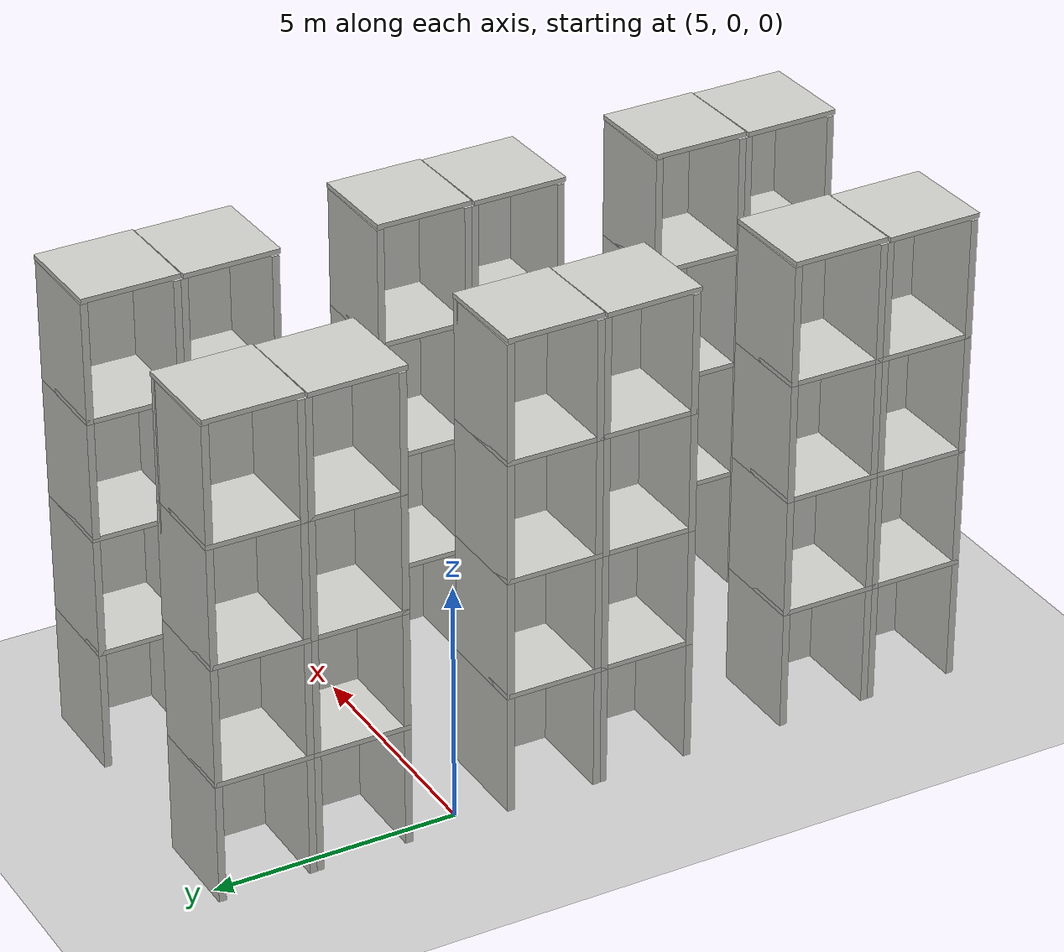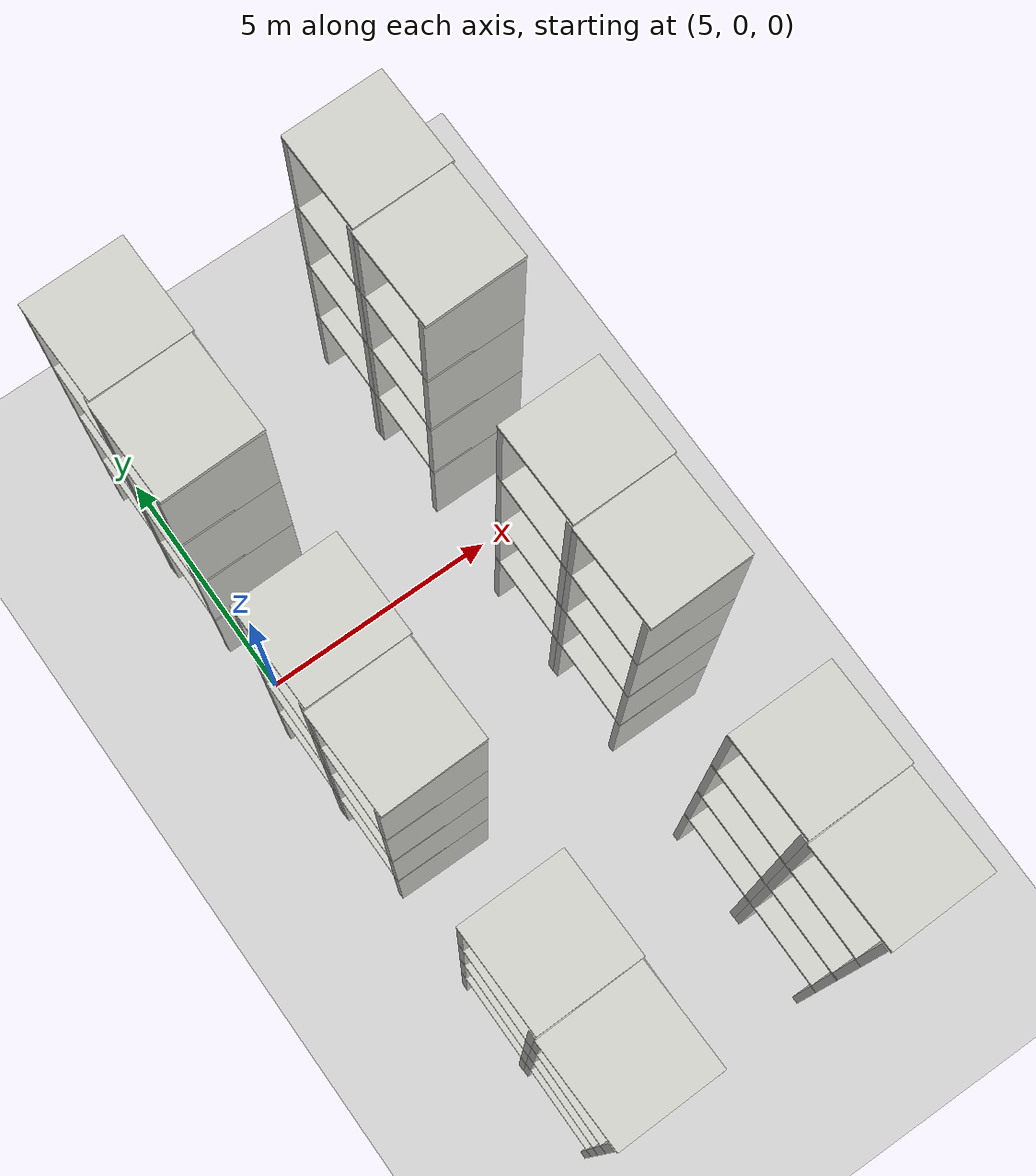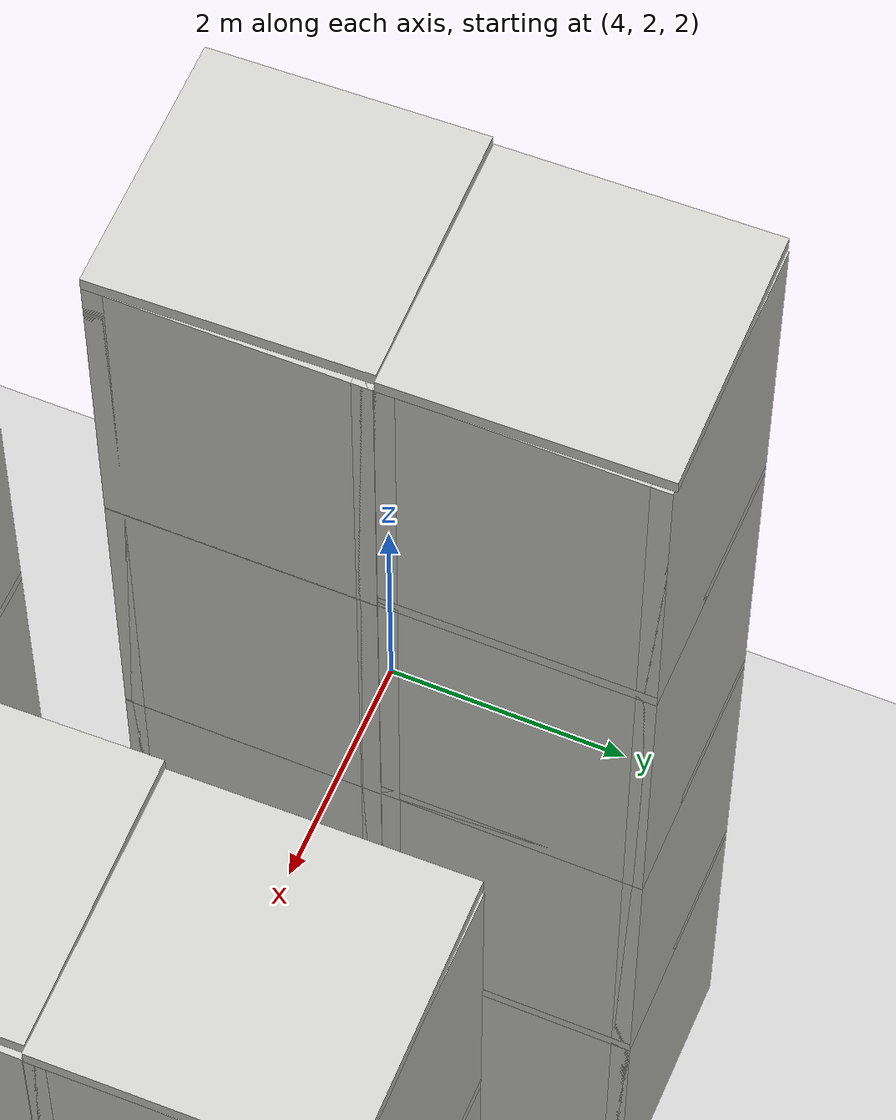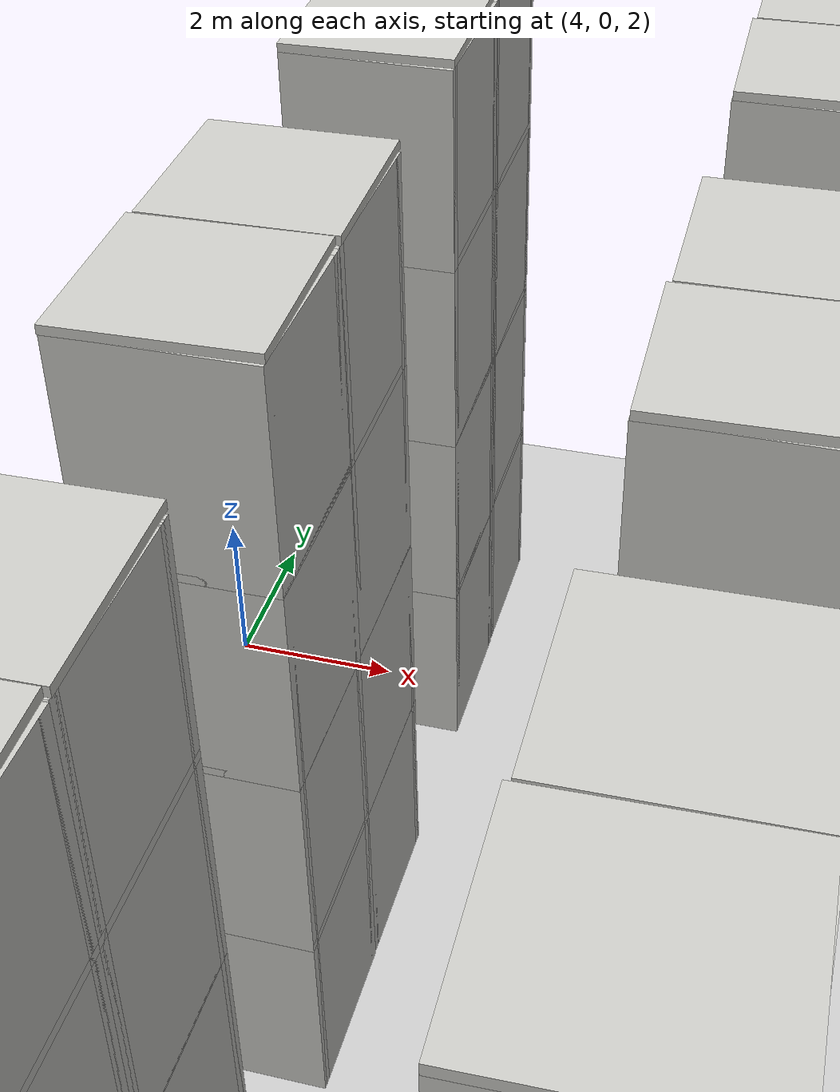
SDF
<sdf version="1.7">
 <world name="default">
  <light name="sun" type="directional">
   <pose>0 0 10 0 -0 0</pose>
   <diffuse>0.8 0.8 0.8 1</diffuse>
   <specular>0.2 0.2 0.2 1</specular>
   <attenuation>
    <range>1000</range>
    <constant>0.9</constant>
    <linear>0.01</linear>
    <quadratic>0.001</quadratic>
   </attenuation>
   <direction>-0.5 0.1 -0.9</direction>
   <spot><inner_angle>0</inner_angle><outer_angle>0</outer_angle><falloff>0</falloff></spot>
  </light>
  <model name="ground_plane">
   <static>1</static>
   <link name="link">
    <collision name="collision">
     <geometry><plane><normal>0 0 1</normal><size>100 100</size></plane></geometry>
     <surface>
      <contact><collide_bitmask>65535</collide_bitmask></contact>
      <friction><ode><mu>100</mu><mu2>50</mu2></ode></friction>
     </surface>
    </collision>
    <visual name="visual">
     <cast_shadows>0</cast_shadows>
     <geometry><plane><normal>0 0 1</normal><size>100 100</size></plane></geometry>
     <material>
      <script><uri>file://media/materials/scripts/gazebo.material</uri><name>Gazebo/Grey</name></script>
     </material>
    </visual>
   </link>
  </model>
  <gravity>0 0 -9.8</gravity>
  <magnetic_field>6e-06 2.3e-05 -4.2e-05</magnetic_field>
  <atmosphere type="adiabatic"/>
  <physics type="ode">
   <max_step_size>0.001</max_step_size>
   <real_time_factor>1</real_time_factor>
   <real_time_update_rate>1000</real_time_update_rate>
  </physics>
  <scene><ambient>0.4 0.4 0.4 1</ambient><background>0.7 0.7 0.7 1</background><shadows>1</shadows></scene>
  <spherical_coordinates>
   <surface_model>EARTH_WGS84</surface_model>
   <latitude_deg>0</latitude_deg>
   <longitude_deg>0</longitude_deg>
   <elevation>0</elevation>
   <heading_deg>0</heading_deg>
  </spherical_coordinates>
  <model name="twin_4th_building">
   <link name="Floor_1">
    <pose>-1.9225 -0.6325 2.5 0 -0 0</pose>
    <visual name="Floor_1_Visual">
     <pose>0 0 0.05 0 -0 0</pose>
     <geometry><box><size>2 2 0.1</size></box></geometry>
     <material>
      <script><uri>file://media/materials/scripts/gazebo.material</uri><name>Gazebo/CeilingTiled</name></script>
      <ambient>1 1 1 1</ambient>
      <shader type="pixel"/>
      <emissive>0 0 0 1</emissive>
     </material>
     <meta><layer>1</layer></meta>
    </visual>
    <collision name="Floor_1_Collision">
     <pose>0 0 0.05 0 -0 0</pose>
     <geometry><box><size>2 2 0.1</size></box></geometry>
     <surface>
      <friction>
       <ode><mu>1</mu><mu2>1</mu2><fdir1>0 0 0</fdir1><slip1>0</slip1><slip2>0</slip2></ode>
       <torsional>
        <coefficient>1</coefficient>
        <patch_radius>0</patch_radius>
        <surface_radius>0</surface_radius>
        <use_patch_radius>1</use_patch_radius>
        <ode><slip>0</slip></ode>
       </torsional>
      </friction>
      <bounce><restitution_coefficient>0</restitution_coefficient><threshold>1e+06</threshold></bounce>
      <contact>
       <collide_without_contact>0</collide_without_contact>
       <collide_without_contact_bitmask>1</collide_without_contact_bitmask>
       <collide_bitmask>1</collide_bitmask>
       <ode>
        <soft_cfm>0</soft_cfm>
        <soft_erp>0.2</soft_erp>
        <kp>1e+13</kp>
        <kd>1</kd>
        <max_vel>0.01</max_vel>
        <min_depth>0</min_depth>
       </ode>
       <bullet>
        <split_impulse>1</split_impulse>
        <split_impulse_penetration_threshold>-0.01</split_impulse_penetration_threshold>
        <soft_cfm>0</soft_cfm>
        <soft_erp>0.2</soft_erp>
        <kp>1e+13</kp>
        <kd>1</kd>
       </bullet>
      </contact>
     </surface>
    </collision>
   </link>
   <link name="Floor_10">
    <pose>-1.9225 -0.6325 7.5 0 -0 0</pose>
    <visual name="Floor_10_Visual">
     <pose>0 0 0.05 0 -0 0</pose>
     <geometry><box><size>2 2 0.1</size></box></geometry>
     <material>
      <script><uri>file://media/materials/scripts/gazebo.material</uri><name>Gazebo/CeilingTiled</name></script>
      <ambient>1 1 1 1</ambient>
      <shader type="pixel"/>
      <emissive>0 0 0 1</emissive>
     </material>
     <meta><layer>3</layer></meta>
    </visual>
    <collision name="Floor_10_Collision">
     <pose>0 0 0.05 0 -0 0</pose>
     <geometry><box><size>2 2 0.1</size></box></geometry>
     <surface>
      <friction>
       <ode><mu>1</mu><mu2>1</mu2><fdir1>0 0 0</fdir1><slip1>0</slip1><slip2>0</slip2></ode>
       <torsional>
        <coefficient>1</coefficient>
        <patch_radius>0</patch_radius>
        <surface_radius>0</surface_radius>
        <use_patch_radius>1</use_patch_radius>
        <ode><slip>0</slip></ode>
       </torsional>
      </friction>
      <bounce><restitution_coefficient>0</restitution_coefficient><threshold>1e+06</threshold></bounce>
      <contact>
       <collide_without_contact>0</collide_without_contact>
       <collide_without_contact_bitmask>1</collide_without_contact_bitmask>
       <collide_bitmask>1</collide_bitmask>
       <ode>
        <soft_cfm>0</soft_cfm>
        <soft_erp>0.2</soft_erp>
        <kp>1e+13</kp>
        <kd>1</kd>
        <max_vel>0.01</max_vel>
        <min_depth>0</min_depth>
       </ode>
       <bullet>
        <split_impulse>1</split_impulse>
        <split_impulse_penetration_threshold>-0.01</split_impulse_penetration_threshold>
        <soft_cfm>0</soft_cfm>
        <soft_erp>0.2</soft_erp>
        <kp>1e+13</kp>
        <kd>1</kd>
       </bullet>
      </contact>
     </surface>
    </collision>
   </link>
   <link name="Floor_10_clone">
    <pose>-1.91647 -0.637292 10.0203 0 0 -1.55375</pose>
    <visual name="Floor_10_Visual">
     <pose>0 0 0.05 0 -0 0</pose>
     <geometry><box><size>2 2 0.1</size></box></geometry>
     <material>
      <script><uri>file://media/materials/scripts/gazebo.material</uri><name>Gazebo/CeilingTiled</name></script>
      <ambient>1 1 1 1</ambient>
      <shader type="pixel"/>
      <emissive>0 0 0 1</emissive>
     </material>
     <meta><layer>3</layer></meta>
    </visual>
    <collision name="Floor_10_Collision">
     <pose>0 0 0.05 0 -0 0</pose>
     <geometry><box><size>2 2 0.1</size></box></geometry>
     <surface>
      <friction>
       <ode><mu>1</mu><mu2>1</mu2><fdir1>0 0 0</fdir1><slip1>0</slip1><slip2>0</slip2></ode>
       <torsional>
        <coefficient>1</coefficient>
        <patch_radius>0</patch_radius>
        <surface_radius>0</surface_radius>
        <use_patch_radius>1</use_patch_radius>
        <ode><slip>0</slip></ode>
       </torsional>
      </friction>
      <bounce><restitution_coefficient>0</restitution_coefficient><threshold>1e+06</threshold></bounce>
      <contact>
       <collide_without_contact>0</collide_without_contact>
       <collide_without_contact_bitmask>1</collide_without_contact_bitmask>
       <collide_bitmask>1</collide_bitmask>
       <ode>
        <soft_cfm>0</soft_cfm>
        <soft_erp>0.2</soft_erp>
        <kp>1e+13</kp>
        <kd>1</kd>
        <max_vel>0.01</max_vel>
        <min_depth>0</min_depth>
       </ode>
       <bullet>
        <split_impulse>1</split_impulse>
        <split_impulse_penetration_threshold>-0.01</split_impulse_penetration_threshold>
        <soft_cfm>0</soft_cfm>
        <soft_erp>0.2</soft_erp>
        <kp>1e+13</kp>
        <kd>1</kd>
       </bullet>
      </contact>
     </surface>
    </collision>
   </link>
   <link name="Floor_10_clone_clone">
    <pose>-3.93376 -0.629613 10.0203 0 0 -3.11619</pose>
    <visual name="Floor_10_Visual">
     <pose>0 0 0.05 0 -0 0</pose>
     <geometry><box><size>2 2 0.1</size></box></geometry>
     <material>
      <script><uri>file://media/materials/scripts/gazebo.material</uri><name>Gazebo/CeilingTiled</name></script>
      <ambient>1 1 1 1</ambient>
      <shader type="pixel"/>
      <emissive>0 0 0 1</emissive>
     </material>
     <meta><layer>3</layer></meta>
    </visual>
    <collision name="Floor_10_Collision">
     <pose>0 0 0.05 0 -0 0</pose>
     <geometry><box><size>2 2 0.1</size></box></geometry>
     <surface>
      <friction>
       <ode><mu>1</mu><mu2>1</mu2><fdir1>0 0 0</fdir1><slip1>0</slip1><slip2>0</slip2></ode>
       <torsional>
        <coefficient>1</coefficient>
        <patch_radius>0</patch_radius>
        <surface_radius>0</surface_radius>
        <use_patch_radius>1</use_patch_radius>
        <ode><slip>0</slip></ode>
       </torsional>
      </friction>
      <bounce><restitution_coefficient>0</restitution_coefficient><threshold>1e+06</threshold></bounce>
      <contact>
       <collide_without_contact>0</collide_without_contact>
       <collide_without_contact_bitmask>1</collide_without_contact_bitmask>
       <collide_bitmask>1</collide_bitmask>
       <ode>
        <soft_cfm>0</soft_cfm>
        <soft_erp>0.2</soft_erp>
        <kp>1e+13</kp>
        <kd>1</kd>
        <max_vel>0.01</max_vel>
        <min_depth>0</min_depth>
       </ode>
       <bullet>
        <split_impulse>1</split_impulse>
        <split_impulse_penetration_threshold>-0.01</split_impulse_penetration_threshold>
        <soft_cfm>0</soft_cfm>
        <soft_erp>0.2</soft_erp>
        <kp>1e+13</kp>
        <kd>1</kd>
       </bullet>
      </contact>
     </surface>
    </collision>
   </link>
   <link name="Floor_9">
    <pose>-1.9225 -0.6325 5 0 -0 0</pose>
    <visual name="Floor_9_Visual">
     <pose>0 0 0.05 0 -0 0</pose>
     <geometry><box><size>2 2 0.1</size></box></geometry>
     <material>
      <script><uri>file://media/materials/scripts/gazebo.material</uri><name>Gazebo/CeilingTiled</name></script>
      <ambient>1 1 1 1</ambient>
      <shader type="pixel"/>
      <emissive>0 0 0 1</emissive>
     </material>
     <meta><layer>2</layer></meta>
    </visual>
    <collision name="Floor_9_Collision">
     <pose>0 0 0.05 0 -0 0</pose>
     <geometry><box><size>2 2 0.1</size></box></geometry>
     <surface>
      <friction>
       <ode><mu>1</mu><mu2>1</mu2><fdir1>0 0 0</fdir1><slip1>0</slip1><slip2>0</slip2></ode>
       <torsional>
        <coefficient>1</coefficient>
        <patch_radius>0</patch_radius>
        <surface_radius>0</surface_radius>
        <use_patch_radius>1</use_patch_radius>
        <ode><slip>0</slip></ode>
       </torsional>
      </friction>
      <bounce><restitution_coefficient>0</restitution_coefficient><threshold>1e+06</threshold></bounce>
      <contact>
       <collide_without_contact>0</collide_without_contact>
       <collide_without_contact_bitmask>1</collide_without_contact_bitmask>
       <collide_bitmask>1</collide_bitmask>
       <ode>
        <soft_cfm>0</soft_cfm>
        <soft_erp>0.2</soft_erp>
        <kp>1e+13</kp>
        <kd>1</kd>
        <max_vel>0.01</max_vel>
        <min_depth>0</min_depth>
       </ode>
       <bullet>
        <split_impulse>1</split_impulse>
        <split_impulse_penetration_threshold>-0.01</split_impulse_penetration_threshold>
        <soft_cfm>0</soft_cfm>
        <soft_erp>0.2</soft_erp>
        <kp>1e+13</kp>
        <kd>1</kd>
       </bullet>
      </contact>
     </surface>
    </collision>
   </link>
   <link name="Wall_13">
    <pose>-2.8475 -0.6325 0 0 0 -1.5708</pose>
    <visual name="Wall_13_Visual">
     <pose>0 0 1.25 0 -0 0</pose>
     <geometry><box><size>2 0.15 2.5</size></box></geometry>
     <material>
      <script><uri>file://media/materials/scripts/gazebo.material</uri><name>Gazebo/CeilingTiled</name></script>
      <ambient>1 1 1 1</ambient>
      <shader type="pixel"/>
      <emissive>0 0 0 1</emissive>
     </material>
     <meta><layer>0</layer></meta>
    </visual>
    <collision name="Wall_13_Collision">
     <pose>0 0 1.25 0 -0 0</pose>
     <geometry><box><size>2 0.15 2.5</size></box></geometry>
     <surface>
      <friction>
       <ode><mu>1</mu><mu2>1</mu2><fdir1>0 0 0</fdir1><slip1>0</slip1><slip2>0</slip2></ode>
       <torsional>
        <coefficient>1</coefficient>
        <patch_radius>0</patch_radius>
        <surface_radius>0</surface_radius>
        <use_patch_radius>1</use_patch_radius>
        <ode><slip>0</slip></ode>
       </torsional>
      </friction>
      <bounce><restitution_coefficient>0</restitution_coefficient><threshold>1e+06</threshold></bounce>
      <contact>
       <collide_without_contact>0</collide_without_contact>
       <collide_without_contact_bitmask>1</collide_without_contact_bitmask>
       <collide_bitmask>1</collide_bitmask>
       <ode>
        <soft_cfm>0</soft_cfm>
        <soft_erp>0.2</soft_erp>
        <kp>1e+13</kp>
        <kd>1</kd>
        <max_vel>0.01</max_vel>
        <min_depth>0</min_depth>
       </ode>
       <bullet>
        <split_impulse>1</split_impulse>
        <split_impulse_penetration_threshold>-0.01</split_impulse_penetration_threshold>
        <soft_cfm>0</soft_cfm>
        <soft_erp>0.2</soft_erp>
        <kp>1e+13</kp>
        <kd>1</kd>
       </bullet>
      </contact>
     </surface>
    </collision>
   </link>
   <link name="Wall_14">
    <pose>-1.9225 -1.5575 0 0 -0 0</pose>
    <visual name="Wall_14_Visual">
     <pose>0 0 1.25 0 -0 0</pose>
     <geometry><box><size>2 0.15 2.5</size></box></geometry>
     <material>
      <script><uri>file://media/materials/scripts/gazebo.material</uri><name>Gazebo/CeilingTiled</name></script>
      <ambient>1 1 1 1</ambient>
      <shader type="pixel"/>
     </material>
     <meta><layer>0</layer></meta>
    </visual>
    <collision name="Wall_14_Collision">
     <pose>0 0 1.25 0 -0 0</pose>
     <geometry><box><size>2 0.15 2.5</size></box></geometry>
     <surface>
      <friction>
       <ode><mu>1</mu><mu2>1</mu2><fdir1>0 0 0</fdir1><slip1>0</slip1><slip2>0</slip2></ode>
       <torsional>
        <coefficient>1</coefficient>
        <patch_radius>0</patch_radius>
        <surface_radius>0</surface_radius>
        <use_patch_radius>1</use_patch_radius>
        <ode><slip>0</slip></ode>
       </torsional>
      </friction>
      <bounce><restitution_coefficient>0</restitution_coefficient><threshold>1e+06</threshold></bounce>
      <contact>
       <collide_without_contact>0</collide_without_contact>
       <collide_without_contact_bitmask>1</collide_without_contact_bitmask>
       <collide_bitmask>1</collide_bitmask>
       <ode>
        <soft_cfm>0</soft_cfm>
        <soft_erp>0.2</soft_erp>
        <kp>1e+13</kp>
        <kd>1</kd>
        <max_vel>0.01</max_vel>
        <min_depth>0</min_depth>
       </ode>
       <bullet>
        <split_impulse>1</split_impulse>
        <split_impulse_penetration_threshold>-0.01</split_impulse_penetration_threshold>
        <soft_cfm>0</soft_cfm>
        <soft_erp>0.2</soft_erp>
        <kp>1e+13</kp>
        <kd>1</kd>
       </bullet>
      </contact>
     </surface>
    </collision>
   </link>
   <link name="Wall_15">
    <pose>-0.9975 -0.6325 0 0 -0 1.5708</pose>
    <visual name="Wall_15_Visual">
     <pose>0 0 1.25 0 -0 0</pose>
     <geometry><box><size>2 0.15 2.5</size></box></geometry>
     <material>
      <script><uri>file://media/materials/scripts/gazebo.material</uri><name>Gazebo/CeilingTiled</name></script>
      <ambient>1 1 1 1</ambient>
      <shader type="pixel"/>
     </material>
     <meta><layer>0</layer></meta>
    </visual>
    <collision name="Wall_15_Collision">
     <pose>0 0 1.25 0 -0 0</pose>
     <geometry><box><size>2 0.15 2.5</size></box></geometry>
     <surface>
      <friction>
       <ode><mu>1</mu><mu2>1</mu2><fdir1>0 0 0</fdir1><slip1>0</slip1><slip2>0</slip2></ode>
       <torsional>
        <coefficient>1</coefficient>
        <patch_radius>0</patch_radius>
        <surface_radius>0</surface_radius>
        <use_patch_radius>1</use_patch_radius>
        <ode><slip>0</slip></ode>
       </torsional>
      </friction>
      <bounce><restitution_coefficient>0</restitution_coefficient><threshold>1e+06</threshold></bounce>
      <contact>
       <collide_without_contact>0</collide_without_contact>
       <collide_without_contact_bitmask>1</collide_without_contact_bitmask>
       <collide_bitmask>1</collide_bitmask>
       <ode>
        <soft_cfm>0</soft_cfm>
        <soft_erp>0.2</soft_erp>
        <kp>1e+13</kp>
        <kd>1</kd>
        <max_vel>0.01</max_vel>
        <min_depth>0</min_depth>
       </ode>
       <bullet>
        <split_impulse>1</split_impulse>
        <split_impulse_penetration_threshold>-0.01</split_impulse_penetration_threshold>
        <soft_cfm>0</soft_cfm>
        <soft_erp>0.2</soft_erp>
        <kp>1e+13</kp>
        <kd>1</kd>
       </bullet>
      </contact>
     </surface>
    </collision>
   </link>
   <link name="Wall_17">
    <pose>-2.8475 -0.6325 2.5 0 0 -1.5708</pose>
    <visual name="Wall_17_Visual">
     <pose>0 0 1.25 0 -0 0</pose>
     <geometry><box><size>2 0.15 2.5</size></box></geometry>
     <material>
      <script><uri>file://media/materials/scripts/gazebo.material</uri><name>Gazebo/CeilingTiled</name></script>
      <ambient>1 1 1 1</ambient>
      <shader type="pixel"/>
      <emissive>0 0 0 1</emissive>
     </material>
     <meta><layer>1</layer></meta>
    </visual>
    <collision name="Wall_17_Collision">
     <pose>0 0 1.25 0 -0 0</pose>
     <geometry><box><size>2 0.15 2.5</size></box></geometry>
     <surface>
      <friction>
       <ode><mu>1</mu><mu2>1</mu2><fdir1>0 0 0</fdir1><slip1>0</slip1><slip2>0</slip2></ode>
       <torsional>
        <coefficient>1</coefficient>
        <patch_radius>0</patch_radius>
        <surface_radius>0</surface_radius>
        <use_patch_radius>1</use_patch_radius>
        <ode><slip>0</slip></ode>
       </torsional>
      </friction>
      <bounce><restitution_coefficient>0</restitution_coefficient><threshold>1e+06</threshold></bounce>
      <contact>
       <collide_without_contact>0</collide_without_contact>
       <collide_without_contact_bitmask>1</collide_without_contact_bitmask>
       <collide_bitmask>1</collide_bitmask>
       <ode>
        <soft_cfm>0</soft_cfm>
        <soft_erp>0.2</soft_erp>
        <kp>1e+13</kp>
        <kd>1</kd>
        <max_vel>0.01</max_vel>
        <min_depth>0</min_depth>
       </ode>
       <bullet>
        <split_impulse>1</split_impulse>
        <split_impulse_penetration_threshold>-0.01</split_impulse_penetration_threshold>
        <soft_cfm>0</soft_cfm>
        <soft_erp>0.2</soft_erp>
        <kp>1e+13</kp>
        <kd>1</kd>
       </bullet>
      </contact>
     </surface>
    </collision>
   </link>
   <link name="Wall_18">
    <pose>-1.9225 -1.5575 2.5 0 -0 0</pose>
    <visual name="Wall_18_Visual">
     <pose>0 0 1.25 0 -0 0</pose>
     <geometry><box><size>2 0.15 2.5</size></box></geometry>
     <material>
      <script><uri>file://media/materials/scripts/gazebo.material</uri><name>Gazebo/CeilingTiled</name></script>
      <ambient>1 1 1 1</ambient>
      <shader type="pixel"/>
      <emissive>0 0 0 1</emissive>
     </material>
     <meta><layer>1</layer></meta>
    </visual>
    <collision name="Wall_18_Collision">
     <pose>0 0 1.25 0 -0 0</pose>
     <geometry><box><size>2 0.15 2.5</size></box></geometry>
     <surface>
      <friction>
       <ode><mu>1</mu><mu2>1</mu2><fdir1>0 0 0</fdir1><slip1>0</slip1><slip2>0</slip2></ode>
       <torsional>
        <coefficient>1</coefficient>
        <patch_radius>0</patch_radius>
        <surface_radius>0</surface_radius>
        <use_patch_radius>1</use_patch_radius>
        <ode><slip>0</slip></ode>
       </torsional>
      </friction>
      <bounce><restitution_coefficient>0</restitution_coefficient><threshold>1e+06</threshold></bounce>
      <contact>
       <collide_without_contact>0</collide_without_contact>
       <collide_without_contact_bitmask>1</collide_without_contact_bitmask>
       <collide_bitmask>1</collide_bitmask>
       <ode>
        <soft_cfm>0</soft_cfm>
        <soft_erp>0.2</soft_erp>
        <kp>1e+13</kp>
        <kd>1</kd>
        <max_vel>0.01</max_vel>
        <min_depth>0</min_depth>
       </ode>
       <bullet>
        <split_impulse>1</split_impulse>
        <split_impulse_penetration_threshold>-0.01</split_impulse_penetration_threshold>
        <soft_cfm>0</soft_cfm>
        <soft_erp>0.2</soft_erp>
        <kp>1e+13</kp>
        <kd>1</kd>
       </bullet>
      </contact>
     </surface>
    </collision>
   </link>
   <link name="Wall_19">
    <pose>-0.9975 -0.6325 2.5 0 -0 1.5708</pose>
    <visual name="Wall_19_Visual">
     <pose>0 0 1.25 0 -0 0</pose>
     <geometry><box><size>2 0.15 2.5</size></box></geometry>
     <material>
      <script><uri>file://media/materials/scripts/gazebo.material</uri><name>Gazebo/CeilingTiled</name></script>
      <ambient>1 1 1 1</ambient>
      <shader type="pixel"/>
     </material>
     <meta><layer>1</layer></meta>
    </visual>
    <collision name="Wall_19_Collision">
     <pose>0 0 1.25 0 -0 0</pose>
     <geometry><box><size>2 0.15 2.5</size></box></geometry>
     <surface>
      <friction>
       <ode><mu>1</mu><mu2>1</mu2><fdir1>0 0 0</fdir1><slip1>0</slip1><slip2>0</slip2></ode>
       <torsional>
        <coefficient>1</coefficient>
        <patch_radius>0</patch_radius>
        <surface_radius>0</surface_radius>
        <use_patch_radius>1</use_patch_radius>
        <ode><slip>0</slip></ode>
       </torsional>
      </friction>
      <bounce><restitution_coefficient>0</restitution_coefficient><threshold>1e+06</threshold></bounce>
      <contact>
       <collide_without_contact>0</collide_without_contact>
       <collide_without_contact_bitmask>1</collide_without_contact_bitmask>
       <collide_bitmask>1</collide_bitmask>
       <ode>
        <soft_cfm>0</soft_cfm>
        <soft_erp>0.2</soft_erp>
        <kp>1e+13</kp>
        <kd>1</kd>
        <max_vel>0.01</max_vel>
        <min_depth>0</min_depth>
       </ode>
       <bullet>
        <split_impulse>1</split_impulse>
        <split_impulse_penetration_threshold>-0.01</split_impulse_penetration_threshold>
        <soft_cfm>0</soft_cfm>
        <soft_erp>0.2</soft_erp>
        <kp>1e+13</kp>
        <kd>1</kd>
       </bullet>
      </contact>
     </surface>
    </collision>
   </link>
   <link name="Wall_40">
    <pose>-2.8475 -0.6325 5 0 0 -1.5708</pose>
    <visual name="Wall_40_Visual">
     <pose>0 0 1.25 0 -0 0</pose>
     <geometry><box><size>2 0.15 2.5</size></box></geometry>
     <material>
      <script><uri>file://media/materials/scripts/gazebo.material</uri><name>Gazebo/CeilingTiled</name></script>
      <ambient>1 1 1 1</ambient>
      <shader type="pixel"/>
      <emissive>0 0 0 1</emissive>
     </material>
     <meta><layer>2</layer></meta>
    </visual>
    <collision name="Wall_40_Collision">
     <pose>0 0 1.25 0 -0 0</pose>
     <geometry><box><size>2 0.15 2.5</size></box></geometry>
     <surface>
      <friction>
       <ode><mu>1</mu><mu2>1</mu2><fdir1>0 0 0</fdir1><slip1>0</slip1><slip2>0</slip2></ode>
       <torsional>
        <coefficient>1</coefficient>
        <patch_radius>0</patch_radius>
        <surface_radius>0</surface_radius>
        <use_patch_radius>1</use_patch_radius>
        <ode><slip>0</slip></ode>
       </torsional>
      </friction>
      <bounce><restitution_coefficient>0</restitution_coefficient><threshold>1e+06</threshold></bounce>
      <contact>
       <collide_without_contact>0</collide_without_contact>
       <collide_without_contact_bitmask>1</collide_without_contact_bitmask>
       <collide_bitmask>1</collide_bitmask>
       <ode>
        <soft_cfm>0</soft_cfm>
        <soft_erp>0.2</soft_erp>
        <kp>1e+13</kp>
        <kd>1</kd>
        <max_vel>0.01</max_vel>
        <min_depth>0</min_depth>
       </ode>
       <bullet>
        <split_impulse>1</split_impulse>
        <split_impulse_penetration_threshold>-0.01</split_impulse_penetration_threshold>
        <soft_cfm>0</soft_cfm>
        <soft_erp>0.2</soft_erp>
        <kp>1e+13</kp>
        <kd>1</kd>
       </bullet>
      </contact>
     </surface>
    </collision>
   </link>
   <link name="Wall_41">
    <pose>-1.9225 -1.5575 5 0 -0 0</pose>
    <visual name="Wall_41_Visual">
     <pose>0 0 1.25 0 -0 0</pose>
     <geometry><box><size>2 0.15 2.5</size></box></geometry>
     <material>
      <script><uri>file://media/materials/scripts/gazebo.material</uri><name>Gazebo/CeilingTiled</name></script>
      <ambient>1 1 1 1</ambient>
      <shader type="pixel"/>
      <emissive>0 0 0 1</emissive>
     </material>
     <meta><layer>2</layer></meta>
    </visual>
    <collision name="Wall_41_Collision">
     <pose>0 0 1.25 0 -0 0</pose>
     <geometry><box><size>2 0.15 2.5</size></box></geometry>
     <surface>
      <friction>
       <ode><mu>1</mu><mu2>1</mu2><fdir1>0 0 0</fdir1><slip1>0</slip1><slip2>0</slip2></ode>
       <torsional>
        <coefficient>1</coefficient>
        <patch_radius>0</patch_radius>
        <surface_radius>0</surface_radius>
        <use_patch_radius>1</use_patch_radius>
        <ode><slip>0</slip></ode>
       </torsional>
      </friction>
      <bounce><restitution_coefficient>0</restitution_coefficient><threshold>1e+06</threshold></bounce>
      <contact>
       <collide_without_contact>0</collide_without_contact>
       <collide_without_contact_bitmask>1</collide_without_contact_bitmask>
       <collide_bitmask>1</collide_bitmask>
       <ode>
        <soft_cfm>0</soft_cfm>
        <soft_erp>0.2</soft_erp>
        <kp>1e+13</kp>
        <kd>1</kd>
        <max_vel>0.01</max_vel>
        <min_depth>0</min_depth>
       </ode>
       <bullet>
        <split_impulse>1</split_impulse>
        <split_impulse_penetration_threshold>-0.01</split_impulse_penetration_threshold>
        <soft_cfm>0</soft_cfm>
        <soft_erp>0.2</soft_erp>
        <kp>1e+13</kp>
        <kd>1</kd>
       </bullet>
      </contact>
     </surface>
    </collision>
   </link>
   <link name="Wall_42">
    <pose>-0.9975 -0.6325 5 0 -0 1.5708</pose>
    <visual name="Wall_42_Visual">
     <pose>0 0 1.25 0 -0 0</pose>
     <geometry><box><size>2 0.15 2.5</size></box></geometry>
     <material>
      <script><uri>file://media/materials/scripts/gazebo.material</uri><name>Gazebo/CeilingTiled</name></script>
      <ambient>1 1 1 1</ambient>
      <shader type="pixel"/>
     </material>
     <meta><layer>2</layer></meta>
    </visual>
    <collision name="Wall_42_Collision">
     <pose>0 0 1.25 0 -0 0</pose>
     <geometry><box><size>2 0.15 2.5</size></box></geometry>
     <surface>
      <friction>
       <ode><mu>1</mu><mu2>1</mu2><fdir1>0 0 0</fdir1><slip1>0</slip1><slip2>0</slip2></ode>
       <torsional>
        <coefficient>1</coefficient>
        <patch_radius>0</patch_radius>
        <surface_radius>0</surface_radius>
        <use_patch_radius>1</use_patch_radius>
        <ode><slip>0</slip></ode>
       </torsional>
      </friction>
      <bounce><restitution_coefficient>0</restitution_coefficient><threshold>1e+06</threshold></bounce>
      <contact>
       <collide_without_contact>0</collide_without_contact>
       <collide_without_contact_bitmask>1</collide_without_contact_bitmask>
       <collide_bitmask>1</collide_bitmask>
       <ode>
        <soft_cfm>0</soft_cfm>
        <soft_erp>0.2</soft_erp>
        <kp>1e+13</kp>
        <kd>1</kd>
        <max_vel>0.01</max_vel>
        <min_depth>0</min_depth>
       </ode>
       <bullet>
        <split_impulse>1</split_impulse>
        <split_impulse_penetration_threshold>-0.01</split_impulse_penetration_threshold>
        <soft_cfm>0</soft_cfm>
        <soft_erp>0.2</soft_erp>
        <kp>1e+13</kp>
        <kd>1</kd>
       </bullet>
      </contact>
     </surface>
    </collision>
   </link>
   <link name="Wall_43">
    <pose>-2.8475 -0.6325 7.5 0 0 -1.5708</pose>
    <visual name="Wall_43_Visual">
     <pose>0 0 1.25 0 -0 0</pose>
     <geometry><box><size>2 0.15 2.5</size></box></geometry>
     <material>
      <script><uri>file://media/materials/scripts/gazebo.material</uri><name>Gazebo/CeilingTiled</name></script>
      <ambient>1 1 1 1</ambient>
      <shader type="pixel"/>
      <emissive>0 0 0 1</emissive>
     </material>
     <meta><layer>3</layer></meta>
    </visual>
    <collision name="Wall_43_Collision">
     <pose>0 0 1.25 0 -0 0</pose>
     <geometry><box><size>2 0.15 2.5</size></box></geometry>
     <surface>
      <friction>
       <ode><mu>1</mu><mu2>1</mu2><fdir1>0 0 0</fdir1><slip1>0</slip1><slip2>0</slip2></ode>
       <torsional>
        <coefficient>1</coefficient>
        <patch_radius>0</patch_radius>
        <surface_radius>0</surface_radius>
        <use_patch_radius>1</use_patch_radius>
        <ode><slip>0</slip></ode>
       </torsional>
      </friction>
      <bounce><restitution_coefficient>0</restitution_coefficient><threshold>1e+06</threshold></bounce>
      <contact>
       <collide_without_contact>0</collide_without_contact>
       <collide_without_contact_bitmask>1</collide_without_contact_bitmask>
       <collide_bitmask>1</collide_bitmask>
       <ode>
        <soft_cfm>0</soft_cfm>
        <soft_erp>0.2</soft_erp>
        <kp>1e+13</kp>
        <kd>1</kd>
        <max_vel>0.01</max_vel>
        <min_depth>0</min_depth>
       </ode>
       <bullet>
        <split_impulse>1</split_impulse>
        <split_impulse_penetration_threshold>-0.01</split_impulse_penetration_threshold>
        <soft_cfm>0</soft_cfm>
        <soft_erp>0.2</soft_erp>
        <kp>1e+13</kp>
        <kd>1</kd>
       </bullet>
      </contact>
     </surface>
    </collision>
   </link>
   <link name="Wall_44">
    <pose>-1.9225 -1.5575 7.5 0 -0 0</pose>
    <visual name="Wall_44_Visual">
     <pose>0 0 1.25 0 -0 0</pose>
     <geometry><box><size>2 0.15 2.5</size></box></geometry>
     <material>
      <script><uri>file://media/materials/scripts/gazebo.material</uri><name>Gazebo/CeilingTiled</name></script>
      <ambient>1 1 1 1</ambient>
      <shader type="pixel"/>
      <emissive>0 0 0 1</emissive>
     </material>
     <meta><layer>3</layer></meta>
    </visual>
    <collision name="Wall_44_Collision">
     <pose>0 0 1.25 0 -0 0</pose>
     <geometry><box><size>2 0.15 2.5</size></box></geometry>
     <surface>
      <friction>
       <ode><mu>1</mu><mu2>1</mu2><fdir1>0 0 0</fdir1><slip1>0</slip1><slip2>0</slip2></ode>
       <torsional>
        <coefficient>1</coefficient>
        <patch_radius>0</patch_radius>
        <surface_radius>0</surface_radius>
        <use_patch_radius>1</use_patch_radius>
        <ode><slip>0</slip></ode>
       </torsional>
      </friction>
      <bounce><restitution_coefficient>0</restitution_coefficient><threshold>1e+06</threshold></bounce>
      <contact>
       <collide_without_contact>0</collide_without_contact>
       <collide_without_contact_bitmask>1</collide_without_contact_bitmask>
       <collide_bitmask>1</collide_bitmask>
       <ode>
        <soft_cfm>0</soft_cfm>
        <soft_erp>0.2</soft_erp>
        <kp>1e+13</kp>
        <kd>1</kd>
        <max_vel>0.01</max_vel>
        <min_depth>0</min_depth>
       </ode>
       <bullet>
        <split_impulse>1</split_impulse>
        <split_impulse_penetration_threshold>-0.01</split_impulse_penetration_threshold>
        <soft_cfm>0</soft_cfm>
        <soft_erp>0.2</soft_erp>
        <kp>1e+13</kp>
        <kd>1</kd>
       </bullet>
      </contact>
     </surface>
    </collision>
   </link>
   <link name="Wall_45">
    <pose>-0.9975 -0.6325 7.5 0 -0 1.5708</pose>
    <visual name="Wall_45_Visual">
     <pose>0 0 1.25 0 -0 0</pose>
     <geometry><box><size>2 0.15 2.5</size></box></geometry>
     <material>
      <script><uri>file://media/materials/scripts/gazebo.material</uri><name>Gazebo/CeilingTiled</name></script>
      <ambient>1 1 1 1</ambient>
      <shader type="pixel"/>
     </material>
     <meta><layer>3</layer></meta>
    </visual>
    <collision name="Wall_45_Collision">
     <pose>0 0 1.25 0 -0 0</pose>
     <geometry><box><size>2 0.15 2.5</size></box></geometry>
     <surface>
      <friction>
       <ode><mu>1</mu><mu2>1</mu2><fdir1>0 0 0</fdir1><slip1>0</slip1><slip2>0</slip2></ode>
       <torsional>
        <coefficient>1</coefficient>
        <patch_radius>0</patch_radius>
        <surface_radius>0</surface_radius>
        <use_patch_radius>1</use_patch_radius>
        <ode><slip>0</slip></ode>
       </torsional>
      </friction>
      <bounce><restitution_coefficient>0</restitution_coefficient><threshold>1e+06</threshold></bounce>
      <contact>
       <collide_without_contact>0</collide_without_contact>
       <collide_without_contact_bitmask>1</collide_without_contact_bitmask>
       <collide_bitmask>1</collide_bitmask>
       <ode>
        <soft_cfm>0</soft_cfm>
        <soft_erp>0.2</soft_erp>
        <kp>1e+13</kp>
        <kd>1</kd>
        <max_vel>0.01</max_vel>
        <min_depth>0</min_depth>
       </ode>
       <bullet>
        <split_impulse>1</split_impulse>
        <split_impulse_penetration_threshold>-0.01</split_impulse_penetration_threshold>
        <soft_cfm>0</soft_cfm>
        <soft_erp>0.2</soft_erp>
        <kp>1e+13</kp>
        <kd>1</kd>
       </bullet>
      </contact>
     </surface>
    </collision>
   </link>
   <model name="4th_building">
    <pose>-1.99386 -0.00682 0 0 -0 0</pose>
    <link name="Floor_1">
     <collision name="Floor_1_Collision">
      <geometry><box><size>2 2 0.1</size></box></geometry>
      <pose>0 0 0.05 0 -0 0</pose>
     </collision>
     <visual name="Floor_1_Visual">
      <pose>0 0 0.05 0 -0 0</pose>
      <geometry><box><size>2 2 0.1</size></box></geometry>
      <material>
       <script><uri>file://media/materials/scripts/gazebo.material</uri><name>Gazebo/CeilingTiled</name></script>
       <ambient>1 1 1 1</ambient>
      </material>
      <meta><layer>1</layer></meta>
     </visual>
     <pose>-1.9225 -0.6325 2.5 0 -0 0</pose>
    </link>
    <link name="Floor_10">
     <collision name="Floor_10_Collision">
      <geometry><box><size>2 2 0.1</size></box></geometry>
      <pose>0 0 0.05 0 -0 0</pose>
     </collision>
     <visual name="Floor_10_Visual">
      <pose>0 0 0.05 0 -0 0</pose>
      <geometry><box><size>2 2 0.1</size></box></geometry>
      <material>
       <script><uri>file://media/materials/scripts/gazebo.material</uri><name>Gazebo/CeilingTiled</name></script>
       <ambient>1 1 1 1</ambient>
      </material>
      <meta><layer>3</layer></meta>
     </visual>
     <pose>-1.9225 -0.6325 7.5 0 -0 0</pose>
    </link>
    <link name="Floor_9">
     <collision name="Floor_9_Collision">
      <geometry><box><size>2 2 0.1</size></box></geometry>
      <pose>0 0 0.05 0 -0 0</pose>
     </collision>
     <visual name="Floor_9_Visual">
      <pose>0 0 0.05 0 -0 0</pose>
      <geometry><box><size>2 2 0.1</size></box></geometry>
      <material>
       <script><uri>file://media/materials/scripts/gazebo.material</uri><name>Gazebo/CeilingTiled</name></script>
       <ambient>1 1 1 1</ambient>
      </material>
      <meta><layer>2</layer></meta>
     </visual>
     <pose>-1.9225 -0.6325 5 0 -0 0</pose>
    </link>
    <link name="Wall_13">
     <collision name="Wall_13_Collision">
      <geometry><box><size>2 0.15 2.5</size></box></geometry>
      <pose>0 0 1.25 0 -0 0</pose>
     </collision>
     <visual name="Wall_13_Visual">
      <pose>0 0 1.25 0 -0 0</pose>
      <geometry><box><size>2 0.15 2.5</size></box></geometry>
      <material>
       <script><uri>file://media/materials/scripts/gazebo.material</uri><name>Gazebo/CeilingTiled</name></script>
       <ambient>1 1 1 1</ambient>
      </material>
      <meta><layer>0</layer></meta>
     </visual>
     <pose>-2.8475 -0.6325 0 0 -0 -1.5708</pose>
    </link>
    <link name="Wall_14">
     <collision name="Wall_14_Collision">
      <geometry><box><size>2 0.15 2.5</size></box></geometry>
      <pose>0 0 1.25 0 -0 0</pose>
     </collision>
     <visual name="Wall_14_Visual">
      <pose>0 0 1.25 0 -0 0</pose>
      <geometry><box><size>2 0.15 2.5</size></box></geometry>
      <material>
       <script><uri>file://media/materials/scripts/gazebo.material</uri><name>Gazebo/CeilingTiled</name></script>
       <ambient>1 1 1 1</ambient>
      </material>
      <meta><layer>0</layer></meta>
     </visual>
     <pose>-1.9225 -1.5575 0 0 -0 0</pose>
    </link>
    <link name="Wall_15">
     <collision name="Wall_15_Collision">
      <geometry><box><size>2 0.15 2.5</size></box></geometry>
      <pose>0 0 1.25 0 -0 0</pose>
     </collision>
     <visual name="Wall_15_Visual">
      <pose>0 0 1.25 0 -0 0</pose>
      <geometry><box><size>2 0.15 2.5</size></box></geometry>
      <material>
       <script><uri>file://media/materials/scripts/gazebo.material</uri><name>Gazebo/CeilingTiled</name></script>
       <ambient>1 1 1 1</ambient>
      </material>
      <meta><layer>0</layer></meta>
     </visual>
     <pose>-0.9975 -0.6325 0 0 -0 1.5708</pose>
    </link>
    <link name="Wall_17">
     <collision name="Wall_17_Collision">
      <geometry><box><size>2 0.15 2.5</size></box></geometry>
      <pose>0 0 1.25 0 -0 0</pose>
     </collision>
     <visual name="Wall_17_Visual">
      <pose>0 0 1.25 0 -0 0</pose>
      <geometry><box><size>2 0.15 2.5</size></box></geometry>
      <material>
       <script><uri>file://media/materials/scripts/gazebo.material</uri><name>Gazebo/CeilingTiled</name></script>
       <ambient>1 1 1 1</ambient>
      </material>
      <meta><layer>1</layer></meta>
     </visual>
     <pose>-2.8475 -0.6325 2.5 0 -0 -1.5708</pose>
    </link>
    <link name="Wall_18">
     <collision name="Wall_18_Collision">
      <geometry><box><size>2 0.15 2.5</size></box></geometry>
      <pose>0 0 1.25 0 -0 0</pose>
     </collision>
     <visual name="Wall_18_Visual">
      <pose>0 0 1.25 0 -0 0</pose>
      <geometry><box><size>2 0.15 2.5</size></box></geometry>
      <material>
       <script><uri>file://media/materials/scripts/gazebo.material</uri><name>Gazebo/CeilingTiled</name></script>
       <ambient>1 1 1 1</ambient>
      </material>
      <meta><layer>1</layer></meta>
     </visual>
     <pose>-1.9225 -1.5575 2.5 0 -0 0</pose>
    </link>
    <link name="Wall_19">
     <collision name="Wall_19_Collision">
      <geometry><box><size>2 0.15 2.5</size></box></geometry>
      <pose>0 0 1.25 0 -0 0</pose>
     </collision>
     <visual name="Wall_19_Visual">
      <pose>0 0 1.25 0 -0 0</pose>
      <geometry><box><size>2 0.15 2.5</size></box></geometry>
      <material>
       <script><uri>file://media/materials/scripts/gazebo.material</uri><name>Gazebo/CeilingTiled</name></script>
       <ambient>1 1 1 1</ambient>
      </material>
      <meta><layer>1</layer></meta>
     </visual>
     <pose>-0.9975 -0.6325 2.5 0 -0 1.5708</pose>
    </link>
    <link name="Wall_40">
     <collision name="Wall_40_Collision">
      <geometry><box><size>2 0.15 2.5</size></box></geometry>
      <pose>0 0 1.25 0 -0 0</pose>
     </collision>
     <visual name="Wall_40_Visual">
      <pose>0 0 1.25 0 -0 0</pose>
      <geometry><box><size>2 0.15 2.5</size></box></geometry>
      <material>
       <script><uri>file://media/materials/scripts/gazebo.material</uri><name>Gazebo/CeilingTiled</name></script>
       <ambient>1 1 1 1</ambient>
      </material>
      <meta><layer>2</layer></meta>
     </visual>
     <pose>-2.8475 -0.6325 5 0 -0 -1.5708</pose>
    </link>
    <link name="Wall_41">
     <collision name="Wall_41_Collision">
      <geometry><box><size>2 0.15 2.5</size></box></geometry>
      <pose>0 0 1.25 0 -0 0</pose>
     </collision>
     <visual name="Wall_41_Visual">
      <pose>0 0 1.25 0 -0 0</pose>
      <geometry><box><size>2 0.15 2.5</size></box></geometry>
      <material>
       <script><uri>file://media/materials/scripts/gazebo.material</uri><name>Gazebo/CeilingTiled</name></script>
       <ambient>1 1 1 1</ambient>
      </material>
      <meta><layer>2</layer></meta>
     </visual>
     <pose>-1.9225 -1.5575 5 0 -0 0</pose>
    </link>
    <link name="Wall_42">
     <collision name="Wall_42_Collision">
      <geometry><box><size>2 0.15 2.5</size></box></geometry>
      <pose>0 0 1.25 0 -0 0</pose>
     </collision>
     <visual name="Wall_42_Visual">
      <pose>0 0 1.25 0 -0 0</pose>
      <geometry><box><size>2 0.15 2.5</size></box></geometry>
      <material>
       <script><uri>file://media/materials/scripts/gazebo.material</uri><name>Gazebo/CeilingTiled</name></script>
       <ambient>1 1 1 1</ambient>
      </material>
      <meta><layer>2</layer></meta>
     </visual>
     <pose>-0.9975 -0.6325 5 0 -0 1.5708</pose>
    </link>
    <link name="Wall_43">
     <collision name="Wall_43_Collision">
      <geometry><box><size>2 0.15 2.5</size></box></geometry>
      <pose>0 0 1.25 0 -0 0</pose>
     </collision>
     <visual name="Wall_43_Visual">
      <pose>0 0 1.25 0 -0 0</pose>
      <geometry><box><size>2 0.15 2.5</size></box></geometry>
      <material>
       <script><uri>file://media/materials/scripts/gazebo.material</uri><name>Gazebo/CeilingTiled</name></script>
       <ambient>1 1 1 1</ambient>
      </material>
      <meta><layer>3</layer></meta>
     </visual>
     <pose>-2.8475 -0.6325 7.5 0 -0 -1.5708</pose>
    </link>
    <link name="Wall_44">
     <collision name="Wall_44_Collision">
      <geometry><box><size>2 0.15 2.5</size></box></geometry>
      <pose>0 0 1.25 0 -0 0</pose>
     </collision>
     <visual name="Wall_44_Visual">
      <pose>0 0 1.25 0 -0 0</pose>
      <geometry><box><size>2 0.15 2.5</size></box></geometry>
      <material>
       <script><uri>file://media/materials/scripts/gazebo.material</uri><name>Gazebo/CeilingTiled</name></script>
       <ambient>1 1 1 1</ambient>
      </material>
      <meta><layer>3</layer></meta>
     </visual>
     <pose>-1.9225 -1.5575 7.5 0 -0 0</pose>
    </link>
    <link name="Wall_45">
     <collision name="Wall_45_Collision">
      <geometry><box><size>2 0.15 2.5</size></box></geometry>
      <pose>0 0 1.25 0 -0 0</pose>
     </collision>
     <visual name="Wall_45_Visual">
      <pose>0 0 1.25 0 -0 0</pose>
      <geometry><box><size>2 0.15 2.5</size></box></geometry>
      <material>
       <script><uri>file://media/materials/scripts/gazebo.material</uri><name>Gazebo/CeilingTiled</name></script>
       <ambient>1 1 1 1</ambient>
      </material>
      <meta><layer>3</layer></meta>
     </visual>
     <pose>-0.9975 -0.6325 7.5 0 -0 1.5708</pose>
    </link>
    <static>1</static>
   </model>
   <joint name="Wall_13_JOINT_4" type="revolute">
    <parent>Wall_13</parent>
    <child>4th_building::Wall_15</child>
    <axis>
     <xyz>1 0 0</xyz>
     <limit>
      <lower>-1.79769e+308</lower>
      <upper>1.79769e+308</upper>
      <effort>-1</effort>
      <velocity>-1</velocity>
     </limit>
     <dynamics>
      <spring_reference>0</spring_reference>
      <spring_stiffness>0</spring_stiffness>
      <damping>0</damping>
      <friction>0</friction>
     </dynamics>
    </axis>
    <physics>
     <ode><limit><cfm>0</cfm><erp>0.2</erp></limit><suspension><cfm>0</cfm><erp>0.2</erp></suspension></ode>
    </physics>
   </joint>
   <joint name="Wall_17_JOINT_3" type="revolute">
    <parent>Wall_17</parent>
    <child>4th_building::Wall_19</child>
    <axis>
     <xyz>1 0 0</xyz>
     <limit>
      <lower>-1.79769e+308</lower>
      <upper>1.79769e+308</upper>
      <effort>-1</effort>
      <velocity>-1</velocity>
     </limit>
     <dynamics>
      <spring_reference>0</spring_reference>
      <spring_stiffness>0</spring_stiffness>
      <damping>0</damping>
      <friction>0</friction>
     </dynamics>
    </axis>
    <physics>
     <ode><limit><cfm>0</cfm><erp>0.2</erp></limit><suspension><cfm>0</cfm><erp>0.2</erp></suspension></ode>
    </physics>
   </joint>
   <joint name="Wall_40_JOINT_2" type="revolute">
    <parent>Wall_40</parent>
    <child>4th_building::Wall_42</child>
    <axis>
     <xyz>1 0 0</xyz>
     <limit>
      <lower>-1.79769e+308</lower>
      <upper>1.79769e+308</upper>
      <effort>-1</effort>
      <velocity>-1</velocity>
     </limit>
     <dynamics>
      <spring_reference>0</spring_reference>
      <spring_stiffness>0</spring_stiffness>
      <damping>0</damping>
      <friction>0</friction>
     </dynamics>
    </axis>
    <physics>
     <ode><limit><cfm>0</cfm><erp>0.2</erp></limit><suspension><cfm>0</cfm><erp>0.2</erp></suspension></ode>
    </physics>
   </joint>
   <joint name="Wall_43_JOINT_1" type="fixed">
    <parent>Wall_43</parent>
    <child>4th_building::Wall_45</child>
    <physics>
     <ode><limit><cfm>0</cfm><erp>0.2</erp></limit><suspension><cfm>0</cfm><erp>0.2</erp></suspension></ode>
    </physics>
   </joint>
   <static>1</static>
   <pose>5 0 0 0 -0 1.57</pose>
  </model>
  <model name="twin_4th_building_clone">
   <link name="Floor_1">
    <pose>-1.9225 -0.6325 2.5 0 -0 0</pose>
    <visual name="Floor_1_Visual">
     <pose>0 0 0.05 0 -0 0</pose>
     <geometry><box><size>2 2 0.1</size></box></geometry>
     <material>
      <script><uri>file://media/materials/scripts/gazebo.material</uri><name>Gazebo/CeilingTiled</name></script>
      <ambient>1 1 1 1</ambient>
      <shader type="pixel"/>
      <emissive>0 0 0 1</emissive>
     </material>
     <meta><layer>1</layer></meta>
    </visual>
    <collision name="Floor_1_Collision">
     <pose>0 0 0.05 0 -0 0</pose>
     <geometry><box><size>2 2 0.1</size></box></geometry>
     <surface>
      <friction>
       <ode><mu>1</mu><mu2>1</mu2><fdir1>0 0 0</fdir1><slip1>0</slip1><slip2>0</slip2></ode>
       <torsional>
        <coefficient>1</coefficient>
        <patch_radius>0</patch_radius>
        <surface_radius>0</surface_radius>
        <use_patch_radius>1</use_patch_radius>
        <ode><slip>0</slip></ode>
       </torsional>
      </friction>
      <bounce><restitution_coefficient>0</restitution_coefficient><threshold>1e+06</threshold></bounce>
      <contact>
       <collide_without_contact>0</collide_without_contact>
       <collide_without_contact_bitmask>1</collide_without_contact_bitmask>
       <collide_bitmask>1</collide_bitmask>
       <ode>
        <soft_cfm>0</soft_cfm>
        <soft_erp>0.2</soft_erp>
        <kp>1e+13</kp>
        <kd>1</kd>
        <max_vel>0.01</max_vel>
        <min_depth>0</min_depth>
       </ode>
       <bullet>
        <split_impulse>1</split_impulse>
        <split_impulse_penetration_threshold>-0.01</split_impulse_penetration_threshold>
        <soft_cfm>0</soft_cfm>
        <soft_erp>0.2</soft_erp>
        <kp>1e+13</kp>
        <kd>1</kd>
       </bullet>
      </contact>
     </surface>
    </collision>
   </link>
   <link name="Floor_10">
    <pose>-1.9225 -0.6325 7.5 0 -0 0</pose>
    <visual name="Floor_10_Visual">
     <pose>0 0 0.05 0 -0 0</pose>
     <geometry><box><size>2 2 0.1</size></box></geometry>
     <material>
      <script><uri>file://media/materials/scripts/gazebo.material</uri><name>Gazebo/CeilingTiled</name></script>
      <ambient>1 1 1 1</ambient>
      <shader type="pixel"/>
      <emissive>0 0 0 1</emissive>
     </material>
     <meta><layer>3</layer></meta>
    </visual>
    <collision name="Floor_10_Collision">
     <pose>0 0 0.05 0 -0 0</pose>
     <geometry><box><size>2 2 0.1</size></box></geometry>
     <surface>
      <friction>
       <ode><mu>1</mu><mu2>1</mu2><fdir1>0 0 0</fdir1><slip1>0</slip1><slip2>0</slip2></ode>
       <torsional>
        <coefficient>1</coefficient>
        <patch_radius>0</patch_radius>
        <surface_radius>0</surface_radius>
        <use_patch_radius>1</use_patch_radius>
        <ode><slip>0</slip></ode>
       </torsional>
      </friction>
      <bounce><restitution_coefficient>0</restitution_coefficient><threshold>1e+06</threshold></bounce>
      <contact>
       <collide_without_contact>0</collide_without_contact>
       <collide_without_contact_bitmask>1</collide_without_contact_bitmask>
       <collide_bitmask>1</collide_bitmask>
       <ode>
        <soft_cfm>0</soft_cfm>
        <soft_erp>0.2</soft_erp>
        <kp>1e+13</kp>
        <kd>1</kd>
        <max_vel>0.01</max_vel>
        <min_depth>0</min_depth>
       </ode>
       <bullet>
        <split_impulse>1</split_impulse>
        <split_impulse_penetration_threshold>-0.01</split_impulse_penetration_threshold>
        <soft_cfm>0</soft_cfm>
        <soft_erp>0.2</soft_erp>
        <kp>1e+13</kp>
        <kd>1</kd>
       </bullet>
      </contact>
     </surface>
    </collision>
   </link>
   <link name="Floor_10_clone">
    <pose>-1.91647 -0.637292 10.0203 0 0 -1.55375</pose>
    <visual name="Floor_10_Visual">
     <pose>0 0 0.05 0 -0 0</pose>
     <geometry><box><size>2 2 0.1</size></box></geometry>
     <material>
      <script><uri>file://media/materials/scripts/gazebo.material</uri><name>Gazebo/CeilingTiled</name></script>
      <ambient>1 1 1 1</ambient>
      <shader type="pixel"/>
      <emissive>0 0 0 1</emissive>
     </material>
     <meta><layer>3</layer></meta>
    </visual>
    <collision name="Floor_10_Collision">
     <pose>0 0 0.05 0 -0 0</pose>
     <geometry><box><size>2 2 0.1</size></box></geometry>
     <surface>
      <friction>
       <ode><mu>1</mu><mu2>1</mu2><fdir1>0 0 0</fdir1><slip1>0</slip1><slip2>0</slip2></ode>
       <torsional>
        <coefficient>1</coefficient>
        <patch_radius>0</patch_radius>
        <surface_radius>0</surface_radius>
        <use_patch_radius>1</use_patch_radius>
        <ode><slip>0</slip></ode>
       </torsional>
      </friction>
      <bounce><restitution_coefficient>0</restitution_coefficient><threshold>1e+06</threshold></bounce>
      <contact>
       <collide_without_contact>0</collide_without_contact>
       <collide_without_contact_bitmask>1</collide_without_contact_bitmask>
       <collide_bitmask>1</collide_bitmask>
       <ode>
        <soft_cfm>0</soft_cfm>
        <soft_erp>0.2</soft_erp>
        <kp>1e+13</kp>
        <kd>1</kd>
        <max_vel>0.01</max_vel>
        <min_depth>0</min_depth>
       </ode>
       <bullet>
        <split_impulse>1</split_impulse>
        <split_impulse_penetration_threshold>-0.01</split_impulse_penetration_threshold>
        <soft_cfm>0</soft_cfm>
        <soft_erp>0.2</soft_erp>
        <kp>1e+13</kp>
        <kd>1</kd>
       </bullet>
      </contact>
     </surface>
    </collision>
   </link>
   <link name="Floor_10_clone_clone">
    <pose>-3.93376 -0.629613 10.0203 0 0 -3.11619</pose>
    <visual name="Floor_10_Visual">
     <pose>0 0 0.05 0 -0 0</pose>
     <geometry><box><size>2 2 0.1</size></box></geometry>
     <material>
      <script><uri>file://media/materials/scripts/gazebo.material</uri><name>Gazebo/CeilingTiled</name></script>
      <ambient>1 1 1 1</ambient>
      <shader type="pixel"/>
      <emissive>0 0 0 1</emissive>
     </material>
     <meta><layer>3</layer></meta>
    </visual>
    <collision name="Floor_10_Collision">
     <pose>0 0 0.05 0 -0 0</pose>
     <geometry><box><size>2 2 0.1</size></box></geometry>
     <surface>
      <friction>
       <ode><mu>1</mu><mu2>1</mu2><fdir1>0 0 0</fdir1><slip1>0</slip1><slip2>0</slip2></ode>
       <torsional>
        <coefficient>1</coefficient>
        <patch_radius>0</patch_radius>
        <surface_radius>0</surface_radius>
        <use_patch_radius>1</use_patch_radius>
        <ode><slip>0</slip></ode>
       </torsional>
      </friction>
      <bounce><restitution_coefficient>0</restitution_coefficient><threshold>1e+06</threshold></bounce>
      <contact>
       <collide_without_contact>0</collide_without_contact>
       <collide_without_contact_bitmask>1</collide_without_contact_bitmask>
       <collide_bitmask>1</collide_bitmask>
       <ode>
        <soft_cfm>0</soft_cfm>
        <soft_erp>0.2</soft_erp>
        <kp>1e+13</kp>
        <kd>1</kd>
        <max_vel>0.01</max_vel>
        <min_depth>0</min_depth>
       </ode>
       <bullet>
        <split_impulse>1</split_impulse>
        <split_impulse_penetration_threshold>-0.01</split_impulse_penetration_threshold>
        <soft_cfm>0</soft_cfm>
        <soft_erp>0.2</soft_erp>
        <kp>1e+13</kp>
        <kd>1</kd>
       </bullet>
      </contact>
     </surface>
    </collision>
   </link>
   <link name="Floor_9">
    <pose>-1.9225 -0.6325 5 0 -0 0</pose>
    <visual name="Floor_9_Visual">
     <pose>0 0 0.05 0 -0 0</pose>
     <geometry><box><size>2 2 0.1</size></box></geometry>
     <material>
      <script><uri>file://media/materials/scripts/gazebo.material</uri><name>Gazebo/CeilingTiled</name></script>
      <ambient>1 1 1 1</ambient>
      <shader type="pixel"/>
      <emissive>0 0 0 1</emissive>
     </material>
     <meta><layer>2</layer></meta>
    </visual>
    <collision name="Floor_9_Collision">
     <pose>0 0 0.05 0 -0 0</pose>
     <geometry><box><size>2 2 0.1</size></box></geometry>
     <surface>
      <friction>
       <ode><mu>1</mu><mu2>1</mu2><fdir1>0 0 0</fdir1><slip1>0</slip1><slip2>0</slip2></ode>
       <torsional>
        <coefficient>1</coefficient>
        <patch_radius>0</patch_radius>
        <surface_radius>0</surface_radius>
        <use_patch_radius>1</use_patch_radius>
        <ode><slip>0</slip></ode>
       </torsional>
      </friction>
      <bounce><restitution_coefficient>0</restitution_coefficient><threshold>1e+06</threshold></bounce>
      <contact>
       <collide_without_contact>0</collide_without_contact>
       <collide_without_contact_bitmask>1</collide_without_contact_bitmask>
       <collide_bitmask>1</collide_bitmask>
       <ode>
        <soft_cfm>0</soft_cfm>
        <soft_erp>0.2</soft_erp>
        <kp>1e+13</kp>
        <kd>1</kd>
        <max_vel>0.01</max_vel>
        <min_depth>0</min_depth>
       </ode>
       <bullet>
        <split_impulse>1</split_impulse>
        <split_impulse_penetration_threshold>-0.01</split_impulse_penetration_threshold>
        <soft_cfm>0</soft_cfm>
        <soft_erp>0.2</soft_erp>
        <kp>1e+13</kp>
        <kd>1</kd>
       </bullet>
      </contact>
     </surface>
    </collision>
   </link>
   <link name="Wall_13">
    <pose>-2.8475 -0.6325 0 0 0 -1.5708</pose>
    <visual name="Wall_13_Visual">
     <pose>0 0 1.25 0 -0 0</pose>
     <geometry><box><size>2 0.15 2.5</size></box></geometry>
     <material>
      <script><uri>file://media/materials/scripts/gazebo.material</uri><name>Gazebo/CeilingTiled</name></script>
      <ambient>1 1 1 1</ambient>
      <shader type="pixel"/>
      <emissive>0 0 0 1</emissive>
     </material>
     <meta><layer>0</layer></meta>
    </visual>
    <collision name="Wall_13_Collision">
     <pose>0 0 1.25 0 -0 0</pose>
     <geometry><box><size>2 0.15 2.5</size></box></geometry>
     <surface>
      <friction>
       <ode><mu>1</mu><mu2>1</mu2><fdir1>0 0 0</fdir1><slip1>0</slip1><slip2>0</slip2></ode>
       <torsional>
        <coefficient>1</coefficient>
        <patch_radius>0</patch_radius>
        <surface_radius>0</surface_radius>
        <use_patch_radius>1</use_patch_radius>
        <ode><slip>0</slip></ode>
       </torsional>
      </friction>
      <bounce><restitution_coefficient>0</restitution_coefficient><threshold>1e+06</threshold></bounce>
      <contact>
       <collide_without_contact>0</collide_without_contact>
       <collide_without_contact_bitmask>1</collide_without_contact_bitmask>
       <collide_bitmask>1</collide_bitmask>
       <ode>
        <soft_cfm>0</soft_cfm>
        <soft_erp>0.2</soft_erp>
        <kp>1e+13</kp>
        <kd>1</kd>
        <max_vel>0.01</max_vel>
        <min_depth>0</min_depth>
       </ode>
       <bullet>
        <split_impulse>1</split_impulse>
        <split_impulse_penetration_threshold>-0.01</split_impulse_penetration_threshold>
        <soft_cfm>0</soft_cfm>
        <soft_erp>0.2</soft_erp>
        <kp>1e+13</kp>
        <kd>1</kd>
       </bullet>
      </contact>
     </surface>
    </collision>
   </link>
   <link name="Wall_14">
    <pose>-1.9225 -1.5575 0 0 -0 0</pose>
    <visual name="Wall_14_Visual">
     <pose>0 0 1.25 0 -0 0</pose>
     <geometry><box><size>2 0.15 2.5</size></box></geometry>
     <material>
      <script><uri>file://media/materials/scripts/gazebo.material</uri><name>Gazebo/CeilingTiled</name></script>
      <ambient>1 1 1 1</ambient>
      <shader type="pixel"/>
     </material>
     <meta><layer>0</layer></meta>
    </visual>
    <collision name="Wall_14_Collision">
     <pose>0 0 1.25 0 -0 0</pose>
     <geometry><box><size>2 0.15 2.5</size></box></geometry>
     <surface>
      <friction>
       <ode><mu>1</mu><mu2>1</mu2><fdir1>0 0 0</fdir1><slip1>0</slip1><slip2>0</slip2></ode>
       <torsional>
        <coefficient>1</coefficient>
        <patch_radius>0</patch_radius>
        <surface_radius>0</surface_radius>
        <use_patch_radius>1</use_patch_radius>
        <ode><slip>0</slip></ode>
       </torsional>
      </friction>
      <bounce><restitution_coefficient>0</restitution_coefficient><threshold>1e+06</threshold></bounce>
      <contact>
       <collide_without_contact>0</collide_without_contact>
       <collide_without_contact_bitmask>1</collide_without_contact_bitmask>
       <collide_bitmask>1</collide_bitmask>
       <ode>
        <soft_cfm>0</soft_cfm>
        <soft_erp>0.2</soft_erp>
        <kp>1e+13</kp>
        <kd>1</kd>
        <max_vel>0.01</max_vel>
        <min_depth>0</min_depth>
       </ode>
       <bullet>
        <split_impulse>1</split_impulse>
        <split_impulse_penetration_threshold>-0.01</split_impulse_penetration_threshold>
        <soft_cfm>0</soft_cfm>
        <soft_erp>0.2</soft_erp>
        <kp>1e+13</kp>
        <kd>1</kd>
       </bullet>
      </contact>
     </surface>
    </collision>
   </link>
   <link name="Wall_15">
    <pose>-0.9975 -0.6325 0 0 -0 1.5708</pose>
    <visual name="Wall_15_Visual">
     <pose>0 0 1.25 0 -0 0</pose>
     <geometry><box><size>2 0.15 2.5</size></box></geometry>
     <material>
      <script><uri>file://media/materials/scripts/gazebo.material</uri><name>Gazebo/CeilingTiled</name></script>
      <ambient>1 1 1 1</ambient>
      <shader type="pixel"/>
     </material>
     <meta><layer>0</layer></meta>
    </visual>
    <collision name="Wall_15_Collision">
     <pose>0 0 1.25 0 -0 0</pose>
     <geometry><box><size>2 0.15 2.5</size></box></geometry>
     <surface>
      <friction>
       <ode><mu>1</mu><mu2>1</mu2><fdir1>0 0 0</fdir1><slip1>0</slip1><slip2>0</slip2></ode>
       <torsional>
        <coefficient>1</coefficient>
        <patch_radius>0</patch_radius>
        <surface_radius>0</surface_radius>
        <use_patch_radius>1</use_patch_radius>
        <ode><slip>0</slip></ode>
       </torsional>
      </friction>
      <bounce><restitution_coefficient>0</restitution_coefficient><threshold>1e+06</threshold></bounce>
      <contact>
       <collide_without_contact>0</collide_without_contact>
       <collide_without_contact_bitmask>1</collide_without_contact_bitmask>
       <collide_bitmask>1</collide_bitmask>
       <ode>
        <soft_cfm>0</soft_cfm>
        <soft_erp>0.2</soft_erp>
        <kp>1e+13</kp>
        <kd>1</kd>
        <max_vel>0.01</max_vel>
        <min_depth>0</min_depth>
       </ode>
       <bullet>
        <split_impulse>1</split_impulse>
        <split_impulse_penetration_threshold>-0.01</split_impulse_penetration_threshold>
        <soft_cfm>0</soft_cfm>
        <soft_erp>0.2</soft_erp>
        <kp>1e+13</kp>
        <kd>1</kd>
       </bullet>
      </contact>
     </surface>
    </collision>
   </link>
   <link name="Wall_17">
    <pose>-2.8475 -0.6325 2.5 0 0 -1.5708</pose>
    <visual name="Wall_17_Visual">
     <pose>0 0 1.25 0 -0 0</pose>
     <geometry><box><size>2 0.15 2.5</size></box></geometry>
     <material>
      <script><uri>file://media/materials/scripts/gazebo.material</uri><name>Gazebo/CeilingTiled</name></script>
      <ambient>1 1 1 1</ambient>
      <shader type="pixel"/>
      <emissive>0 0 0 1</emissive>
     </material>
     <meta><layer>1</layer></meta>
    </visual>
    <collision name="Wall_17_Collision">
     <pose>0 0 1.25 0 -0 0</pose>
     <geometry><box><size>2 0.15 2.5</size></box></geometry>
     <surface>
      <friction>
       <ode><mu>1</mu><mu2>1</mu2><fdir1>0 0 0</fdir1><slip1>0</slip1><slip2>0</slip2></ode>
       <torsional>
        <coefficient>1</coefficient>
        <patch_radius>0</patch_radius>
        <surface_radius>0</surface_radius>
        <use_patch_radius>1</use_patch_radius>
        <ode><slip>0</slip></ode>
       </torsional>
      </friction>
      <bounce><restitution_coefficient>0</restitution_coefficient><threshold>1e+06</threshold></bounce>
      <contact>
       <collide_without_contact>0</collide_without_contact>
       <collide_without_contact_bitmask>1</collide_without_contact_bitmask>
       <collide_bitmask>1</collide_bitmask>
       <ode>
        <soft_cfm>0</soft_cfm>
        <soft_erp>0.2</soft_erp>
        <kp>1e+13</kp>
        <kd>1</kd>
        <max_vel>0.01</max_vel>
        <min_depth>0</min_depth>
       </ode>
       <bullet>
        <split_impulse>1</split_impulse>
        <split_impulse_penetration_threshold>-0.01</split_impulse_penetration_threshold>
        <soft_cfm>0</soft_cfm>
        <soft_erp>0.2</soft_erp>
        <kp>1e+13</kp>
        <kd>1</kd>
       </bullet>
      </contact>
     </surface>
    </collision>
   </link>
   <link name="Wall_18">
    <pose>-1.9225 -1.5575 2.5 0 -0 0</pose>
    <visual name="Wall_18_Visual">
     <pose>0 0 1.25 0 -0 0</pose>
     <geometry><box><size>2 0.15 2.5</size></box></geometry>
     <material>
      <script><uri>file://media/materials/scripts/gazebo.material</uri><name>Gazebo/CeilingTiled</name></script>
      <ambient>1 1 1 1</ambient>
      <shader type="pixel"/>
      <emissive>0 0 0 1</emissive>
     </material>
     <meta><layer>1</layer></meta>
    </visual>
    <collision name="Wall_18_Collision">
     <pose>0 0 1.25 0 -0 0</pose>
     <geometry><box><size>2 0.15 2.5</size></box></geometry>
     <surface>
      <friction>
       <ode><mu>1</mu><mu2>1</mu2><fdir1>0 0 0</fdir1><slip1>0</slip1><slip2>0</slip2></ode>
       <torsional>
        <coefficient>1</coefficient>
        <patch_radius>0</patch_radius>
        <surface_radius>0</surface_radius>
        <use_patch_radius>1</use_patch_radius>
        <ode><slip>0</slip></ode>
       </torsional>
      </friction>
      <bounce><restitution_coefficient>0</restitution_coefficient><threshold>1e+06</threshold></bounce>
      <contact>
       <collide_without_contact>0</collide_without_contact>
       <collide_without_contact_bitmask>1</collide_without_contact_bitmask>
       <collide_bitmask>1</collide_bitmask>
       <ode>
        <soft_cfm>0</soft_cfm>
        <soft_erp>0.2</soft_erp>
        <kp>1e+13</kp>
        <kd>1</kd>
        <max_vel>0.01</max_vel>
        <min_depth>0</min_depth>
       </ode>
       <bullet>
        <split_impulse>1</split_impulse>
        <split_impulse_penetration_threshold>-0.01</split_impulse_penetration_threshold>
        <soft_cfm>0</soft_cfm>
        <soft_erp>0.2</soft_erp>
        <kp>1e+13</kp>
        <kd>1</kd>
       </bullet>
      </contact>
     </surface>
    </collision>
   </link>
   <link name="Wall_19">
    <pose>-0.9975 -0.6325 2.5 0 -0 1.5708</pose>
    <visual name="Wall_19_Visual">
     <pose>0 0 1.25 0 -0 0</pose>
     <geometry><box><size>2 0.15 2.5</size></box></geometry>
     <material>
      <script><uri>file://media/materials/scripts/gazebo.material</uri><name>Gazebo/CeilingTiled</name></script>
      <ambient>1 1 1 1</ambient>
      <shader type="pixel"/>
     </material>
     <meta><layer>1</layer></meta>
    </visual>
    <collision name="Wall_19_Collision">
     <pose>0 0 1.25 0 -0 0</pose>
     <geometry><box><size>2 0.15 2.5</size></box></geometry>
     <surface>
      <friction>
       <ode><mu>1</mu><mu2>1</mu2><fdir1>0 0 0</fdir1><slip1>0</slip1><slip2>0</slip2></ode>
       <torsional>
        <coefficient>1</coefficient>
        <patch_radius>0</patch_radius>
        <surface_radius>0</surface_radius>
        <use_patch_radius>1</use_patch_radius>
        <ode><slip>0</slip></ode>
       </torsional>
      </friction>
      <bounce><restitution_coefficient>0</restitution_coefficient><threshold>1e+06</threshold></bounce>
      <contact>
       <collide_without_contact>0</collide_without_contact>
       <collide_without_contact_bitmask>1</collide_without_contact_bitmask>
       <collide_bitmask>1</collide_bitmask>
       <ode>
        <soft_cfm>0</soft_cfm>
        <soft_erp>0.2</soft_erp>
        <kp>1e+13</kp>
        <kd>1</kd>
        <max_vel>0.01</max_vel>
        <min_depth>0</min_depth>
       </ode>
       <bullet>
        <split_impulse>1</split_impulse>
        <split_impulse_penetration_threshold>-0.01</split_impulse_penetration_threshold>
        <soft_cfm>0</soft_cfm>
        <soft_erp>0.2</soft_erp>
        <kp>1e+13</kp>
        <kd>1</kd>
       </bullet>
      </contact>
     </surface>
    </collision>
   </link>
   <link name="Wall_40">
    <pose>-2.8475 -0.6325 5 0 0 -1.5708</pose>
    <visual name="Wall_40_Visual">
     <pose>0 0 1.25 0 -0 0</pose>
     <geometry><box><size>2 0.15 2.5</size></box></geometry>
     <material>
      <script><uri>file://media/materials/scripts/gazebo.material</uri><name>Gazebo/CeilingTiled</name></script>
      <ambient>1 1 1 1</ambient>
      <shader type="pixel"/>
      <emissive>0 0 0 1</emissive>
     </material>
     <meta><layer>2</layer></meta>
    </visual>
    <collision name="Wall_40_Collision">
     <pose>0 0 1.25 0 -0 0</pose>
     <geometry><box><size>2 0.15 2.5</size></box></geometry>
     <surface>
      <friction>
       <ode><mu>1</mu><mu2>1</mu2><fdir1>0 0 0</fdir1><slip1>0</slip1><slip2>0</slip2></ode>
       <torsional>
        <coefficient>1</coefficient>
        <patch_radius>0</patch_radius>
        <surface_radius>0</surface_radius>
        <use_patch_radius>1</use_patch_radius>
        <ode><slip>0</slip></ode>
       </torsional>
      </friction>
      <bounce><restitution_coefficient>0</restitution_coefficient><threshold>1e+06</threshold></bounce>
      <contact>
       <collide_without_contact>0</collide_without_contact>
       <collide_without_contact_bitmask>1</collide_without_contact_bitmask>
       <collide_bitmask>1</collide_bitmask>
       <ode>
        <soft_cfm>0</soft_cfm>
        <soft_erp>0.2</soft_erp>
        <kp>1e+13</kp>
        <kd>1</kd>
        <max_vel>0.01</max_vel>
        <min_depth>0</min_depth>
       </ode>
       <bullet>
        <split_impulse>1</split_impulse>
        <split_impulse_penetration_threshold>-0.01</split_impulse_penetration_threshold>
        <soft_cfm>0</soft_cfm>
        <soft_erp>0.2</soft_erp>
        <kp>1e+13</kp>
        <kd>1</kd>
       </bullet>
      </contact>
     </surface>
    </collision>
   </link>
   <link name="Wall_41">
    <pose>-1.9225 -1.5575 5 0 -0 0</pose>
    <visual name="Wall_41_Visual">
     <pose>0 0 1.25 0 -0 0</pose>
     <geometry><box><size>2 0.15 2.5</size></box></geometry>
     <material>
      <script><uri>file://media/materials/scripts/gazebo.material</uri><name>Gazebo/CeilingTiled</name></script>
      <ambient>1 1 1 1</ambient>
      <shader type="pixel"/>
      <emissive>0 0 0 1</emissive>
     </material>
     <meta><layer>2</layer></meta>
    </visual>
    <collision name="Wall_41_Collision">
     <pose>0 0 1.25 0 -0 0</pose>
     <geometry><box><size>2 0.15 2.5</size></box></geometry>
     <surface>
      <friction>
       <ode><mu>1</mu><mu2>1</mu2><fdir1>0 0 0</fdir1><slip1>0</slip1><slip2>0</slip2></ode>
       <torsional>
        <coefficient>1</coefficient>
        <patch_radius>0</patch_radius>
        <surface_radius>0</surface_radius>
        <use_patch_radius>1</use_patch_radius>
        <ode><slip>0</slip></ode>
       </torsional>
      </friction>
      <bounce><restitution_coefficient>0</restitution_coefficient><threshold>1e+06</threshold></bounce>
      <contact>
       <collide_without_contact>0</collide_without_contact>
       <collide_without_contact_bitmask>1</collide_without_contact_bitmask>
       <collide_bitmask>1</collide_bitmask>
       <ode>
        <soft_cfm>0</soft_cfm>
        <soft_erp>0.2</soft_erp>
        <kp>1e+13</kp>
        <kd>1</kd>
        <max_vel>0.01</max_vel>
        <min_depth>0</min_depth>
       </ode>
       <bullet>
        <split_impulse>1</split_impulse>
        <split_impulse_penetration_threshold>-0.01</split_impulse_penetration_threshold>
        <soft_cfm>0</soft_cfm>
        <soft_erp>0.2</soft_erp>
        <kp>1e+13</kp>
        <kd>1</kd>
       </bullet>
      </contact>
     </surface>
    </collision>
   </link>
   <link name="Wall_42">
    <pose>-0.9975 -0.6325 5 0 -0 1.5708</pose>
    <visual name="Wall_42_Visual">
     <pose>0 0 1.25 0 -0 0</pose>
     <geometry><box><size>2 0.15 2.5</size></box></geometry>
     <material>
      <script><uri>file://media/materials/scripts/gazebo.material</uri><name>Gazebo/CeilingTiled</name></script>
      <ambient>1 1 1 1</ambient>
      <shader type="pixel"/>
     </material>
     <meta><layer>2</layer></meta>
    </visual>
    <collision name="Wall_42_Collision">
     <pose>0 0 1.25 0 -0 0</pose>
     <geometry><box><size>2 0.15 2.5</size></box></geometry>
     <surface>
      <friction>
       <ode><mu>1</mu><mu2>1</mu2><fdir1>0 0 0</fdir1><slip1>0</slip1><slip2>0</slip2></ode>
       <torsional>
        <coefficient>1</coefficient>
        <patch_radius>0</patch_radius>
        <surface_radius>0</surface_radius>
        <use_patch_radius>1</use_patch_radius>
        <ode><slip>0</slip></ode>
       </torsional>
      </friction>
      <bounce><restitution_coefficient>0</restitution_coefficient><threshold>1e+06</threshold></bounce>
      <contact>
       <collide_without_contact>0</collide_without_contact>
       <collide_without_contact_bitmask>1</collide_without_contact_bitmask>
       <collide_bitmask>1</collide_bitmask>
       <ode>
        <soft_cfm>0</soft_cfm>
        <soft_erp>0.2</soft_erp>
        <kp>1e+13</kp>
        <kd>1</kd>
        <max_vel>0.01</max_vel>
        <min_depth>0</min_depth>
       </ode>
       <bullet>
        <split_impulse>1</split_impulse>
        <split_impulse_penetration_threshold>-0.01</split_impulse_penetration_threshold>
        <soft_cfm>0</soft_cfm>
        <soft_erp>0.2</soft_erp>
        <kp>1e+13</kp>
        <kd>1</kd>
       </bullet>
      </contact>
     </surface>
    </collision>
   </link>
   <link name="Wall_43">
    <pose>-2.8475 -0.6325 7.5 0 0 -1.5708</pose>
    <visual name="Wall_43_Visual">
     <pose>0 0 1.25 0 -0 0</pose>
     <geometry><box><size>2 0.15 2.5</size></box></geometry>
     <material>
      <script><uri>file://media/materials/scripts/gazebo.material</uri><name>Gazebo/CeilingTiled</name></script>
      <ambient>1 1 1 1</ambient>
      <shader type="pixel"/>
      <emissive>0 0 0 1</emissive>
     </material>
     <meta><layer>3</layer></meta>
    </visual>
    <collision name="Wall_43_Collision">
     <pose>0 0 1.25 0 -0 0</pose>
     <geometry><box><size>2 0.15 2.5</size></box></geometry>
     <surface>
      <friction>
       <ode><mu>1</mu><mu2>1</mu2><fdir1>0 0 0</fdir1><slip1>0</slip1><slip2>0</slip2></ode>
       <torsional>
        <coefficient>1</coefficient>
        <patch_radius>0</patch_radius>
        <surface_radius>0</surface_radius>
        <use_patch_radius>1</use_patch_radius>
        <ode><slip>0</slip></ode>
       </torsional>
      </friction>
      <bounce><restitution_coefficient>0</restitution_coefficient><threshold>1e+06</threshold></bounce>
      <contact>
       <collide_without_contact>0</collide_without_contact>
       <collide_without_contact_bitmask>1</collide_without_contact_bitmask>
       <collide_bitmask>1</collide_bitmask>
       <ode>
        <soft_cfm>0</soft_cfm>
        <soft_erp>0.2</soft_erp>
        <kp>1e+13</kp>
        <kd>1</kd>
        <max_vel>0.01</max_vel>
        <min_depth>0</min_depth>
       </ode>
       <bullet>
        <split_impulse>1</split_impulse>
        <split_impulse_penetration_threshold>-0.01</split_impulse_penetration_threshold>
        <soft_cfm>0</soft_cfm>
        <soft_erp>0.2</soft_erp>
        <kp>1e+13</kp>
        <kd>1</kd>
       </bullet>
      </contact>
     </surface>
    </collision>
   </link>
   <link name="Wall_44">
    <pose>-1.9225 -1.5575 7.5 0 -0 0</pose>
    <visual name="Wall_44_Visual">
     <pose>0 0 1.25 0 -0 0</pose>
     <geometry><box><size>2 0.15 2.5</size></box></geometry>
     <material>
      <script><uri>file://media/materials/scripts/gazebo.material</uri><name>Gazebo/CeilingTiled</name></script>
      <ambient>1 1 1 1</ambient>
      <shader type="pixel"/>
      <emissive>0 0 0 1</emissive>
     </material>
     <meta><layer>3</layer></meta>
    </visual>
    <collision name="Wall_44_Collision">
     <pose>0 0 1.25 0 -0 0</pose>
     <geometry><box><size>2 0.15 2.5</size></box></geometry>
     <surface>
      <friction>
       <ode><mu>1</mu><mu2>1</mu2><fdir1>0 0 0</fdir1><slip1>0</slip1><slip2>0</slip2></ode>
       <torsional>
        <coefficient>1</coefficient>
        <patch_radius>0</patch_radius>
        <surface_radius>0</surface_radius>
        <use_patch_radius>1</use_patch_radius>
        <ode><slip>0</slip></ode>
       </torsional>
      </friction>
      <bounce><restitution_coefficient>0</restitution_coefficient><threshold>1e+06</threshold></bounce>
      <contact>
       <collide_without_contact>0</collide_without_contact>
       <collide_without_contact_bitmask>1</collide_without_contact_bitmask>
       <collide_bitmask>1</collide_bitmask>
       <ode>
        <soft_cfm>0</soft_cfm>
        <soft_erp>0.2</soft_erp>
        <kp>1e+13</kp>
        <kd>1</kd>
        <max_vel>0.01</max_vel>
        <min_depth>0</min_depth>
       </ode>
       <bullet>
        <split_impulse>1</split_impulse>
        <split_impulse_penetration_threshold>-0.01</split_impulse_penetration_threshold>
        <soft_cfm>0</soft_cfm>
        <soft_erp>0.2</soft_erp>
        <kp>1e+13</kp>
        <kd>1</kd>
       </bullet>
      </contact>
     </surface>
    </collision>
   </link>
   <link name="Wall_45">
    <pose>-0.9975 -0.6325 7.5 0 -0 1.5708</pose>
    <visual name="Wall_45_Visual">
     <pose>0 0 1.25 0 -0 0</pose>
     <geometry><box><size>2 0.15 2.5</size></box></geometry>
     <material>
      <script><uri>file://media/materials/scripts/gazebo.material</uri><name>Gazebo/CeilingTiled</name></script>
      <ambient>1 1 1 1</ambient>
      <shader type="pixel"/>
     </material>
     <meta><layer>3</layer></meta>
    </visual>
    <collision name="Wall_45_Collision">
     <pose>0 0 1.25 0 -0 0</pose>
     <geometry><box><size>2 0.15 2.5</size></box></geometry>
     <surface>
      <friction>
       <ode><mu>1</mu><mu2>1</mu2><fdir1>0 0 0</fdir1><slip1>0</slip1><slip2>0</slip2></ode>
       <torsional>
        <coefficient>1</coefficient>
        <patch_radius>0</patch_radius>
        <surface_radius>0</surface_radius>
        <use_patch_radius>1</use_patch_radius>
        <ode><slip>0</slip></ode>
       </torsional>
      </friction>
      <bounce><restitution_coefficient>0</restitution_coefficient><threshold>1e+06</threshold></bounce>
      <contact>
       <collide_without_contact>0</collide_without_contact>
       <collide_without_contact_bitmask>1</collide_without_contact_bitmask>
       <collide_bitmask>1</collide_bitmask>
       <ode>
        <soft_cfm>0</soft_cfm>
        <soft_erp>0.2</soft_erp>
        <kp>1e+13</kp>
        <kd>1</kd>
        <max_vel>0.01</max_vel>
        <min_depth>0</min_depth>
       </ode>
       <bullet>
        <split_impulse>1</split_impulse>
        <split_impulse_penetration_threshold>-0.01</split_impulse_penetration_threshold>
        <soft_cfm>0</soft_cfm>
        <soft_erp>0.2</soft_erp>
        <kp>1e+13</kp>
        <kd>1</kd>
       </bullet>
      </contact>
     </surface>
    </collision>
   </link>
   <model name="4th_building">
    <pose>-1.99386 -0.00682 0 0 -0 0</pose>
    <link name="Floor_1">
     <collision name="Floor_1_Collision">
      <geometry><box><size>2 2 0.1</size></box></geometry>
      <pose>0 0 0.05 0 -0 0</pose>
     </collision>
     <visual name="Floor_1_Visual">
      <pose>0 0 0.05 0 -0 0</pose>
      <geometry><box><size>2 2 0.1</size></box></geometry>
      <material>
       <script><uri>file://media/materials/scripts/gazebo.material</uri><name>Gazebo/CeilingTiled</name></script>
       <ambient>1 1 1 1</ambient>
      </material>
      <meta><layer>1</layer></meta>
     </visual>
     <pose>-1.9225 -0.6325 2.5 0 -0 0</pose>
    </link>
    <link name="Floor_10">
     <collision name="Floor_10_Collision">
      <geometry><box><size>2 2 0.1</size></box></geometry>
      <pose>0 0 0.05 0 -0 0</pose>
     </collision>
     <visual name="Floor_10_Visual">
      <pose>0 0 0.05 0 -0 0</pose>
      <geometry><box><size>2 2 0.1</size></box></geometry>
      <material>
       <script><uri>file://media/materials/scripts/gazebo.material</uri><name>Gazebo/CeilingTiled</name></script>
       <ambient>1 1 1 1</ambient>
      </material>
      <meta><layer>3</layer></meta>
     </visual>
     <pose>-1.9225 -0.6325 7.5 0 -0 0</pose>
    </link>
    <link name="Floor_9">
     <collision name="Floor_9_Collision">
      <geometry><box><size>2 2 0.1</size></box></geometry>
      <pose>0 0 0.05 0 -0 0</pose>
     </collision>
     <visual name="Floor_9_Visual">
      <pose>0 0 0.05 0 -0 0</pose>
      <geometry><box><size>2 2 0.1</size></box></geometry>
      <material>
       <script><uri>file://media/materials/scripts/gazebo.material</uri><name>Gazebo/CeilingTiled</name></script>
       <ambient>1 1 1 1</ambient>
      </material>
      <meta><layer>2</layer></meta>
     </visual>
     <pose>-1.9225 -0.6325 5 0 -0 0</pose>
    </link>
    <link name="Wall_13">
     <collision name="Wall_13_Collision">
      <geometry><box><size>2 0.15 2.5</size></box></geometry>
      <pose>0 0 1.25 0 -0 0</pose>
     </collision>
     <visual name="Wall_13_Visual">
      <pose>0 0 1.25 0 -0 0</pose>
      <geometry><box><size>2 0.15 2.5</size></box></geometry>
      <material>
       <script><uri>file://media/materials/scripts/gazebo.material</uri><name>Gazebo/CeilingTiled</name></script>
       <ambient>1 1 1 1</ambient>
      </material>
      <meta><layer>0</layer></meta>
     </visual>
     <pose>-2.8475 -0.6325 0 0 -0 -1.5708</pose>
    </link>
    <link name="Wall_14">
     <collision name="Wall_14_Collision">
      <geometry><box><size>2 0.15 2.5</size></box></geometry>
      <pose>0 0 1.25 0 -0 0</pose>
     </collision>
     <visual name="Wall_14_Visual">
      <pose>0 0 1.25 0 -0 0</pose>
      <geometry><box><size>2 0.15 2.5</size></box></geometry>
      <material>
       <script><uri>file://media/materials/scripts/gazebo.material</uri><name>Gazebo/CeilingTiled</name></script>
       <ambient>1 1 1 1</ambient>
      </material>
      <meta><layer>0</layer></meta>
     </visual>
     <pose>-1.9225 -1.5575 0 0 -0 0</pose>
    </link>
    <link name="Wall_15">
     <collision name="Wall_15_Collision">
      <geometry><box><size>2 0.15 2.5</size></box></geometry>
      <pose>0 0 1.25 0 -0 0</pose>
     </collision>
     <visual name="Wall_15_Visual">
      <pose>0 0 1.25 0 -0 0</pose>
      <geometry><box><size>2 0.15 2.5</size></box></geometry>
      <material>
       <script><uri>file://media/materials/scripts/gazebo.material</uri><name>Gazebo/CeilingTiled</name></script>
       <ambient>1 1 1 1</ambient>
      </material>
      <meta><layer>0</layer></meta>
     </visual>
     <pose>-0.9975 -0.6325 0 0 -0 1.5708</pose>
    </link>
    <link name="Wall_17">
     <collision name="Wall_17_Collision">
      <geometry><box><size>2 0.15 2.5</size></box></geometry>
      <pose>0 0 1.25 0 -0 0</pose>
     </collision>
     <visual name="Wall_17_Visual">
      <pose>0 0 1.25 0 -0 0</pose>
      <geometry><box><size>2 0.15 2.5</size></box></geometry>
      <material>
       <script><uri>file://media/materials/scripts/gazebo.material</uri><name>Gazebo/CeilingTiled</name></script>
       <ambient>1 1 1 1</ambient>
      </material>
      <meta><layer>1</layer></meta>
     </visual>
     <pose>-2.8475 -0.6325 2.5 0 -0 -1.5708</pose>
    </link>
    <link name="Wall_18">
     <collision name="Wall_18_Collision">
      <geometry><box><size>2 0.15 2.5</size></box></geometry>
      <pose>0 0 1.25 0 -0 0</pose>
     </collision>
     <visual name="Wall_18_Visual">
      <pose>0 0 1.25 0 -0 0</pose>
      <geometry><box><size>2 0.15 2.5</size></box></geometry>
      <material>
       <script><uri>file://media/materials/scripts/gazebo.material</uri><name>Gazebo/CeilingTiled</name></script>
       <ambient>1 1 1 1</ambient>
      </material>
      <meta><layer>1</layer></meta>
     </visual>
     <pose>-1.9225 -1.5575 2.5 0 -0 0</pose>
    </link>
    <link name="Wall_19">
     <collision name="Wall_19_Collision">
      <geometry><box><size>2 0.15 2.5</size></box></geometry>
      <pose>0 0 1.25 0 -0 0</pose>
     </collision>
     <visual name="Wall_19_Visual">
      <pose>0 0 1.25 0 -0 0</pose>
      <geometry><box><size>2 0.15 2.5</size></box></geometry>
      <material>
       <script><uri>file://media/materials/scripts/gazebo.material</uri><name>Gazebo/CeilingTiled</name></script>
       <ambient>1 1 1 1</ambient>
      </material>
      <meta><layer>1</layer></meta>
     </visual>
     <pose>-0.9975 -0.6325 2.5 0 -0 1.5708</pose>
    </link>
    <link name="Wall_40">
     <collision name="Wall_40_Collision">
      <geometry><box><size>2 0.15 2.5</size></box></geometry>
      <pose>0 0 1.25 0 -0 0</pose>
     </collision>
     <visual name="Wall_40_Visual">
      <pose>0 0 1.25 0 -0 0</pose>
      <geometry><box><size>2 0.15 2.5</size></box></geometry>
      <material>
       <script><uri>file://media/materials/scripts/gazebo.material</uri><name>Gazebo/CeilingTiled</name></script>
       <ambient>1 1 1 1</ambient>
      </material>
      <meta><layer>2</layer></meta>
     </visual>
     <pose>-2.8475 -0.6325 5 0 -0 -1.5708</pose>
    </link>
    <link name="Wall_41">
     <collision name="Wall_41_Collision">
      <geometry><box><size>2 0.15 2.5</size></box></geometry>
      <pose>0 0 1.25 0 -0 0</pose>
     </collision>
     <visual name="Wall_41_Visual">
      <pose>0 0 1.25 0 -0 0</pose>
      <geometry><box><size>2 0.15 2.5</size></box></geometry>
      <material>
       <script><uri>file://media/materials/scripts/gazebo.material</uri><name>Gazebo/CeilingTiled</name></script>
       <ambient>1 1 1 1</ambient>
      </material>
      <meta><layer>2</layer></meta>
     </visual>
     <pose>-1.9225 -1.5575 5 0 -0 0</pose>
    </link>
    <link name="Wall_42">
     <collision name="Wall_42_Collision">
      <geometry><box><size>2 0.15 2.5</size></box></geometry>
      <pose>0 0 1.25 0 -0 0</pose>
     </collision>
     <visual name="Wall_42_Visual">
      <pose>0 0 1.25 0 -0 0</pose>
      <geometry><box><size>2 0.15 2.5</size></box></geometry>
      <material>
       <script><uri>file://media/materials/scripts/gazebo.material</uri><name>Gazebo/CeilingTiled</name></script>
       <ambient>1 1 1 1</ambient>
      </material>
      <meta><layer>2</layer></meta>
     </visual>
     <pose>-0.9975 -0.6325 5 0 -0 1.5708</pose>
    </link>
    <link name="Wall_43">
     <collision name="Wall_43_Collision">
      <geometry><box><size>2 0.15 2.5</size></box></geometry>
      <pose>0 0 1.25 0 -0 0</pose>
     </collision>
     <visual name="Wall_43_Visual">
      <pose>0 0 1.25 0 -0 0</pose>
      <geometry><box><size>2 0.15 2.5</size></box></geometry>
      <material>
       <script><uri>file://media/materials/scripts/gazebo.material</uri><name>Gazebo/CeilingTiled</name></script>
       <ambient>1 1 1 1</ambient>
      </material>
      <meta><layer>3</layer></meta>
     </visual>
     <pose>-2.8475 -0.6325 7.5 0 -0 -1.5708</pose>
    </link>
    <link name="Wall_44">
     <collision name="Wall_44_Collision">
      <geometry><box><size>2 0.15 2.5</size></box></geometry>
      <pose>0 0 1.25 0 -0 0</pose>
     </collision>
     <visual name="Wall_44_Visual">
      <pose>0 0 1.25 0 -0 0</pose>
      <geometry><box><size>2 0.15 2.5</size></box></geometry>
      <material>
       <script><uri>file://media/materials/scripts/gazebo.material</uri><name>Gazebo/CeilingTiled</name></script>
       <ambient>1 1 1 1</ambient>
      </material>
      <meta><layer>3</layer></meta>
     </visual>
     <pose>-1.9225 -1.5575 7.5 0 -0 0</pose>
    </link>
    <link name="Wall_45">
     <collision name="Wall_45_Collision">
      <geometry><box><size>2 0.15 2.5</size></box></geometry>
      <pose>0 0 1.25 0 -0 0</pose>
     </collision>
     <visual name="Wall_45_Visual">
      <pose>0 0 1.25 0 -0 0</pose>
      <geometry><box><size>2 0.15 2.5</size></box></geometry>
      <material>
       <script><uri>file://media/materials/scripts/gazebo.material</uri><name>Gazebo/CeilingTiled</name></script>
       <ambient>1 1 1 1</ambient>
      </material>
      <meta><layer>3</layer></meta>
     </visual>
     <pose>-0.9975 -0.6325 7.5 0 -0 1.5708</pose>
    </link>
    <static>1</static>
   </model>
   <joint name="Wall_13_JOINT_4" type="revolute">
    <parent>Wall_13</parent>
    <child>4th_building::Wall_15</child>
    <axis>
     <xyz>1 0 0</xyz>
     <limit>
      <lower>-1.79769e+308</lower>
      <upper>1.79769e+308</upper>
      <effort>-1</effort>
      <velocity>-1</velocity>
     </limit>
     <dynamics>
      <spring_reference>0</spring_reference>
      <spring_stiffness>0</spring_stiffness>
      <damping>0</damping>
      <friction>0</friction>
     </dynamics>
    </axis>
    <physics>
     <ode><limit><cfm>0</cfm><erp>0.2</erp></limit><suspension><cfm>0</cfm><erp>0.2</erp></suspension></ode>
    </physics>
   </joint>
   <joint name="Wall_17_JOINT_3" type="revolute">
    <parent>Wall_17</parent>
    <child>4th_building::Wall_19</child>
    <axis>
     <xyz>1 0 0</xyz>
     <limit>
      <lower>-1.79769e+308</lower>
      <upper>1.79769e+308</upper>
      <effort>-1</effort>
      <velocity>-1</velocity>
     </limit>
     <dynamics>
      <spring_reference>0</spring_reference>
      <spring_stiffness>0</spring_stiffness>
      <damping>0</damping>
      <friction>0</friction>
     </dynamics>
    </axis>
    <physics>
     <ode><limit><cfm>0</cfm><erp>0.2</erp></limit><suspension><cfm>0</cfm><erp>0.2</erp></suspension></ode>
    </physics>
   </joint>
   <joint name="Wall_40_JOINT_2" type="revolute">
    <parent>Wall_40</parent>
    <child>4th_building::Wall_42</child>
    <axis>
     <xyz>1 0 0</xyz>
     <limit>
      <lower>-1.79769e+308</lower>
      <upper>1.79769e+308</upper>
      <effort>-1</effort>
      <velocity>-1</velocity>
     </limit>
     <dynamics>
      <spring_reference>0</spring_reference>
      <spring_stiffness>0</spring_stiffness>
      <damping>0</damping>
      <friction>0</friction>
     </dynamics>
    </axis>
    <physics>
     <ode><limit><cfm>0</cfm><erp>0.2</erp></limit><suspension><cfm>0</cfm><erp>0.2</erp></suspension></ode>
    </physics>
   </joint>
   <joint name="Wall_43_JOINT_1" type="fixed">
    <parent>Wall_43</parent>
    <child>4th_building::Wall_45</child>
    <physics>
     <ode><limit><cfm>0</cfm><erp>0.2</erp></limit><suspension><cfm>0</cfm><erp>0.2</erp></suspension></ode>
    </physics>
   </joint>
   <static>1</static>
   <pose>10 -6.00001 0 0 -0 1.57</pose>
  </model>
  <model name="twin_4th_building_clone_clone">
   <link name="Floor_1">
    <pose>-1.9225 -0.6325 2.5 0 -0 0</pose>
    <visual name="Floor_1_Visual">
     <pose>0 0 0.05 0 -0 0</pose>
     <geometry><box><size>2 2 0.1</size></box></geometry>
     <material>
      <script><uri>file://media/materials/scripts/gazebo.material</uri><name>Gazebo/CeilingTiled</name></script>
      <ambient>1 1 1 1</ambient>
      <shader type="pixel"/>
      <emissive>0 0 0 1</emissive>
     </material>
     <meta><layer>1</layer></meta>
    </visual>
    <collision name="Floor_1_Collision">
     <pose>0 0 0.05 0 -0 0</pose>
     <geometry><box><size>2 2 0.1</size></box></geometry>
     <surface>
      <friction>
       <ode><mu>1</mu><mu2>1</mu2><fdir1>0 0 0</fdir1><slip1>0</slip1><slip2>0</slip2></ode>
       <torsional>
        <coefficient>1</coefficient>
        <patch_radius>0</patch_radius>
        <surface_radius>0</surface_radius>
        <use_patch_radius>1</use_patch_radius>
        <ode><slip>0</slip></ode>
       </torsional>
      </friction>
      <bounce><restitution_coefficient>0</restitution_coefficient><threshold>1e+06</threshold></bounce>
      <contact>
       <collide_without_contact>0</collide_without_contact>
       <collide_without_contact_bitmask>1</collide_without_contact_bitmask>
       <collide_bitmask>1</collide_bitmask>
       <ode>
        <soft_cfm>0</soft_cfm>
        <soft_erp>0.2</soft_erp>
        <kp>1e+13</kp>
        <kd>1</kd>
        <max_vel>0.01</max_vel>
        <min_depth>0</min_depth>
       </ode>
       <bullet>
        <split_impulse>1</split_impulse>
        <split_impulse_penetration_threshold>-0.01</split_impulse_penetration_threshold>
        <soft_cfm>0</soft_cfm>
        <soft_erp>0.2</soft_erp>
        <kp>1e+13</kp>
        <kd>1</kd>
       </bullet>
      </contact>
     </surface>
    </collision>
   </link>
   <link name="Floor_10">
    <pose>-1.9225 -0.6325 7.5 0 -0 0</pose>
    <visual name="Floor_10_Visual">
     <pose>0 0 0.05 0 -0 0</pose>
     <geometry><box><size>2 2 0.1</size></box></geometry>
     <material>
      <script><uri>file://media/materials/scripts/gazebo.material</uri><name>Gazebo/CeilingTiled</name></script>
      <ambient>1 1 1 1</ambient>
      <shader type="pixel"/>
      <emissive>0 0 0 1</emissive>
     </material>
     <meta><layer>3</layer></meta>
    </visual>
    <collision name="Floor_10_Collision">
     <pose>0 0 0.05 0 -0 0</pose>
     <geometry><box><size>2 2 0.1</size></box></geometry>
     <surface>
      <friction>
       <ode><mu>1</mu><mu2>1</mu2><fdir1>0 0 0</fdir1><slip1>0</slip1><slip2>0</slip2></ode>
       <torsional>
        <coefficient>1</coefficient>
        <patch_radius>0</patch_radius>
        <surface_radius>0</surface_radius>
        <use_patch_radius>1</use_patch_radius>
        <ode><slip>0</slip></ode>
       </torsional>
      </friction>
      <bounce><restitution_coefficient>0</restitution_coefficient><threshold>1e+06</threshold></bounce>
      <contact>
       <collide_without_contact>0</collide_without_contact>
       <collide_without_contact_bitmask>1</collide_without_contact_bitmask>
       <collide_bitmask>1</collide_bitmask>
       <ode>
        <soft_cfm>0</soft_cfm>
        <soft_erp>0.2</soft_erp>
        <kp>1e+13</kp>
        <kd>1</kd>
        <max_vel>0.01</max_vel>
        <min_depth>0</min_depth>
       </ode>
       <bullet>
        <split_impulse>1</split_impulse>
        <split_impulse_penetration_threshold>-0.01</split_impulse_penetration_threshold>
        <soft_cfm>0</soft_cfm>
        <soft_erp>0.2</soft_erp>
        <kp>1e+13</kp>
        <kd>1</kd>
       </bullet>
      </contact>
     </surface>
    </collision>
   </link>
   <link name="Floor_10_clone">
    <pose>-1.91647 -0.637292 10.0203 0 0 -1.55375</pose>
    <visual name="Floor_10_Visual">
     <pose>0 0 0.05 0 -0 0</pose>
     <geometry><box><size>2 2 0.1</size></box></geometry>
     <material>
      <script><uri>file://media/materials/scripts/gazebo.material</uri><name>Gazebo/CeilingTiled</name></script>
      <ambient>1 1 1 1</ambient>
      <shader type="pixel"/>
      <emissive>0 0 0 1</emissive>
     </material>
     <meta><layer>3</layer></meta>
    </visual>
    <collision name="Floor_10_Collision">
     <pose>0 0 0.05 0 -0 0</pose>
     <geometry><box><size>2 2 0.1</size></box></geometry>
     <surface>
      <friction>
       <ode><mu>1</mu><mu2>1</mu2><fdir1>0 0 0</fdir1><slip1>0</slip1><slip2>0</slip2></ode>
       <torsional>
        <coefficient>1</coefficient>
        <patch_radius>0</patch_radius>
        <surface_radius>0</surface_radius>
        <use_patch_radius>1</use_patch_radius>
        <ode><slip>0</slip></ode>
       </torsional>
      </friction>
      <bounce><restitution_coefficient>0</restitution_coefficient><threshold>1e+06</threshold></bounce>
      <contact>
       <collide_without_contact>0</collide_without_contact>
       <collide_without_contact_bitmask>1</collide_without_contact_bitmask>
       <collide_bitmask>1</collide_bitmask>
       <ode>
        <soft_cfm>0</soft_cfm>
        <soft_erp>0.2</soft_erp>
        <kp>1e+13</kp>
        <kd>1</kd>
        <max_vel>0.01</max_vel>
        <min_depth>0</min_depth>
       </ode>
       <bullet>
        <split_impulse>1</split_impulse>
        <split_impulse_penetration_threshold>-0.01</split_impulse_penetration_threshold>
        <soft_cfm>0</soft_cfm>
        <soft_erp>0.2</soft_erp>
        <kp>1e+13</kp>
        <kd>1</kd>
       </bullet>
      </contact>
     </surface>
    </collision>
   </link>
   <link name="Floor_10_clone_clone">
    <pose>-3.93376 -0.629613 10.0203 0 0 -3.11619</pose>
    <visual name="Floor_10_Visual">
     <pose>0 0 0.05 0 -0 0</pose>
     <geometry><box><size>2 2 0.1</size></box></geometry>
     <material>
      <script><uri>file://media/materials/scripts/gazebo.material</uri><name>Gazebo/CeilingTiled</name></script>
      <ambient>1 1 1 1</ambient>
      <shader type="pixel"/>
      <emissive>0 0 0 1</emissive>
     </material>
     <meta><layer>3</layer></meta>
    </visual>
    <collision name="Floor_10_Collision">
     <pose>0 0 0.05 0 -0 0</pose>
     <geometry><box><size>2 2 0.1</size></box></geometry>
     <surface>
      <friction>
       <ode><mu>1</mu><mu2>1</mu2><fdir1>0 0 0</fdir1><slip1>0</slip1><slip2>0</slip2></ode>
       <torsional>
        <coefficient>1</coefficient>
        <patch_radius>0</patch_radius>
        <surface_radius>0</surface_radius>
        <use_patch_radius>1</use_patch_radius>
        <ode><slip>0</slip></ode>
       </torsional>
      </friction>
      <bounce><restitution_coefficient>0</restitution_coefficient><threshold>1e+06</threshold></bounce>
      <contact>
       <collide_without_contact>0</collide_without_contact>
       <collide_without_contact_bitmask>1</collide_without_contact_bitmask>
       <collide_bitmask>1</collide_bitmask>
       <ode>
        <soft_cfm>0</soft_cfm>
        <soft_erp>0.2</soft_erp>
        <kp>1e+13</kp>
        <kd>1</kd>
        <max_vel>0.01</max_vel>
        <min_depth>0</min_depth>
       </ode>
       <bullet>
        <split_impulse>1</split_impulse>
        <split_impulse_penetration_threshold>-0.01</split_impulse_penetration_threshold>
        <soft_cfm>0</soft_cfm>
        <soft_erp>0.2</soft_erp>
        <kp>1e+13</kp>
        <kd>1</kd>
       </bullet>
      </contact>
     </surface>
    </collision>
   </link>
   <link name="Floor_9">
    <pose>-1.9225 -0.6325 5 0 -0 0</pose>
    <visual name="Floor_9_Visual">
     <pose>0 0 0.05 0 -0 0</pose>
     <geometry><box><size>2 2 0.1</size></box></geometry>
     <material>
      <script><uri>file://media/materials/scripts/gazebo.material</uri><name>Gazebo/CeilingTiled</name></script>
      <ambient>1 1 1 1</ambient>
      <shader type="pixel"/>
      <emissive>0 0 0 1</emissive>
     </material>
     <meta><layer>2</layer></meta>
    </visual>
    <collision name="Floor_9_Collision">
     <pose>0 0 0.05 0 -0 0</pose>
     <geometry><box><size>2 2 0.1</size></box></geometry>
     <surface>
      <friction>
       <ode><mu>1</mu><mu2>1</mu2><fdir1>0 0 0</fdir1><slip1>0</slip1><slip2>0</slip2></ode>
       <torsional>
        <coefficient>1</coefficient>
        <patch_radius>0</patch_radius>
        <surface_radius>0</surface_radius>
        <use_patch_radius>1</use_patch_radius>
        <ode><slip>0</slip></ode>
       </torsional>
      </friction>
      <bounce><restitution_coefficient>0</restitution_coefficient><threshold>1e+06</threshold></bounce>
      <contact>
       <collide_without_contact>0</collide_without_contact>
       <collide_without_contact_bitmask>1</collide_without_contact_bitmask>
       <collide_bitmask>1</collide_bitmask>
       <ode>
        <soft_cfm>0</soft_cfm>
        <soft_erp>0.2</soft_erp>
        <kp>1e+13</kp>
        <kd>1</kd>
        <max_vel>0.01</max_vel>
        <min_depth>0</min_depth>
       </ode>
       <bullet>
        <split_impulse>1</split_impulse>
        <split_impulse_penetration_threshold>-0.01</split_impulse_penetration_threshold>
        <soft_cfm>0</soft_cfm>
        <soft_erp>0.2</soft_erp>
        <kp>1e+13</kp>
        <kd>1</kd>
       </bullet>
      </contact>
     </surface>
    </collision>
   </link>
   <link name="Wall_13">
    <pose>-2.8475 -0.6325 0 0 0 -1.5708</pose>
    <visual name="Wall_13_Visual">
     <pose>0 0 1.25 0 -0 0</pose>
     <geometry><box><size>2 0.15 2.5</size></box></geometry>
     <material>
      <script><uri>file://media/materials/scripts/gazebo.material</uri><name>Gazebo/CeilingTiled</name></script>
      <ambient>1 1 1 1</ambient>
      <shader type="pixel"/>
      <emissive>0 0 0 1</emissive>
     </material>
     <meta><layer>0</layer></meta>
    </visual>
    <collision name="Wall_13_Collision">
     <pose>0 0 1.25 0 -0 0</pose>
     <geometry><box><size>2 0.15 2.5</size></box></geometry>
     <surface>
      <friction>
       <ode><mu>1</mu><mu2>1</mu2><fdir1>0 0 0</fdir1><slip1>0</slip1><slip2>0</slip2></ode>
       <torsional>
        <coefficient>1</coefficient>
        <patch_radius>0</patch_radius>
        <surface_radius>0</surface_radius>
        <use_patch_radius>1</use_patch_radius>
        <ode><slip>0</slip></ode>
       </torsional>
      </friction>
      <bounce><restitution_coefficient>0</restitution_coefficient><threshold>1e+06</threshold></bounce>
      <contact>
       <collide_without_contact>0</collide_without_contact>
       <collide_without_contact_bitmask>1</collide_without_contact_bitmask>
       <collide_bitmask>1</collide_bitmask>
       <ode>
        <soft_cfm>0</soft_cfm>
        <soft_erp>0.2</soft_erp>
        <kp>1e+13</kp>
        <kd>1</kd>
        <max_vel>0.01</max_vel>
        <min_depth>0</min_depth>
       </ode>
       <bullet>
        <split_impulse>1</split_impulse>
        <split_impulse_penetration_threshold>-0.01</split_impulse_penetration_threshold>
        <soft_cfm>0</soft_cfm>
        <soft_erp>0.2</soft_erp>
        <kp>1e+13</kp>
        <kd>1</kd>
       </bullet>
      </contact>
     </surface>
    </collision>
   </link>
   <link name="Wall_14">
    <pose>-1.9225 -1.5575 0 0 -0 0</pose>
    <visual name="Wall_14_Visual">
     <pose>0 0 1.25 0 -0 0</pose>
     <geometry><box><size>2 0.15 2.5</size></box></geometry>
     <material>
      <script><uri>file://media/materials/scripts/gazebo.material</uri><name>Gazebo/CeilingTiled</name></script>
      <ambient>1 1 1 1</ambient>
      <shader type="pixel"/>
     </material>
     <meta><layer>0</layer></meta>
    </visual>
    <collision name="Wall_14_Collision">
     <pose>0 0 1.25 0 -0 0</pose>
     <geometry><box><size>2 0.15 2.5</size></box></geometry>
     <surface>
      <friction>
       <ode><mu>1</mu><mu2>1</mu2><fdir1>0 0 0</fdir1><slip1>0</slip1><slip2>0</slip2></ode>
       <torsional>
        <coefficient>1</coefficient>
        <patch_radius>0</patch_radius>
        <surface_radius>0</surface_radius>
        <use_patch_radius>1</use_patch_radius>
        <ode><slip>0</slip></ode>
       </torsional>
      </friction>
      <bounce><restitution_coefficient>0</restitution_coefficient><threshold>1e+06</threshold></bounce>
      <contact>
       <collide_without_contact>0</collide_without_contact>
       <collide_without_contact_bitmask>1</collide_without_contact_bitmask>
       <collide_bitmask>1</collide_bitmask>
       <ode>
        <soft_cfm>0</soft_cfm>
        <soft_erp>0.2</soft_erp>
        <kp>1e+13</kp>
        <kd>1</kd>
        <max_vel>0.01</max_vel>
        <min_depth>0</min_depth>
       </ode>
       <bullet>
        <split_impulse>1</split_impulse>
        <split_impulse_penetration_threshold>-0.01</split_impulse_penetration_threshold>
        <soft_cfm>0</soft_cfm>
        <soft_erp>0.2</soft_erp>
        <kp>1e+13</kp>
        <kd>1</kd>
       </bullet>
      </contact>
     </surface>
    </collision>
   </link>
   <link name="Wall_15">
    <pose>-0.9975 -0.6325 0 0 -0 1.5708</pose>
    <visual name="Wall_15_Visual">
     <pose>0 0 1.25 0 -0 0</pose>
     <geometry><box><size>2 0.15 2.5</size></box></geometry>
     <material>
      <script><uri>file://media/materials/scripts/gazebo.material</uri><name>Gazebo/CeilingTiled</name></script>
      <ambient>1 1 1 1</ambient>
      <shader type="pixel"/>
     </material>
     <meta><layer>0</layer></meta>
    </visual>
    <collision name="Wall_15_Collision">
     <pose>0 0 1.25 0 -0 0</pose>
     <geometry><box><size>2 0.15 2.5</size></box></geometry>
     <surface>
      <friction>
       <ode><mu>1</mu><mu2>1</mu2><fdir1>0 0 0</fdir1><slip1>0</slip1><slip2>0</slip2></ode>
       <torsional>
        <coefficient>1</coefficient>
        <patch_radius>0</patch_radius>
        <surface_radius>0</surface_radius>
        <use_patch_radius>1</use_patch_radius>
        <ode><slip>0</slip></ode>
       </torsional>
      </friction>
      <bounce><restitution_coefficient>0</restitution_coefficient><threshold>1e+06</threshold></bounce>
      <contact>
       <collide_without_contact>0</collide_without_contact>
       <collide_without_contact_bitmask>1</collide_without_contact_bitmask>
       <collide_bitmask>1</collide_bitmask>
       <ode>
        <soft_cfm>0</soft_cfm>
        <soft_erp>0.2</soft_erp>
        <kp>1e+13</kp>
        <kd>1</kd>
        <max_vel>0.01</max_vel>
        <min_depth>0</min_depth>
       </ode>
       <bullet>
        <split_impulse>1</split_impulse>
        <split_impulse_penetration_threshold>-0.01</split_impulse_penetration_threshold>
        <soft_cfm>0</soft_cfm>
        <soft_erp>0.2</soft_erp>
        <kp>1e+13</kp>
        <kd>1</kd>
       </bullet>
      </contact>
     </surface>
    </collision>
   </link>
   <link name="Wall_17">
    <pose>-2.8475 -0.6325 2.5 0 0 -1.5708</pose>
    <visual name="Wall_17_Visual">
     <pose>0 0 1.25 0 -0 0</pose>
     <geometry><box><size>2 0.15 2.5</size></box></geometry>
     <material>
      <script><uri>file://media/materials/scripts/gazebo.material</uri><name>Gazebo/CeilingTiled</name></script>
      <ambient>1 1 1 1</ambient>
      <shader type="pixel"/>
      <emissive>0 0 0 1</emissive>
     </material>
     <meta><layer>1</layer></meta>
    </visual>
    <collision name="Wall_17_Collision">
     <pose>0 0 1.25 0 -0 0</pose>
     <geometry><box><size>2 0.15 2.5</size></box></geometry>
     <surface>
      <friction>
       <ode><mu>1</mu><mu2>1</mu2><fdir1>0 0 0</fdir1><slip1>0</slip1><slip2>0</slip2></ode>
       <torsional>
        <coefficient>1</coefficient>
        <patch_radius>0</patch_radius>
        <surface_radius>0</surface_radius>
        <use_patch_radius>1</use_patch_radius>
        <ode><slip>0</slip></ode>
       </torsional>
      </friction>
      <bounce><restitution_coefficient>0</restitution_coefficient><threshold>1e+06</threshold></bounce>
      <contact>
       <collide_without_contact>0</collide_without_contact>
       <collide_without_contact_bitmask>1</collide_without_contact_bitmask>
       <collide_bitmask>1</collide_bitmask>
       <ode>
        <soft_cfm>0</soft_cfm>
        <soft_erp>0.2</soft_erp>
        <kp>1e+13</kp>
        <kd>1</kd>
        <max_vel>0.01</max_vel>
        <min_depth>0</min_depth>
       </ode>
       <bullet>
        <split_impulse>1</split_impulse>
        <split_impulse_penetration_threshold>-0.01</split_impulse_penetration_threshold>
        <soft_cfm>0</soft_cfm>
        <soft_erp>0.2</soft_erp>
        <kp>1e+13</kp>
        <kd>1</kd>
       </bullet>
      </contact>
     </surface>
    </collision>
   </link>
   <link name="Wall_18">
    <pose>-1.9225 -1.5575 2.5 0 -0 0</pose>
    <visual name="Wall_18_Visual">
     <pose>0 0 1.25 0 -0 0</pose>
     <geometry><box><size>2 0.15 2.5</size></box></geometry>
     <material>
      <script><uri>file://media/materials/scripts/gazebo.material</uri><name>Gazebo/CeilingTiled</name></script>
      <ambient>1 1 1 1</ambient>
      <shader type="pixel"/>
      <emissive>0 0 0 1</emissive>
     </material>
     <meta><layer>1</layer></meta>
    </visual>
    <collision name="Wall_18_Collision">
     <pose>0 0 1.25 0 -0 0</pose>
     <geometry><box><size>2 0.15 2.5</size></box></geometry>
     <surface>
      <friction>
       <ode><mu>1</mu><mu2>1</mu2><fdir1>0 0 0</fdir1><slip1>0</slip1><slip2>0</slip2></ode>
       <torsional>
        <coefficient>1</coefficient>
        <patch_radius>0</patch_radius>
        <surface_radius>0</surface_radius>
        <use_patch_radius>1</use_patch_radius>
        <ode><slip>0</slip></ode>
       </torsional>
      </friction>
      <bounce><restitution_coefficient>0</restitution_coefficient><threshold>1e+06</threshold></bounce>
      <contact>
       <collide_without_contact>0</collide_without_contact>
       <collide_without_contact_bitmask>1</collide_without_contact_bitmask>
       <collide_bitmask>1</collide_bitmask>
       <ode>
        <soft_cfm>0</soft_cfm>
        <soft_erp>0.2</soft_erp>
        <kp>1e+13</kp>
        <kd>1</kd>
        <max_vel>0.01</max_vel>
        <min_depth>0</min_depth>
       </ode>
       <bullet>
        <split_impulse>1</split_impulse>
        <split_impulse_penetration_threshold>-0.01</split_impulse_penetration_threshold>
        <soft_cfm>0</soft_cfm>
        <soft_erp>0.2</soft_erp>
        <kp>1e+13</kp>
        <kd>1</kd>
       </bullet>
      </contact>
     </surface>
    </collision>
   </link>
   <link name="Wall_19">
    <pose>-0.9975 -0.6325 2.5 0 -0 1.5708</pose>
    <visual name="Wall_19_Visual">
     <pose>0 0 1.25 0 -0 0</pose>
     <geometry><box><size>2 0.15 2.5</size></box></geometry>
     <material>
      <script><uri>file://media/materials/scripts/gazebo.material</uri><name>Gazebo/CeilingTiled</name></script>
      <ambient>1 1 1 1</ambient>
      <shader type="pixel"/>
     </material>
     <meta><layer>1</layer></meta>
    </visual>
    <collision name="Wall_19_Collision">
     <pose>0 0 1.25 0 -0 0</pose>
     <geometry><box><size>2 0.15 2.5</size></box></geometry>
     <surface>
      <friction>
       <ode><mu>1</mu><mu2>1</mu2><fdir1>0 0 0</fdir1><slip1>0</slip1><slip2>0</slip2></ode>
       <torsional>
        <coefficient>1</coefficient>
        <patch_radius>0</patch_radius>
        <surface_radius>0</surface_radius>
        <use_patch_radius>1</use_patch_radius>
        <ode><slip>0</slip></ode>
       </torsional>
      </friction>
      <bounce><restitution_coefficient>0</restitution_coefficient><threshold>1e+06</threshold></bounce>
      <contact>
       <collide_without_contact>0</collide_without_contact>
       <collide_without_contact_bitmask>1</collide_without_contact_bitmask>
       <collide_bitmask>1</collide_bitmask>
       <ode>
        <soft_cfm>0</soft_cfm>
        <soft_erp>0.2</soft_erp>
        <kp>1e+13</kp>
        <kd>1</kd>
        <max_vel>0.01</max_vel>
        <min_depth>0</min_depth>
       </ode>
       <bullet>
        <split_impulse>1</split_impulse>
        <split_impulse_penetration_threshold>-0.01</split_impulse_penetration_threshold>
        <soft_cfm>0</soft_cfm>
        <soft_erp>0.2</soft_erp>
        <kp>1e+13</kp>
        <kd>1</kd>
       </bullet>
      </contact>
     </surface>
    </collision>
   </link>
   <link name="Wall_40">
    <pose>-2.8475 -0.6325 5 0 0 -1.5708</pose>
    <visual name="Wall_40_Visual">
     <pose>0 0 1.25 0 -0 0</pose>
     <geometry><box><size>2 0.15 2.5</size></box></geometry>
     <material>
      <script><uri>file://media/materials/scripts/gazebo.material</uri><name>Gazebo/CeilingTiled</name></script>
      <ambient>1 1 1 1</ambient>
      <shader type="pixel"/>
      <emissive>0 0 0 1</emissive>
     </material>
     <meta><layer>2</layer></meta>
    </visual>
    <collision name="Wall_40_Collision">
     <pose>0 0 1.25 0 -0 0</pose>
     <geometry><box><size>2 0.15 2.5</size></box></geometry>
     <surface>
      <friction>
       <ode><mu>1</mu><mu2>1</mu2><fdir1>0 0 0</fdir1><slip1>0</slip1><slip2>0</slip2></ode>
       <torsional>
        <coefficient>1</coefficient>
        <patch_radius>0</patch_radius>
        <surface_radius>0</surface_radius>
        <use_patch_radius>1</use_patch_radius>
        <ode><slip>0</slip></ode>
       </torsional>
      </friction>
      <bounce><restitution_coefficient>0</restitution_coefficient><threshold>1e+06</threshold></bounce>
      <contact>
       <collide_without_contact>0</collide_without_contact>
       <collide_without_contact_bitmask>1</collide_without_contact_bitmask>
       <collide_bitmask>1</collide_bitmask>
       <ode>
        <soft_cfm>0</soft_cfm>
        <soft_erp>0.2</soft_erp>
        <kp>1e+13</kp>
        <kd>1</kd>
        <max_vel>0.01</max_vel>
        <min_depth>0</min_depth>
       </ode>
       <bullet>
        <split_impulse>1</split_impulse>
        <split_impulse_penetration_threshold>-0.01</split_impulse_penetration_threshold>
        <soft_cfm>0</soft_cfm>
        <soft_erp>0.2</soft_erp>
        <kp>1e+13</kp>
        <kd>1</kd>
       </bullet>
      </contact>
     </surface>
    </collision>
   </link>
   <link name="Wall_41">
    <pose>-1.9225 -1.5575 5 0 -0 0</pose>
    <visual name="Wall_41_Visual">
     <pose>0 0 1.25 0 -0 0</pose>
     <geometry><box><size>2 0.15 2.5</size></box></geometry>
     <material>
      <script><uri>file://media/materials/scripts/gazebo.material</uri><name>Gazebo/CeilingTiled</name></script>
      <ambient>1 1 1 1</ambient>
      <shader type="pixel"/>
      <emissive>0 0 0 1</emissive>
     </material>
     <meta><layer>2</layer></meta>
    </visual>
    <collision name="Wall_41_Collision">
     <pose>0 0 1.25 0 -0 0</pose>
     <geometry><box><size>2 0.15 2.5</size></box></geometry>
     <surface>
      <friction>
       <ode><mu>1</mu><mu2>1</mu2><fdir1>0 0 0</fdir1><slip1>0</slip1><slip2>0</slip2></ode>
       <torsional>
        <coefficient>1</coefficient>
        <patch_radius>0</patch_radius>
        <surface_radius>0</surface_radius>
        <use_patch_radius>1</use_patch_radius>
        <ode><slip>0</slip></ode>
       </torsional>
      </friction>
      <bounce><restitution_coefficient>0</restitution_coefficient><threshold>1e+06</threshold></bounce>
      <contact>
       <collide_without_contact>0</collide_without_contact>
       <collide_without_contact_bitmask>1</collide_without_contact_bitmask>
       <collide_bitmask>1</collide_bitmask>
       <ode>
        <soft_cfm>0</soft_cfm>
        <soft_erp>0.2</soft_erp>
        <kp>1e+13</kp>
        <kd>1</kd>
        <max_vel>0.01</max_vel>
        <min_depth>0</min_depth>
       </ode>
       <bullet>
        <split_impulse>1</split_impulse>
        <split_impulse_penetration_threshold>-0.01</split_impulse_penetration_threshold>
        <soft_cfm>0</soft_cfm>
        <soft_erp>0.2</soft_erp>
        <kp>1e+13</kp>
        <kd>1</kd>
       </bullet>
      </contact>
     </surface>
    </collision>
   </link>
   <link name="Wall_42">
    <pose>-0.9975 -0.6325 5 0 -0 1.5708</pose>
    <visual name="Wall_42_Visual">
     <pose>0 0 1.25 0 -0 0</pose>
     <geometry><box><size>2 0.15 2.5</size></box></geometry>
     <material>
      <script><uri>file://media/materials/scripts/gazebo.material</uri><name>Gazebo/CeilingTiled</name></script>
      <ambient>1 1 1 1</ambient>
      <shader type="pixel"/>
     </material>
     <meta><layer>2</layer></meta>
    </visual>
    <collision name="Wall_42_Collision">
     <pose>0 0 1.25 0 -0 0</pose>
     <geometry><box><size>2 0.15 2.5</size></box></geometry>
     <surface>
      <friction>
       <ode><mu>1</mu><mu2>1</mu2><fdir1>0 0 0</fdir1><slip1>0</slip1><slip2>0</slip2></ode>
       <torsional>
        <coefficient>1</coefficient>
        <patch_radius>0</patch_radius>
        <surface_radius>0</surface_radius>
        <use_patch_radius>1</use_patch_radius>
        <ode><slip>0</slip></ode>
       </torsional>
      </friction>
      <bounce><restitution_coefficient>0</restitution_coefficient><threshold>1e+06</threshold></bounce>
      <contact>
       <collide_without_contact>0</collide_without_contact>
       <collide_without_contact_bitmask>1</collide_without_contact_bitmask>
       <collide_bitmask>1</collide_bitmask>
       <ode>
        <soft_cfm>0</soft_cfm>
        <soft_erp>0.2</soft_erp>
        <kp>1e+13</kp>
        <kd>1</kd>
        <max_vel>0.01</max_vel>
        <min_depth>0</min_depth>
       </ode>
       <bullet>
        <split_impulse>1</split_impulse>
        <split_impulse_penetration_threshold>-0.01</split_impulse_penetration_threshold>
        <soft_cfm>0</soft_cfm>
        <soft_erp>0.2</soft_erp>
        <kp>1e+13</kp>
        <kd>1</kd>
       </bullet>
      </contact>
     </surface>
    </collision>
   </link>
   <link name="Wall_43">
    <pose>-2.8475 -0.6325 7.5 0 0 -1.5708</pose>
    <visual name="Wall_43_Visual">
     <pose>0 0 1.25 0 -0 0</pose>
     <geometry><box><size>2 0.15 2.5</size></box></geometry>
     <material>
      <script><uri>file://media/materials/scripts/gazebo.material</uri><name>Gazebo/CeilingTiled</name></script>
      <ambient>1 1 1 1</ambient>
      <shader type="pixel"/>
      <emissive>0 0 0 1</emissive>
     </material>
     <meta><layer>3</layer></meta>
    </visual>
    <collision name="Wall_43_Collision">
     <pose>0 0 1.25 0 -0 0</pose>
     <geometry><box><size>2 0.15 2.5</size></box></geometry>
     <surface>
      <friction>
       <ode><mu>1</mu><mu2>1</mu2><fdir1>0 0 0</fdir1><slip1>0</slip1><slip2>0</slip2></ode>
       <torsional>
        <coefficient>1</coefficient>
        <patch_radius>0</patch_radius>
        <surface_radius>0</surface_radius>
        <use_patch_radius>1</use_patch_radius>
        <ode><slip>0</slip></ode>
       </torsional>
      </friction>
      <bounce><restitution_coefficient>0</restitution_coefficient><threshold>1e+06</threshold></bounce>
      <contact>
       <collide_without_contact>0</collide_without_contact>
       <collide_without_contact_bitmask>1</collide_without_contact_bitmask>
       <collide_bitmask>1</collide_bitmask>
       <ode>
        <soft_cfm>0</soft_cfm>
        <soft_erp>0.2</soft_erp>
        <kp>1e+13</kp>
        <kd>1</kd>
        <max_vel>0.01</max_vel>
        <min_depth>0</min_depth>
       </ode>
       <bullet>
        <split_impulse>1</split_impulse>
        <split_impulse_penetration_threshold>-0.01</split_impulse_penetration_threshold>
        <soft_cfm>0</soft_cfm>
        <soft_erp>0.2</soft_erp>
        <kp>1e+13</kp>
        <kd>1</kd>
       </bullet>
      </contact>
     </surface>
    </collision>
   </link>
   <link name="Wall_44">
    <pose>-1.9225 -1.5575 7.5 0 -0 0</pose>
    <visual name="Wall_44_Visual">
     <pose>0 0 1.25 0 -0 0</pose>
     <geometry><box><size>2 0.15 2.5</size></box></geometry>
     <material>
      <script><uri>file://media/materials/scripts/gazebo.material</uri><name>Gazebo/CeilingTiled</name></script>
      <ambient>1 1 1 1</ambient>
      <shader type="pixel"/>
      <emissive>0 0 0 1</emissive>
     </material>
     <meta><layer>3</layer></meta>
    </visual>
    <collision name="Wall_44_Collision">
     <pose>0 0 1.25 0 -0 0</pose>
     <geometry><box><size>2 0.15 2.5</size></box></geometry>
     <surface>
      <friction>
       <ode><mu>1</mu><mu2>1</mu2><fdir1>0 0 0</fdir1><slip1>0</slip1><slip2>0</slip2></ode>
       <torsional>
        <coefficient>1</coefficient>
        <patch_radius>0</patch_radius>
        <surface_radius>0</surface_radius>
        <use_patch_radius>1</use_patch_radius>
        <ode><slip>0</slip></ode>
       </torsional>
      </friction>
      <bounce><restitution_coefficient>0</restitution_coefficient><threshold>1e+06</threshold></bounce>
      <contact>
       <collide_without_contact>0</collide_without_contact>
       <collide_without_contact_bitmask>1</collide_without_contact_bitmask>
       <collide_bitmask>1</collide_bitmask>
       <ode>
        <soft_cfm>0</soft_cfm>
        <soft_erp>0.2</soft_erp>
        <kp>1e+13</kp>
        <kd>1</kd>
        <max_vel>0.01</max_vel>
        <min_depth>0</min_depth>
       </ode>
       <bullet>
        <split_impulse>1</split_impulse>
        <split_impulse_penetration_threshold>-0.01</split_impulse_penetration_threshold>
        <soft_cfm>0</soft_cfm>
        <soft_erp>0.2</soft_erp>
        <kp>1e+13</kp>
        <kd>1</kd>
       </bullet>
      </contact>
     </surface>
    </collision>
   </link>
   <link name="Wall_45">
    <pose>-0.9975 -0.6325 7.5 0 -0 1.5708</pose>
    <visual name="Wall_45_Visual">
     <pose>0 0 1.25 0 -0 0</pose>
     <geometry><box><size>2 0.15 2.5</size></box></geometry>
     <material>
      <script><uri>file://media/materials/scripts/gazebo.material</uri><name>Gazebo/CeilingTiled</name></script>
      <ambient>1 1 1 1</ambient>
      <shader type="pixel"/>
     </material>
     <meta><layer>3</layer></meta>
    </visual>
    <collision name="Wall_45_Collision">
     <pose>0 0 1.25 0 -0 0</pose>
     <geometry><box><size>2 0.15 2.5</size></box></geometry>
     <surface>
      <friction>
       <ode><mu>1</mu><mu2>1</mu2><fdir1>0 0 0</fdir1><slip1>0</slip1><slip2>0</slip2></ode>
       <torsional>
        <coefficient>1</coefficient>
        <patch_radius>0</patch_radius>
        <surface_radius>0</surface_radius>
        <use_patch_radius>1</use_patch_radius>
        <ode><slip>0</slip></ode>
       </torsional>
      </friction>
      <bounce><restitution_coefficient>0</restitution_coefficient><threshold>1e+06</threshold></bounce>
      <contact>
       <collide_without_contact>0</collide_without_contact>
       <collide_without_contact_bitmask>1</collide_without_contact_bitmask>
       <collide_bitmask>1</collide_bitmask>
       <ode>
        <soft_cfm>0</soft_cfm>
        <soft_erp>0.2</soft_erp>
        <kp>1e+13</kp>
        <kd>1</kd>
        <max_vel>0.01</max_vel>
        <min_depth>0</min_depth>
       </ode>
       <bullet>
        <split_impulse>1</split_impulse>
        <split_impulse_penetration_threshold>-0.01</split_impulse_penetration_threshold>
        <soft_cfm>0</soft_cfm>
        <soft_erp>0.2</soft_erp>
        <kp>1e+13</kp>
        <kd>1</kd>
       </bullet>
      </contact>
     </surface>
    </collision>
   </link>
   <model name="4th_building">
    <pose>-1.99386 -0.00682 0 0 -0 0</pose>
    <link name="Floor_1">
     <collision name="Floor_1_Collision">
      <geometry><box><size>2 2 0.1</size></box></geometry>
      <pose>0 0 0.05 0 -0 0</pose>
     </collision>
     <visual name="Floor_1_Visual">
      <pose>0 0 0.05 0 -0 0</pose>
      <geometry><box><size>2 2 0.1</size></box></geometry>
      <material>
       <script><uri>file://media/materials/scripts/gazebo.material</uri><name>Gazebo/CeilingTiled</name></script>
       <ambient>1 1 1 1</ambient>
      </material>
      <meta><layer>1</layer></meta>
     </visual>
     <pose>-1.9225 -0.6325 2.5 0 -0 0</pose>
    </link>
    <link name="Floor_10">
     <collision name="Floor_10_Collision">
      <geometry><box><size>2 2 0.1</size></box></geometry>
      <pose>0 0 0.05 0 -0 0</pose>
     </collision>
     <visual name="Floor_10_Visual">
      <pose>0 0 0.05 0 -0 0</pose>
      <geometry><box><size>2 2 0.1</size></box></geometry>
      <material>
       <script><uri>file://media/materials/scripts/gazebo.material</uri><name>Gazebo/CeilingTiled</name></script>
       <ambient>1 1 1 1</ambient>
      </material>
      <meta><layer>3</layer></meta>
     </visual>
     <pose>-1.9225 -0.6325 7.5 0 -0 0</pose>
    </link>
    <link name="Floor_9">
     <collision name="Floor_9_Collision">
      <geometry><box><size>2 2 0.1</size></box></geometry>
      <pose>0 0 0.05 0 -0 0</pose>
     </collision>
     <visual name="Floor_9_Visual">
      <pose>0 0 0.05 0 -0 0</pose>
      <geometry><box><size>2 2 0.1</size></box></geometry>
      <material>
       <script><uri>file://media/materials/scripts/gazebo.material</uri><name>Gazebo/CeilingTiled</name></script>
       <ambient>1 1 1 1</ambient>
      </material>
      <meta><layer>2</layer></meta>
     </visual>
     <pose>-1.9225 -0.6325 5 0 -0 0</pose>
    </link>
    <link name="Wall_13">
     <collision name="Wall_13_Collision">
      <geometry><box><size>2 0.15 2.5</size></box></geometry>
      <pose>0 0 1.25 0 -0 0</pose>
     </collision>
     <visual name="Wall_13_Visual">
      <pose>0 0 1.25 0 -0 0</pose>
      <geometry><box><size>2 0.15 2.5</size></box></geometry>
      <material>
       <script><uri>file://media/materials/scripts/gazebo.material</uri><name>Gazebo/CeilingTiled</name></script>
       <ambient>1 1 1 1</ambient>
      </material>
      <meta><layer>0</layer></meta>
     </visual>
     <pose>-2.8475 -0.6325 0 0 -0 -1.5708</pose>
    </link>
    <link name="Wall_14">
     <collision name="Wall_14_Collision">
      <geometry><box><size>2 0.15 2.5</size></box></geometry>
      <pose>0 0 1.25 0 -0 0</pose>
     </collision>
     <visual name="Wall_14_Visual">
      <pose>0 0 1.25 0 -0 0</pose>
      <geometry><box><size>2 0.15 2.5</size></box></geometry>
      <material>
       <script><uri>file://media/materials/scripts/gazebo.material</uri><name>Gazebo/CeilingTiled</name></script>
       <ambient>1 1 1 1</ambient>
      </material>
      <meta><layer>0</layer></meta>
     </visual>
     <pose>-1.9225 -1.5575 0 0 -0 0</pose>
    </link>
    <link name="Wall_15">
     <collision name="Wall_15_Collision">
      <geometry><box><size>2 0.15 2.5</size></box></geometry>
      <pose>0 0 1.25 0 -0 0</pose>
     </collision>
     <visual name="Wall_15_Visual">
      <pose>0 0 1.25 0 -0 0</pose>
      <geometry><box><size>2 0.15 2.5</size></box></geometry>
      <material>
       <script><uri>file://media/materials/scripts/gazebo.material</uri><name>Gazebo/CeilingTiled</name></script>
       <ambient>1 1 1 1</ambient>
      </material>
      <meta><layer>0</layer></meta>
     </visual>
     <pose>-0.9975 -0.6325 0 0 -0 1.5708</pose>
    </link>
    <link name="Wall_17">
     <collision name="Wall_17_Collision">
      <geometry><box><size>2 0.15 2.5</size></box></geometry>
      <pose>0 0 1.25 0 -0 0</pose>
     </collision>
     <visual name="Wall_17_Visual">
      <pose>0 0 1.25 0 -0 0</pose>
      <geometry><box><size>2 0.15 2.5</size></box></geometry>
      <material>
       <script><uri>file://media/materials/scripts/gazebo.material</uri><name>Gazebo/CeilingTiled</name></script>
       <ambient>1 1 1 1</ambient>
      </material>
      <meta><layer>1</layer></meta>
     </visual>
     <pose>-2.8475 -0.6325 2.5 0 -0 -1.5708</pose>
    </link>
    <link name="Wall_18">
     <collision name="Wall_18_Collision">
      <geometry><box><size>2 0.15 2.5</size></box></geometry>
      <pose>0 0 1.25 0 -0 0</pose>
     </collision>
     <visual name="Wall_18_Visual">
      <pose>0 0 1.25 0 -0 0</pose>
      <geometry><box><size>2 0.15 2.5</size></box></geometry>
      <material>
       <script><uri>file://media/materials/scripts/gazebo.material</uri><name>Gazebo/CeilingTiled</name></script>
       <ambient>1 1 1 1</ambient>
      </material>
      <meta><layer>1</layer></meta>
     </visual>
     <pose>-1.9225 -1.5575 2.5 0 -0 0</pose>
    </link>
    <link name="Wall_19">
     <collision name="Wall_19_Collision">
      <geometry><box><size>2 0.15 2.5</size></box></geometry>
      <pose>0 0 1.25 0 -0 0</pose>
     </collision>
     <visual name="Wall_19_Visual">
      <pose>0 0 1.25 0 -0 0</pose>
      <geometry><box><size>2 0.15 2.5</size></box></geometry>
      <material>
       <script><uri>file://media/materials/scripts/gazebo.material</uri><name>Gazebo/CeilingTiled</name></script>
       <ambient>1 1 1 1</ambient>
      </material>
      <meta><layer>1</layer></meta>
     </visual>
     <pose>-0.9975 -0.6325 2.5 0 -0 1.5708</pose>
    </link>
    <link name="Wall_40">
     <collision name="Wall_40_Collision">
      <geometry><box><size>2 0.15 2.5</size></box></geometry>
      <pose>0 0 1.25 0 -0 0</pose>
     </collision>
     <visual name="Wall_40_Visual">
      <pose>0 0 1.25 0 -0 0</pose>
      <geometry><box><size>2 0.15 2.5</size></box></geometry>
      <material>
       <script><uri>file://media/materials/scripts/gazebo.material</uri><name>Gazebo/CeilingTiled</name></script>
       <ambient>1 1 1 1</ambient>
      </material>
      <meta><layer>2</layer></meta>
     </visual>
     <pose>-2.8475 -0.6325 5 0 -0 -1.5708</pose>
    </link>
    <link name="Wall_41">
     <collision name="Wall_41_Collision">
      <geometry><box><size>2 0.15 2.5</size></box></geometry>
      <pose>0 0 1.25 0 -0 0</pose>
     </collision>
     <visual name="Wall_41_Visual">
      <pose>0 0 1.25 0 -0 0</pose>
      <geometry><box><size>2 0.15 2.5</size></box></geometry>
      <material>
       <script><uri>file://media/materials/scripts/gazebo.material</uri><name>Gazebo/CeilingTiled</name></script>
       <ambient>1 1 1 1</ambient>
      </material>
      <meta><layer>2</layer></meta>
     </visual>
     <pose>-1.9225 -1.5575 5 0 -0 0</pose>
    </link>
    <link name="Wall_42">
     <collision name="Wall_42_Collision">
      <geometry><box><size>2 0.15 2.5</size></box></geometry>
      <pose>0 0 1.25 0 -0 0</pose>
     </collision>
     <visual name="Wall_42_Visual">
      <pose>0 0 1.25 0 -0 0</pose>
      <geometry><box><size>2 0.15 2.5</size></box></geometry>
      <material>
       <script><uri>file://media/materials/scripts/gazebo.material</uri><name>Gazebo/CeilingTiled</name></script>
       <ambient>1 1 1 1</ambient>
      </material>
      <meta><layer>2</layer></meta>
     </visual>
     <pose>-0.9975 -0.6325 5 0 -0 1.5708</pose>
    </link>
    <link name="Wall_43">
     <collision name="Wall_43_Collision">
      <geometry><box><size>2 0.15 2.5</size></box></geometry>
      <pose>0 0 1.25 0 -0 0</pose>
     </collision>
     <visual name="Wall_43_Visual">
      <pose>0 0 1.25 0 -0 0</pose>
      <geometry><box><size>2 0.15 2.5</size></box></geometry>
      <material>
       <script><uri>file://media/materials/scripts/gazebo.material</uri><name>Gazebo/CeilingTiled</name></script>
       <ambient>1 1 1 1</ambient>
      </material>
      <meta><layer>3</layer></meta>
     </visual>
     <pose>-2.8475 -0.6325 7.5 0 -0 -1.5708</pose>
    </link>
    <link name="Wall_44">
     <collision name="Wall_44_Collision">
      <geometry><box><size>2 0.15 2.5</size></box></geometry>
      <pose>0 0 1.25 0 -0 0</pose>
     </collision>
     <visual name="Wall_44_Visual">
      <pose>0 0 1.25 0 -0 0</pose>
      <geometry><box><size>2 0.15 2.5</size></box></geometry>
      <material>
       <script><uri>file://media/materials/scripts/gazebo.material</uri><name>Gazebo/CeilingTiled</name></script>
       <ambient>1 1 1 1</ambient>
      </material>
      <meta><layer>3</layer></meta>
     </visual>
     <pose>-1.9225 -1.5575 7.5 0 -0 0</pose>
    </link>
    <link name="Wall_45">
     <collision name="Wall_45_Collision">
      <geometry><box><size>2 0.15 2.5</size></box></geometry>
      <pose>0 0 1.25 0 -0 0</pose>
     </collision>
     <visual name="Wall_45_Visual">
      <pose>0 0 1.25 0 -0 0</pose>
      <geometry><box><size>2 0.15 2.5</size></box></geometry>
      <material>
       <script><uri>file://media/materials/scripts/gazebo.material</uri><name>Gazebo/CeilingTiled</name></script>
       <ambient>1 1 1 1</ambient>
      </material>
      <meta><layer>3</layer></meta>
     </visual>
     <pose>-0.9975 -0.6325 7.5 0 -0 1.5708</pose>
    </link>
    <static>1</static>
   </model>
   <joint name="Wall_13_JOINT_4" type="revolute">
    <parent>Wall_13</parent>
    <child>4th_building::Wall_15</child>
    <axis>
     <xyz>1 0 0</xyz>
     <limit>
      <lower>-1.79769e+308</lower>
      <upper>1.79769e+308</upper>
      <effort>-1</effort>
      <velocity>-1</velocity>
     </limit>
     <dynamics>
      <spring_reference>0</spring_reference>
      <spring_stiffness>0</spring_stiffness>
      <damping>0</damping>
      <friction>0</friction>
     </dynamics>
    </axis>
    <physics>
     <ode><limit><cfm>0</cfm><erp>0.2</erp></limit><suspension><cfm>0</cfm><erp>0.2</erp></suspension></ode>
    </physics>
   </joint>
   <joint name="Wall_17_JOINT_3" type="revolute">
    <parent>Wall_17</parent>
    <child>4th_building::Wall_19</child>
    <axis>
     <xyz>1 0 0</xyz>
     <limit>
      <lower>-1.79769e+308</lower>
      <upper>1.79769e+308</upper>
      <effort>-1</effort>
      <velocity>-1</velocity>
     </limit>
     <dynamics>
      <spring_reference>0</spring_reference>
      <spring_stiffness>0</spring_stiffness>
      <damping>0</damping>
      <friction>0</friction>
     </dynamics>
    </axis>
    <physics>
     <ode><limit><cfm>0</cfm><erp>0.2</erp></limit><suspension><cfm>0</cfm><erp>0.2</erp></suspension></ode>
    </physics>
   </joint>
   <joint name="Wall_40_JOINT_2" type="revolute">
    <parent>Wall_40</parent>
    <child>4th_building::Wall_42</child>
    <axis>
     <xyz>1 0 0</xyz>
     <limit>
      <lower>-1.79769e+308</lower>
      <upper>1.79769e+308</upper>
      <effort>-1</effort>
      <velocity>-1</velocity>
     </limit>
     <dynamics>
      <spring_reference>0</spring_reference>
      <spring_stiffness>0</spring_stiffness>
      <damping>0</damping>
      <friction>0</friction>
     </dynamics>
    </axis>
    <physics>
     <ode><limit><cfm>0</cfm><erp>0.2</erp></limit><suspension><cfm>0</cfm><erp>0.2</erp></suspension></ode>
    </physics>
   </joint>
   <joint name="Wall_43_JOINT_1" type="fixed">
    <parent>Wall_43</parent>
    <child>4th_building::Wall_45</child>
    <physics>
     <ode><limit><cfm>0</cfm><erp>0.2</erp></limit><suspension><cfm>0</cfm><erp>0.2</erp></suspension></ode>
    </physics>
   </joint>
   <static>1</static>
   <pose>5 5.99826 0 0 -0 1.57</pose>
  </model>
  <model name="twin_4th_building_clone_clone_0">
   <link name="Floor_1">
    <pose>-1.9225 -0.6325 2.5 0 -0 0</pose>
    <visual name="Floor_1_Visual">
     <pose>0 0 0.05 0 -0 0</pose>
     <geometry><box><size>2 2 0.1</size></box></geometry>
     <material>
      <script><uri>file://media/materials/scripts/gazebo.material</uri><name>Gazebo/CeilingTiled</name></script>
      <ambient>1 1 1 1</ambient>
      <shader type="pixel"/>
      <emissive>0 0 0 1</emissive>
     </material>
     <meta><layer>1</layer></meta>
    </visual>
    <collision name="Floor_1_Collision">
     <pose>0 0 0.05 0 -0 0</pose>
     <geometry><box><size>2 2 0.1</size></box></geometry>
     <surface>
      <friction>
       <ode><mu>1</mu><mu2>1</mu2><fdir1>0 0 0</fdir1><slip1>0</slip1><slip2>0</slip2></ode>
       <torsional>
        <coefficient>1</coefficient>
        <patch_radius>0</patch_radius>
        <surface_radius>0</surface_radius>
        <use_patch_radius>1</use_patch_radius>
        <ode><slip>0</slip></ode>
       </torsional>
      </friction>
      <bounce><restitution_coefficient>0</restitution_coefficient><threshold>1e+06</threshold></bounce>
      <contact>
       <collide_without_contact>0</collide_without_contact>
       <collide_without_contact_bitmask>1</collide_without_contact_bitmask>
       <collide_bitmask>1</collide_bitmask>
       <ode>
        <soft_cfm>0</soft_cfm>
        <soft_erp>0.2</soft_erp>
        <kp>1e+13</kp>
        <kd>1</kd>
        <max_vel>0.01</max_vel>
        <min_depth>0</min_depth>
       </ode>
       <bullet>
        <split_impulse>1</split_impulse>
        <split_impulse_penetration_threshold>-0.01</split_impulse_penetration_threshold>
        <soft_cfm>0</soft_cfm>
        <soft_erp>0.2</soft_erp>
        <kp>1e+13</kp>
        <kd>1</kd>
       </bullet>
      </contact>
     </surface>
    </collision>
   </link>
   <link name="Floor_10">
    <pose>-1.9225 -0.6325 7.5 0 -0 0</pose>
    <visual name="Floor_10_Visual">
     <pose>0 0 0.05 0 -0 0</pose>
     <geometry><box><size>2 2 0.1</size></box></geometry>
     <material>
      <script><uri>file://media/materials/scripts/gazebo.material</uri><name>Gazebo/CeilingTiled</name></script>
      <ambient>1 1 1 1</ambient>
      <shader type="pixel"/>
      <emissive>0 0 0 1</emissive>
     </material>
     <meta><layer>3</layer></meta>
    </visual>
    <collision name="Floor_10_Collision">
     <pose>0 0 0.05 0 -0 0</pose>
     <geometry><box><size>2 2 0.1</size></box></geometry>
     <surface>
      <friction>
       <ode><mu>1</mu><mu2>1</mu2><fdir1>0 0 0</fdir1><slip1>0</slip1><slip2>0</slip2></ode>
       <torsional>
        <coefficient>1</coefficient>
        <patch_radius>0</patch_radius>
        <surface_radius>0</surface_radius>
        <use_patch_radius>1</use_patch_radius>
        <ode><slip>0</slip></ode>
       </torsional>
      </friction>
      <bounce><restitution_coefficient>0</restitution_coefficient><threshold>1e+06</threshold></bounce>
      <contact>
       <collide_without_contact>0</collide_without_contact>
       <collide_without_contact_bitmask>1</collide_without_contact_bitmask>
       <collide_bitmask>1</collide_bitmask>
       <ode>
        <soft_cfm>0</soft_cfm>
        <soft_erp>0.2</soft_erp>
        <kp>1e+13</kp>
        <kd>1</kd>
        <max_vel>0.01</max_vel>
        <min_depth>0</min_depth>
       </ode>
       <bullet>
        <split_impulse>1</split_impulse>
        <split_impulse_penetration_threshold>-0.01</split_impulse_penetration_threshold>
        <soft_cfm>0</soft_cfm>
        <soft_erp>0.2</soft_erp>
        <kp>1e+13</kp>
        <kd>1</kd>
       </bullet>
      </contact>
     </surface>
    </collision>
   </link>
   <link name="Floor_10_clone">
    <pose>-1.91647 -0.637292 10.0203 0 0 -1.55375</pose>
    <visual name="Floor_10_Visual">
     <pose>0 0 0.05 0 -0 0</pose>
     <geometry><box><size>2 2 0.1</size></box></geometry>
     <material>
      <script><uri>file://media/materials/scripts/gazebo.material</uri><name>Gazebo/CeilingTiled</name></script>
      <ambient>1 1 1 1</ambient>
      <shader type="pixel"/>
      <emissive>0 0 0 1</emissive>
     </material>
     <meta><layer>3</layer></meta>
    </visual>
    <collision name="Floor_10_Collision">
     <pose>0 0 0.05 0 -0 0</pose>
     <geometry><box><size>2 2 0.1</size></box></geometry>
     <surface>
      <friction>
       <ode><mu>1</mu><mu2>1</mu2><fdir1>0 0 0</fdir1><slip1>0</slip1><slip2>0</slip2></ode>
       <torsional>
        <coefficient>1</coefficient>
        <patch_radius>0</patch_radius>
        <surface_radius>0</surface_radius>
        <use_patch_radius>1</use_patch_radius>
        <ode><slip>0</slip></ode>
       </torsional>
      </friction>
      <bounce><restitution_coefficient>0</restitution_coefficient><threshold>1e+06</threshold></bounce>
      <contact>
       <collide_without_contact>0</collide_without_contact>
       <collide_without_contact_bitmask>1</collide_without_contact_bitmask>
       <collide_bitmask>1</collide_bitmask>
       <ode>
        <soft_cfm>0</soft_cfm>
        <soft_erp>0.2</soft_erp>
        <kp>1e+13</kp>
        <kd>1</kd>
        <max_vel>0.01</max_vel>
        <min_depth>0</min_depth>
       </ode>
       <bullet>
        <split_impulse>1</split_impulse>
        <split_impulse_penetration_threshold>-0.01</split_impulse_penetration_threshold>
        <soft_cfm>0</soft_cfm>
        <soft_erp>0.2</soft_erp>
        <kp>1e+13</kp>
        <kd>1</kd>
       </bullet>
      </contact>
     </surface>
    </collision>
   </link>
   <link name="Floor_10_clone_clone">
    <pose>-3.93376 -0.629613 10.0203 0 0 -3.11619</pose>
    <visual name="Floor_10_Visual">
     <pose>0 0 0.05 0 -0 0</pose>
     <geometry><box><size>2 2 0.1</size></box></geometry>
     <material>
      <script><uri>file://media/materials/scripts/gazebo.material</uri><name>Gazebo/CeilingTiled</name></script>
      <ambient>1 1 1 1</ambient>
      <shader type="pixel"/>
      <emissive>0 0 0 1</emissive>
     </material>
     <meta><layer>3</layer></meta>
    </visual>
    <collision name="Floor_10_Collision">
     <pose>0 0 0.05 0 -0 0</pose>
     <geometry><box><size>2 2 0.1</size></box></geometry>
     <surface>
      <friction>
       <ode><mu>1</mu><mu2>1</mu2><fdir1>0 0 0</fdir1><slip1>0</slip1><slip2>0</slip2></ode>
       <torsional>
        <coefficient>1</coefficient>
        <patch_radius>0</patch_radius>
        <surface_radius>0</surface_radius>
        <use_patch_radius>1</use_patch_radius>
        <ode><slip>0</slip></ode>
       </torsional>
      </friction>
      <bounce><restitution_coefficient>0</restitution_coefficient><threshold>1e+06</threshold></bounce>
      <contact>
       <collide_without_contact>0</collide_without_contact>
       <collide_without_contact_bitmask>1</collide_without_contact_bitmask>
       <collide_bitmask>1</collide_bitmask>
       <ode>
        <soft_cfm>0</soft_cfm>
        <soft_erp>0.2</soft_erp>
        <kp>1e+13</kp>
        <kd>1</kd>
        <max_vel>0.01</max_vel>
        <min_depth>0</min_depth>
       </ode>
       <bullet>
        <split_impulse>1</split_impulse>
        <split_impulse_penetration_threshold>-0.01</split_impulse_penetration_threshold>
        <soft_cfm>0</soft_cfm>
        <soft_erp>0.2</soft_erp>
        <kp>1e+13</kp>
        <kd>1</kd>
       </bullet>
      </contact>
     </surface>
    </collision>
   </link>
   <link name="Floor_9">
    <pose>-1.9225 -0.6325 5 0 -0 0</pose>
    <visual name="Floor_9_Visual">
     <pose>0 0 0.05 0 -0 0</pose>
     <geometry><box><size>2 2 0.1</size></box></geometry>
     <material>
      <script><uri>file://media/materials/scripts/gazebo.material</uri><name>Gazebo/CeilingTiled</name></script>
      <ambient>1 1 1 1</ambient>
      <shader type="pixel"/>
      <emissive>0 0 0 1</emissive>
     </material>
     <meta><layer>2</layer></meta>
    </visual>
    <collision name="Floor_9_Collision">
     <pose>0 0 0.05 0 -0 0</pose>
     <geometry><box><size>2 2 0.1</size></box></geometry>
     <surface>
      <friction>
       <ode><mu>1</mu><mu2>1</mu2><fdir1>0 0 0</fdir1><slip1>0</slip1><slip2>0</slip2></ode>
       <torsional>
        <coefficient>1</coefficient>
        <patch_radius>0</patch_radius>
        <surface_radius>0</surface_radius>
        <use_patch_radius>1</use_patch_radius>
        <ode><slip>0</slip></ode>
       </torsional>
      </friction>
      <bounce><restitution_coefficient>0</restitution_coefficient><threshold>1e+06</threshold></bounce>
      <contact>
       <collide_without_contact>0</collide_without_contact>
       <collide_without_contact_bitmask>1</collide_without_contact_bitmask>
       <collide_bitmask>1</collide_bitmask>
       <ode>
        <soft_cfm>0</soft_cfm>
        <soft_erp>0.2</soft_erp>
        <kp>1e+13</kp>
        <kd>1</kd>
        <max_vel>0.01</max_vel>
        <min_depth>0</min_depth>
       </ode>
       <bullet>
        <split_impulse>1</split_impulse>
        <split_impulse_penetration_threshold>-0.01</split_impulse_penetration_threshold>
        <soft_cfm>0</soft_cfm>
        <soft_erp>0.2</soft_erp>
        <kp>1e+13</kp>
        <kd>1</kd>
       </bullet>
      </contact>
     </surface>
    </collision>
   </link>
   <link name="Wall_13">
    <pose>-2.8475 -0.6325 0 0 0 -1.5708</pose>
    <visual name="Wall_13_Visual">
     <pose>0 0 1.25 0 -0 0</pose>
     <geometry><box><size>2 0.15 2.5</size></box></geometry>
     <material>
      <script><uri>file://media/materials/scripts/gazebo.material</uri><name>Gazebo/CeilingTiled</name></script>
      <ambient>1 1 1 1</ambient>
      <shader type="pixel"/>
      <emissive>0 0 0 1</emissive>
     </material>
     <meta><layer>0</layer></meta>
    </visual>
    <collision name="Wall_13_Collision">
     <pose>0 0 1.25 0 -0 0</pose>
     <geometry><box><size>2 0.15 2.5</size></box></geometry>
     <surface>
      <friction>
       <ode><mu>1</mu><mu2>1</mu2><fdir1>0 0 0</fdir1><slip1>0</slip1><slip2>0</slip2></ode>
       <torsional>
        <coefficient>1</coefficient>
        <patch_radius>0</patch_radius>
        <surface_radius>0</surface_radius>
        <use_patch_radius>1</use_patch_radius>
        <ode><slip>0</slip></ode>
       </torsional>
      </friction>
      <bounce><restitution_coefficient>0</restitution_coefficient><threshold>1e+06</threshold></bounce>
      <contact>
       <collide_without_contact>0</collide_without_contact>
       <collide_without_contact_bitmask>1</collide_without_contact_bitmask>
       <collide_bitmask>1</collide_bitmask>
       <ode>
        <soft_cfm>0</soft_cfm>
        <soft_erp>0.2</soft_erp>
        <kp>1e+13</kp>
        <kd>1</kd>
        <max_vel>0.01</max_vel>
        <min_depth>0</min_depth>
       </ode>
       <bullet>
        <split_impulse>1</split_impulse>
        <split_impulse_penetration_threshold>-0.01</split_impulse_penetration_threshold>
        <soft_cfm>0</soft_cfm>
        <soft_erp>0.2</soft_erp>
        <kp>1e+13</kp>
        <kd>1</kd>
       </bullet>
      </contact>
     </surface>
    </collision>
   </link>
   <link name="Wall_14">
    <pose>-1.9225 -1.5575 0 0 -0 0</pose>
    <visual name="Wall_14_Visual">
     <pose>0 0 1.25 0 -0 0</pose>
     <geometry><box><size>2 0.15 2.5</size></box></geometry>
     <material>
      <script><uri>file://media/materials/scripts/gazebo.material</uri><name>Gazebo/CeilingTiled</name></script>
      <ambient>1 1 1 1</ambient>
      <shader type="pixel"/>
     </material>
     <meta><layer>0</layer></meta>
    </visual>
    <collision name="Wall_14_Collision">
     <pose>0 0 1.25 0 -0 0</pose>
     <geometry><box><size>2 0.15 2.5</size></box></geometry>
     <surface>
      <friction>
       <ode><mu>1</mu><mu2>1</mu2><fdir1>0 0 0</fdir1><slip1>0</slip1><slip2>0</slip2></ode>
       <torsional>
        <coefficient>1</coefficient>
        <patch_radius>0</patch_radius>
        <surface_radius>0</surface_radius>
        <use_patch_radius>1</use_patch_radius>
        <ode><slip>0</slip></ode>
       </torsional>
      </friction>
      <bounce><restitution_coefficient>0</restitution_coefficient><threshold>1e+06</threshold></bounce>
      <contact>
       <collide_without_contact>0</collide_without_contact>
       <collide_without_contact_bitmask>1</collide_without_contact_bitmask>
       <collide_bitmask>1</collide_bitmask>
       <ode>
        <soft_cfm>0</soft_cfm>
        <soft_erp>0.2</soft_erp>
        <kp>1e+13</kp>
        <kd>1</kd>
        <max_vel>0.01</max_vel>
        <min_depth>0</min_depth>
       </ode>
       <bullet>
        <split_impulse>1</split_impulse>
        <split_impulse_penetration_threshold>-0.01</split_impulse_penetration_threshold>
        <soft_cfm>0</soft_cfm>
        <soft_erp>0.2</soft_erp>
        <kp>1e+13</kp>
        <kd>1</kd>
       </bullet>
      </contact>
     </surface>
    </collision>
   </link>
   <link name="Wall_15">
    <pose>-0.9975 -0.6325 0 0 -0 1.5708</pose>
    <visual name="Wall_15_Visual">
     <pose>0 0 1.25 0 -0 0</pose>
     <geometry><box><size>2 0.15 2.5</size></box></geometry>
     <material>
      <script><uri>file://media/materials/scripts/gazebo.material</uri><name>Gazebo/CeilingTiled</name></script>
      <ambient>1 1 1 1</ambient>
      <shader type="pixel"/>
     </material>
     <meta><layer>0</layer></meta>
    </visual>
    <collision name="Wall_15_Collision">
     <pose>0 0 1.25 0 -0 0</pose>
     <geometry><box><size>2 0.15 2.5</size></box></geometry>
     <surface>
      <friction>
       <ode><mu>1</mu><mu2>1</mu2><fdir1>0 0 0</fdir1><slip1>0</slip1><slip2>0</slip2></ode>
       <torsional>
        <coefficient>1</coefficient>
        <patch_radius>0</patch_radius>
        <surface_radius>0</surface_radius>
        <use_patch_radius>1</use_patch_radius>
        <ode><slip>0</slip></ode>
       </torsional>
      </friction>
      <bounce><restitution_coefficient>0</restitution_coefficient><threshold>1e+06</threshold></bounce>
      <contact>
       <collide_without_contact>0</collide_without_contact>
       <collide_without_contact_bitmask>1</collide_without_contact_bitmask>
       <collide_bitmask>1</collide_bitmask>
       <ode>
        <soft_cfm>0</soft_cfm>
        <soft_erp>0.2</soft_erp>
        <kp>1e+13</kp>
        <kd>1</kd>
        <max_vel>0.01</max_vel>
        <min_depth>0</min_depth>
       </ode>
       <bullet>
        <split_impulse>1</split_impulse>
        <split_impulse_penetration_threshold>-0.01</split_impulse_penetration_threshold>
        <soft_cfm>0</soft_cfm>
        <soft_erp>0.2</soft_erp>
        <kp>1e+13</kp>
        <kd>1</kd>
       </bullet>
      </contact>
     </surface>
    </collision>
   </link>
   <link name="Wall_17">
    <pose>-2.8475 -0.6325 2.5 0 0 -1.5708</pose>
    <visual name="Wall_17_Visual">
     <pose>0 0 1.25 0 -0 0</pose>
     <geometry><box><size>2 0.15 2.5</size></box></geometry>
     <material>
      <script><uri>file://media/materials/scripts/gazebo.material</uri><name>Gazebo/CeilingTiled</name></script>
      <ambient>1 1 1 1</ambient>
      <shader type="pixel"/>
      <emissive>0 0 0 1</emissive>
     </material>
     <meta><layer>1</layer></meta>
    </visual>
    <collision name="Wall_17_Collision">
     <pose>0 0 1.25 0 -0 0</pose>
     <geometry><box><size>2 0.15 2.5</size></box></geometry>
     <surface>
      <friction>
       <ode><mu>1</mu><mu2>1</mu2><fdir1>0 0 0</fdir1><slip1>0</slip1><slip2>0</slip2></ode>
       <torsional>
        <coefficient>1</coefficient>
        <patch_radius>0</patch_radius>
        <surface_radius>0</surface_radius>
        <use_patch_radius>1</use_patch_radius>
        <ode><slip>0</slip></ode>
       </torsional>
      </friction>
      <bounce><restitution_coefficient>0</restitution_coefficient><threshold>1e+06</threshold></bounce>
      <contact>
       <collide_without_contact>0</collide_without_contact>
       <collide_without_contact_bitmask>1</collide_without_contact_bitmask>
       <collide_bitmask>1</collide_bitmask>
       <ode>
        <soft_cfm>0</soft_cfm>
        <soft_erp>0.2</soft_erp>
        <kp>1e+13</kp>
        <kd>1</kd>
        <max_vel>0.01</max_vel>
        <min_depth>0</min_depth>
       </ode>
       <bullet>
        <split_impulse>1</split_impulse>
        <split_impulse_penetration_threshold>-0.01</split_impulse_penetration_threshold>
        <soft_cfm>0</soft_cfm>
        <soft_erp>0.2</soft_erp>
        <kp>1e+13</kp>
        <kd>1</kd>
       </bullet>
      </contact>
     </surface>
    </collision>
   </link>
   <link name="Wall_18">
    <pose>-1.9225 -1.5575 2.5 0 -0 0</pose>
    <visual name="Wall_18_Visual">
     <pose>0 0 1.25 0 -0 0</pose>
     <geometry><box><size>2 0.15 2.5</size></box></geometry>
     <material>
      <script><uri>file://media/materials/scripts/gazebo.material</uri><name>Gazebo/CeilingTiled</name></script>
      <ambient>1 1 1 1</ambient>
      <shader type="pixel"/>
      <emissive>0 0 0 1</emissive>
     </material>
     <meta><layer>1</layer></meta>
    </visual>
    <collision name="Wall_18_Collision">
     <pose>0 0 1.25 0 -0 0</pose>
     <geometry><box><size>2 0.15 2.5</size></box></geometry>
     <surface>
      <friction>
       <ode><mu>1</mu><mu2>1</mu2><fdir1>0 0 0</fdir1><slip1>0</slip1><slip2>0</slip2></ode>
       <torsional>
        <coefficient>1</coefficient>
        <patch_radius>0</patch_radius>
        <surface_radius>0</surface_radius>
        <use_patch_radius>1</use_patch_radius>
        <ode><slip>0</slip></ode>
       </torsional>
      </friction>
      <bounce><restitution_coefficient>0</restitution_coefficient><threshold>1e+06</threshold></bounce>
      <contact>
       <collide_without_contact>0</collide_without_contact>
       <collide_without_contact_bitmask>1</collide_without_contact_bitmask>
       <collide_bitmask>1</collide_bitmask>
       <ode>
        <soft_cfm>0</soft_cfm>
        <soft_erp>0.2</soft_erp>
        <kp>1e+13</kp>
        <kd>1</kd>
        <max_vel>0.01</max_vel>
        <min_depth>0</min_depth>
       </ode>
       <bullet>
        <split_impulse>1</split_impulse>
        <split_impulse_penetration_threshold>-0.01</split_impulse_penetration_threshold>
        <soft_cfm>0</soft_cfm>
        <soft_erp>0.2</soft_erp>
        <kp>1e+13</kp>
        <kd>1</kd>
       </bullet>
      </contact>
     </surface>
    </collision>
   </link>
   <link name="Wall_19">
    <pose>-0.9975 -0.6325 2.5 0 -0 1.5708</pose>
    <visual name="Wall_19_Visual">
     <pose>0 0 1.25 0 -0 0</pose>
     <geometry><box><size>2 0.15 2.5</size></box></geometry>
     <material>
      <script><uri>file://media/materials/scripts/gazebo.material</uri><name>Gazebo/CeilingTiled</name></script>
      <ambient>1 1 1 1</ambient>
      <shader type="pixel"/>
     </material>
     <meta><layer>1</layer></meta>
    </visual>
    <collision name="Wall_19_Collision">
     <pose>0 0 1.25 0 -0 0</pose>
     <geometry><box><size>2 0.15 2.5</size></box></geometry>
     <surface>
      <friction>
       <ode><mu>1</mu><mu2>1</mu2><fdir1>0 0 0</fdir1><slip1>0</slip1><slip2>0</slip2></ode>
       <torsional>
        <coefficient>1</coefficient>
        <patch_radius>0</patch_radius>
        <surface_radius>0</surface_radius>
        <use_patch_radius>1</use_patch_radius>
        <ode><slip>0</slip></ode>
       </torsional>
      </friction>
      <bounce><restitution_coefficient>0</restitution_coefficient><threshold>1e+06</threshold></bounce>
      <contact>
       <collide_without_contact>0</collide_without_contact>
       <collide_without_contact_bitmask>1</collide_without_contact_bitmask>
       <collide_bitmask>1</collide_bitmask>
       <ode>
        <soft_cfm>0</soft_cfm>
        <soft_erp>0.2</soft_erp>
        <kp>1e+13</kp>
        <kd>1</kd>
        <max_vel>0.01</max_vel>
        <min_depth>0</min_depth>
       </ode>
       <bullet>
        <split_impulse>1</split_impulse>
        <split_impulse_penetration_threshold>-0.01</split_impulse_penetration_threshold>
        <soft_cfm>0</soft_cfm>
        <soft_erp>0.2</soft_erp>
        <kp>1e+13</kp>
        <kd>1</kd>
       </bullet>
      </contact>
     </surface>
    </collision>
   </link>
   <link name="Wall_40">
    <pose>-2.8475 -0.6325 5 0 0 -1.5708</pose>
    <visual name="Wall_40_Visual">
     <pose>0 0 1.25 0 -0 0</pose>
     <geometry><box><size>2 0.15 2.5</size></box></geometry>
     <material>
      <script><uri>file://media/materials/scripts/gazebo.material</uri><name>Gazebo/CeilingTiled</name></script>
      <ambient>1 1 1 1</ambient>
      <shader type="pixel"/>
      <emissive>0 0 0 1</emissive>
     </material>
     <meta><layer>2</layer></meta>
    </visual>
    <collision name="Wall_40_Collision">
     <pose>0 0 1.25 0 -0 0</pose>
     <geometry><box><size>2 0.15 2.5</size></box></geometry>
     <surface>
      <friction>
       <ode><mu>1</mu><mu2>1</mu2><fdir1>0 0 0</fdir1><slip1>0</slip1><slip2>0</slip2></ode>
       <torsional>
        <coefficient>1</coefficient>
        <patch_radius>0</patch_radius>
        <surface_radius>0</surface_radius>
        <use_patch_radius>1</use_patch_radius>
        <ode><slip>0</slip></ode>
       </torsional>
      </friction>
      <bounce><restitution_coefficient>0</restitution_coefficient><threshold>1e+06</threshold></bounce>
      <contact>
       <collide_without_contact>0</collide_without_contact>
       <collide_without_contact_bitmask>1</collide_without_contact_bitmask>
       <collide_bitmask>1</collide_bitmask>
       <ode>
        <soft_cfm>0</soft_cfm>
        <soft_erp>0.2</soft_erp>
        <kp>1e+13</kp>
        <kd>1</kd>
        <max_vel>0.01</max_vel>
        <min_depth>0</min_depth>
       </ode>
       <bullet>
        <split_impulse>1</split_impulse>
        <split_impulse_penetration_threshold>-0.01</split_impulse_penetration_threshold>
        <soft_cfm>0</soft_cfm>
        <soft_erp>0.2</soft_erp>
        <kp>1e+13</kp>
        <kd>1</kd>
       </bullet>
      </contact>
     </surface>
    </collision>
   </link>
   <link name="Wall_41">
    <pose>-1.9225 -1.5575 5 0 -0 0</pose>
    <visual name="Wall_41_Visual">
     <pose>0 0 1.25 0 -0 0</pose>
     <geometry><box><size>2 0.15 2.5</size></box></geometry>
     <material>
      <script><uri>file://media/materials/scripts/gazebo.material</uri><name>Gazebo/CeilingTiled</name></script>
      <ambient>1 1 1 1</ambient>
      <shader type="pixel"/>
      <emissive>0 0 0 1</emissive>
     </material>
     <meta><layer>2</layer></meta>
    </visual>
    <collision name="Wall_41_Collision">
     <pose>0 0 1.25 0 -0 0</pose>
     <geometry><box><size>2 0.15 2.5</size></box></geometry>
     <surface>
      <friction>
       <ode><mu>1</mu><mu2>1</mu2><fdir1>0 0 0</fdir1><slip1>0</slip1><slip2>0</slip2></ode>
       <torsional>
        <coefficient>1</coefficient>
        <patch_radius>0</patch_radius>
        <surface_radius>0</surface_radius>
        <use_patch_radius>1</use_patch_radius>
        <ode><slip>0</slip></ode>
       </torsional>
      </friction>
      <bounce><restitution_coefficient>0</restitution_coefficient><threshold>1e+06</threshold></bounce>
      <contact>
       <collide_without_contact>0</collide_without_contact>
       <collide_without_contact_bitmask>1</collide_without_contact_bitmask>
       <collide_bitmask>1</collide_bitmask>
       <ode>
        <soft_cfm>0</soft_cfm>
        <soft_erp>0.2</soft_erp>
        <kp>1e+13</kp>
        <kd>1</kd>
        <max_vel>0.01</max_vel>
        <min_depth>0</min_depth>
       </ode>
       <bullet>
        <split_impulse>1</split_impulse>
        <split_impulse_penetration_threshold>-0.01</split_impulse_penetration_threshold>
        <soft_cfm>0</soft_cfm>
        <soft_erp>0.2</soft_erp>
        <kp>1e+13</kp>
        <kd>1</kd>
       </bullet>
      </contact>
     </surface>
    </collision>
   </link>
   <link name="Wall_42">
    <pose>-0.9975 -0.6325 5 0 -0 1.5708</pose>
    <visual name="Wall_42_Visual">
     <pose>0 0 1.25 0 -0 0</pose>
     <geometry><box><size>2 0.15 2.5</size></box></geometry>
     <material>
      <script><uri>file://media/materials/scripts/gazebo.material</uri><name>Gazebo/CeilingTiled</name></script>
      <ambient>1 1 1 1</ambient>
      <shader type="pixel"/>
     </material>
     <meta><layer>2</layer></meta>
    </visual>
    <collision name="Wall_42_Collision">
     <pose>0 0 1.25 0 -0 0</pose>
     <geometry><box><size>2 0.15 2.5</size></box></geometry>
     <surface>
      <friction>
       <ode><mu>1</mu><mu2>1</mu2><fdir1>0 0 0</fdir1><slip1>0</slip1><slip2>0</slip2></ode>
       <torsional>
        <coefficient>1</coefficient>
        <patch_radius>0</patch_radius>
        <surface_radius>0</surface_radius>
        <use_patch_radius>1</use_patch_radius>
        <ode><slip>0</slip></ode>
       </torsional>
      </friction>
      <bounce><restitution_coefficient>0</restitution_coefficient><threshold>1e+06</threshold></bounce>
      <contact>
       <collide_without_contact>0</collide_without_contact>
       <collide_without_contact_bitmask>1</collide_without_contact_bitmask>
       <collide_bitmask>1</collide_bitmask>
       <ode>
        <soft_cfm>0</soft_cfm>
        <soft_erp>0.2</soft_erp>
        <kp>1e+13</kp>
        <kd>1</kd>
        <max_vel>0.01</max_vel>
        <min_depth>0</min_depth>
       </ode>
       <bullet>
        <split_impulse>1</split_impulse>
        <split_impulse_penetration_threshold>-0.01</split_impulse_penetration_threshold>
        <soft_cfm>0</soft_cfm>
        <soft_erp>0.2</soft_erp>
        <kp>1e+13</kp>
        <kd>1</kd>
       </bullet>
      </contact>
     </surface>
    </collision>
   </link>
   <link name="Wall_43">
    <pose>-2.8475 -0.6325 7.5 0 0 -1.5708</pose>
    <visual name="Wall_43_Visual">
     <pose>0 0 1.25 0 -0 0</pose>
     <geometry><box><size>2 0.15 2.5</size></box></geometry>
     <material>
      <script><uri>file://media/materials/scripts/gazebo.material</uri><name>Gazebo/CeilingTiled</name></script>
      <ambient>1 1 1 1</ambient>
      <shader type="pixel"/>
      <emissive>0 0 0 1</emissive>
     </material>
     <meta><layer>3</layer></meta>
    </visual>
    <collision name="Wall_43_Collision">
     <pose>0 0 1.25 0 -0 0</pose>
     <geometry><box><size>2 0.15 2.5</size></box></geometry>
     <surface>
      <friction>
       <ode><mu>1</mu><mu2>1</mu2><fdir1>0 0 0</fdir1><slip1>0</slip1><slip2>0</slip2></ode>
       <torsional>
        <coefficient>1</coefficient>
        <patch_radius>0</patch_radius>
        <surface_radius>0</surface_radius>
        <use_patch_radius>1</use_patch_radius>
        <ode><slip>0</slip></ode>
       </torsional>
      </friction>
      <bounce><restitution_coefficient>0</restitution_coefficient><threshold>1e+06</threshold></bounce>
      <contact>
       <collide_without_contact>0</collide_without_contact>
       <collide_without_contact_bitmask>1</collide_without_contact_bitmask>
       <collide_bitmask>1</collide_bitmask>
       <ode>
        <soft_cfm>0</soft_cfm>
        <soft_erp>0.2</soft_erp>
        <kp>1e+13</kp>
        <kd>1</kd>
        <max_vel>0.01</max_vel>
        <min_depth>0</min_depth>
       </ode>
       <bullet>
        <split_impulse>1</split_impulse>
        <split_impulse_penetration_threshold>-0.01</split_impulse_penetration_threshold>
        <soft_cfm>0</soft_cfm>
        <soft_erp>0.2</soft_erp>
        <kp>1e+13</kp>
        <kd>1</kd>
       </bullet>
      </contact>
     </surface>
    </collision>
   </link>
   <link name="Wall_44">
    <pose>-1.9225 -1.5575 7.5 0 -0 0</pose>
    <visual name="Wall_44_Visual">
     <pose>0 0 1.25 0 -0 0</pose>
     <geometry><box><size>2 0.15 2.5</size></box></geometry>
     <material>
      <script><uri>file://media/materials/scripts/gazebo.material</uri><name>Gazebo/CeilingTiled</name></script>
      <ambient>1 1 1 1</ambient>
      <shader type="pixel"/>
      <emissive>0 0 0 1</emissive>
     </material>
     <meta><layer>3</layer></meta>
    </visual>
    <collision name="Wall_44_Collision">
     <pose>0 0 1.25 0 -0 0</pose>
     <geometry><box><size>2 0.15 2.5</size></box></geometry>
     <surface>
      <friction>
       <ode><mu>1</mu><mu2>1</mu2><fdir1>0 0 0</fdir1><slip1>0</slip1><slip2>0</slip2></ode>
       <torsional>
        <coefficient>1</coefficient>
        <patch_radius>0</patch_radius>
        <surface_radius>0</surface_radius>
        <use_patch_radius>1</use_patch_radius>
        <ode><slip>0</slip></ode>
       </torsional>
      </friction>
      <bounce><restitution_coefficient>0</restitution_coefficient><threshold>1e+06</threshold></bounce>
      <contact>
       <collide_without_contact>0</collide_without_contact>
       <collide_without_contact_bitmask>1</collide_without_contact_bitmask>
       <collide_bitmask>1</collide_bitmask>
       <ode>
        <soft_cfm>0</soft_cfm>
        <soft_erp>0.2</soft_erp>
        <kp>1e+13</kp>
        <kd>1</kd>
        <max_vel>0.01</max_vel>
        <min_depth>0</min_depth>
       </ode>
       <bullet>
        <split_impulse>1</split_impulse>
        <split_impulse_penetration_threshold>-0.01</split_impulse_penetration_threshold>
        <soft_cfm>0</soft_cfm>
        <soft_erp>0.2</soft_erp>
        <kp>1e+13</kp>
        <kd>1</kd>
       </bullet>
      </contact>
     </surface>
    </collision>
   </link>
   <link name="Wall_45">
    <pose>-0.9975 -0.6325 7.5 0 -0 1.5708</pose>
    <visual name="Wall_45_Visual">
     <pose>0 0 1.25 0 -0 0</pose>
     <geometry><box><size>2 0.15 2.5</size></box></geometry>
     <material>
      <script><uri>file://media/materials/scripts/gazebo.material</uri><name>Gazebo/CeilingTiled</name></script>
      <ambient>1 1 1 1</ambient>
      <shader type="pixel"/>
     </material>
     <meta><layer>3</layer></meta>
    </visual>
    <collision name="Wall_45_Collision">
     <pose>0 0 1.25 0 -0 0</pose>
     <geometry><box><size>2 0.15 2.5</size></box></geometry>
     <surface>
      <friction>
       <ode><mu>1</mu><mu2>1</mu2><fdir1>0 0 0</fdir1><slip1>0</slip1><slip2>0</slip2></ode>
       <torsional>
        <coefficient>1</coefficient>
        <patch_radius>0</patch_radius>
        <surface_radius>0</surface_radius>
        <use_patch_radius>1</use_patch_radius>
        <ode><slip>0</slip></ode>
       </torsional>
      </friction>
      <bounce><restitution_coefficient>0</restitution_coefficient><threshold>1e+06</threshold></bounce>
      <contact>
       <collide_without_contact>0</collide_without_contact>
       <collide_without_contact_bitmask>1</collide_without_contact_bitmask>
       <collide_bitmask>1</collide_bitmask>
       <ode>
        <soft_cfm>0</soft_cfm>
        <soft_erp>0.2</soft_erp>
        <kp>1e+13</kp>
        <kd>1</kd>
        <max_vel>0.01</max_vel>
        <min_depth>0</min_depth>
       </ode>
       <bullet>
        <split_impulse>1</split_impulse>
        <split_impulse_penetration_threshold>-0.01</split_impulse_penetration_threshold>
        <soft_cfm>0</soft_cfm>
        <soft_erp>0.2</soft_erp>
        <kp>1e+13</kp>
        <kd>1</kd>
       </bullet>
      </contact>
     </surface>
    </collision>
   </link>
   <model name="4th_building">
    <pose>-1.99386 -0.00682 0 0 -0 0</pose>
    <link name="Floor_1">
     <collision name="Floor_1_Collision">
      <geometry><box><size>2 2 0.1</size></box></geometry>
      <pose>0 0 0.05 0 -0 0</pose>
     </collision>
     <visual name="Floor_1_Visual">
      <pose>0 0 0.05 0 -0 0</pose>
      <geometry><box><size>2 2 0.1</size></box></geometry>
      <material>
       <script><uri>file://media/materials/scripts/gazebo.material</uri><name>Gazebo/CeilingTiled</name></script>
       <ambient>1 1 1 1</ambient>
      </material>
      <meta><layer>1</layer></meta>
     </visual>
     <pose>-1.9225 -0.6325 2.5 0 -0 0</pose>
    </link>
    <link name="Floor_10">
     <collision name="Floor_10_Collision">
      <geometry><box><size>2 2 0.1</size></box></geometry>
      <pose>0 0 0.05 0 -0 0</pose>
     </collision>
     <visual name="Floor_10_Visual">
      <pose>0 0 0.05 0 -0 0</pose>
      <geometry><box><size>2 2 0.1</size></box></geometry>
      <material>
       <script><uri>file://media/materials/scripts/gazebo.material</uri><name>Gazebo/CeilingTiled</name></script>
       <ambient>1 1 1 1</ambient>
      </material>
      <meta><layer>3</layer></meta>
     </visual>
     <pose>-1.9225 -0.6325 7.5 0 -0 0</pose>
    </link>
    <link name="Floor_9">
     <collision name="Floor_9_Collision">
      <geometry><box><size>2 2 0.1</size></box></geometry>
      <pose>0 0 0.05 0 -0 0</pose>
     </collision>
     <visual name="Floor_9_Visual">
      <pose>0 0 0.05 0 -0 0</pose>
      <geometry><box><size>2 2 0.1</size></box></geometry>
      <material>
       <script><uri>file://media/materials/scripts/gazebo.material</uri><name>Gazebo/CeilingTiled</name></script>
       <ambient>1 1 1 1</ambient>
      </material>
      <meta><layer>2</layer></meta>
     </visual>
     <pose>-1.9225 -0.6325 5 0 -0 0</pose>
    </link>
    <link name="Wall_13">
     <collision name="Wall_13_Collision">
      <geometry><box><size>2 0.15 2.5</size></box></geometry>
      <pose>0 0 1.25 0 -0 0</pose>
     </collision>
     <visual name="Wall_13_Visual">
      <pose>0 0 1.25 0 -0 0</pose>
      <geometry><box><size>2 0.15 2.5</size></box></geometry>
      <material>
       <script><uri>file://media/materials/scripts/gazebo.material</uri><name>Gazebo/CeilingTiled</name></script>
       <ambient>1 1 1 1</ambient>
      </material>
      <meta><layer>0</layer></meta>
     </visual>
     <pose>-2.8475 -0.6325 0 0 -0 -1.5708</pose>
    </link>
    <link name="Wall_14">
     <collision name="Wall_14_Collision">
      <geometry><box><size>2 0.15 2.5</size></box></geometry>
      <pose>0 0 1.25 0 -0 0</pose>
     </collision>
     <visual name="Wall_14_Visual">
      <pose>0 0 1.25 0 -0 0</pose>
      <geometry><box><size>2 0.15 2.5</size></box></geometry>
      <material>
       <script><uri>file://media/materials/scripts/gazebo.material</uri><name>Gazebo/CeilingTiled</name></script>
       <ambient>1 1 1 1</ambient>
      </material>
      <meta><layer>0</layer></meta>
     </visual>
     <pose>-1.9225 -1.5575 0 0 -0 0</pose>
    </link>
    <link name="Wall_15">
     <collision name="Wall_15_Collision">
      <geometry><box><size>2 0.15 2.5</size></box></geometry>
      <pose>0 0 1.25 0 -0 0</pose>
     </collision>
     <visual name="Wall_15_Visual">
      <pose>0 0 1.25 0 -0 0</pose>
      <geometry><box><size>2 0.15 2.5</size></box></geometry>
      <material>
       <script><uri>file://media/materials/scripts/gazebo.material</uri><name>Gazebo/CeilingTiled</name></script>
       <ambient>1 1 1 1</ambient>
      </material>
      <meta><layer>0</layer></meta>
     </visual>
     <pose>-0.9975 -0.6325 0 0 -0 1.5708</pose>
    </link>
    <link name="Wall_17">
     <collision name="Wall_17_Collision">
      <geometry><box><size>2 0.15 2.5</size></box></geometry>
      <pose>0 0 1.25 0 -0 0</pose>
     </collision>
     <visual name="Wall_17_Visual">
      <pose>0 0 1.25 0 -0 0</pose>
      <geometry><box><size>2 0.15 2.5</size></box></geometry>
      <material>
       <script><uri>file://media/materials/scripts/gazebo.material</uri><name>Gazebo/CeilingTiled</name></script>
       <ambient>1 1 1 1</ambient>
      </material>
      <meta><layer>1</layer></meta>
     </visual>
     <pose>-2.8475 -0.6325 2.5 0 -0 -1.5708</pose>
    </link>
    <link name="Wall_18">
     <collision name="Wall_18_Collision">
      <geometry><box><size>2 0.15 2.5</size></box></geometry>
      <pose>0 0 1.25 0 -0 0</pose>
     </collision>
     <visual name="Wall_18_Visual">
      <pose>0 0 1.25 0 -0 0</pose>
      <geometry><box><size>2 0.15 2.5</size></box></geometry>
      <material>
       <script><uri>file://media/materials/scripts/gazebo.material</uri><name>Gazebo/CeilingTiled</name></script>
       <ambient>1 1 1 1</ambient>
      </material>
      <meta><layer>1</layer></meta>
     </visual>
     <pose>-1.9225 -1.5575 2.5 0 -0 0</pose>
    </link>
    <link name="Wall_19">
     <collision name="Wall_19_Collision">
      <geometry><box><size>2 0.15 2.5</size></box></geometry>
      <pose>0 0 1.25 0 -0 0</pose>
     </collision>
     <visual name="Wall_19_Visual">
      <pose>0 0 1.25 0 -0 0</pose>
      <geometry><box><size>2 0.15 2.5</size></box></geometry>
      <material>
       <script><uri>file://media/materials/scripts/gazebo.material</uri><name>Gazebo/CeilingTiled</name></script>
       <ambient>1 1 1 1</ambient>
      </material>
      <meta><layer>1</layer></meta>
     </visual>
     <pose>-0.9975 -0.6325 2.5 0 -0 1.5708</pose>
    </link>
    <link name="Wall_40">
     <collision name="Wall_40_Collision">
      <geometry><box><size>2 0.15 2.5</size></box></geometry>
      <pose>0 0 1.25 0 -0 0</pose>
     </collision>
     <visual name="Wall_40_Visual">
      <pose>0 0 1.25 0 -0 0</pose>
      <geometry><box><size>2 0.15 2.5</size></box></geometry>
      <material>
       <script><uri>file://media/materials/scripts/gazebo.material</uri><name>Gazebo/CeilingTiled</name></script>
       <ambient>1 1 1 1</ambient>
      </material>
      <meta><layer>2</layer></meta>
     </visual>
     <pose>-2.8475 -0.6325 5 0 -0 -1.5708</pose>
    </link>
    <link name="Wall_41">
     <collision name="Wall_41_Collision">
      <geometry><box><size>2 0.15 2.5</size></box></geometry>
      <pose>0 0 1.25 0 -0 0</pose>
     </collision>
     <visual name="Wall_41_Visual">
      <pose>0 0 1.25 0 -0 0</pose>
      <geometry><box><size>2 0.15 2.5</size></box></geometry>
      <material>
       <script><uri>file://media/materials/scripts/gazebo.material</uri><name>Gazebo/CeilingTiled</name></script>
       <ambient>1 1 1 1</ambient>
      </material>
      <meta><layer>2</layer></meta>
     </visual>
     <pose>-1.9225 -1.5575 5 0 -0 0</pose>
    </link>
    <link name="Wall_42">
     <collision name="Wall_42_Collision">
      <geometry><box><size>2 0.15 2.5</size></box></geometry>
      <pose>0 0 1.25 0 -0 0</pose>
     </collision>
     <visual name="Wall_42_Visual">
      <pose>0 0 1.25 0 -0 0</pose>
      <geometry><box><size>2 0.15 2.5</size></box></geometry>
      <material>
       <script><uri>file://media/materials/scripts/gazebo.material</uri><name>Gazebo/CeilingTiled</name></script>
       <ambient>1 1 1 1</ambient>
      </material>
      <meta><layer>2</layer></meta>
     </visual>
     <pose>-0.9975 -0.6325 5 0 -0 1.5708</pose>
    </link>
    <link name="Wall_43">
     <collision name="Wall_43_Collision">
      <geometry><box><size>2 0.15 2.5</size></box></geometry>
      <pose>0 0 1.25 0 -0 0</pose>
     </collision>
     <visual name="Wall_43_Visual">
      <pose>0 0 1.25 0 -0 0</pose>
      <geometry><box><size>2 0.15 2.5</size></box></geometry>
      <material>
       <script><uri>file://media/materials/scripts/gazebo.material</uri><name>Gazebo/CeilingTiled</name></script>
       <ambient>1 1 1 1</ambient>
      </material>
      <meta><layer>3</layer></meta>
     </visual>
     <pose>-2.8475 -0.6325 7.5 0 -0 -1.5708</pose>
    </link>
    <link name="Wall_44">
     <collision name="Wall_44_Collision">
      <geometry><box><size>2 0.15 2.5</size></box></geometry>
      <pose>0 0 1.25 0 -0 0</pose>
     </collision>
     <visual name="Wall_44_Visual">
      <pose>0 0 1.25 0 -0 0</pose>
      <geometry><box><size>2 0.15 2.5</size></box></geometry>
      <material>
       <script><uri>file://media/materials/scripts/gazebo.material</uri><name>Gazebo/CeilingTiled</name></script>
       <ambient>1 1 1 1</ambient>
      </material>
      <meta><layer>3</layer></meta>
     </visual>
     <pose>-1.9225 -1.5575 7.5 0 -0 0</pose>
    </link>
    <link name="Wall_45">
     <collision name="Wall_45_Collision">
      <geometry><box><size>2 0.15 2.5</size></box></geometry>
      <pose>0 0 1.25 0 -0 0</pose>
     </collision>
     <visual name="Wall_45_Visual">
      <pose>0 0 1.25 0 -0 0</pose>
      <geometry><box><size>2 0.15 2.5</size></box></geometry>
      <material>
       <script><uri>file://media/materials/scripts/gazebo.material</uri><name>Gazebo/CeilingTiled</name></script>
       <ambient>1 1 1 1</ambient>
      </material>
      <meta><layer>3</layer></meta>
     </visual>
     <pose>-0.9975 -0.6325 7.5 0 -0 1.5708</pose>
    </link>
    <static>1</static>
   </model>
   <joint name="Wall_13_JOINT_4" type="revolute">
    <parent>Wall_13</parent>
    <child>4th_building::Wall_15</child>
    <axis>
     <xyz>1 0 0</xyz>
     <limit>
      <lower>-1.79769e+308</lower>
      <upper>1.79769e+308</upper>
      <effort>-1</effort>
      <velocity>-1</velocity>
     </limit>
     <dynamics>
      <spring_reference>0</spring_reference>
      <spring_stiffness>0</spring_stiffness>
      <damping>0</damping>
      <friction>0</friction>
     </dynamics>
    </axis>
    <physics>
     <ode><limit><cfm>0</cfm><erp>0.2</erp></limit><suspension><cfm>0</cfm><erp>0.2</erp></suspension></ode>
    </physics>
   </joint>
   <joint name="Wall_17_JOINT_3" type="revolute">
    <parent>Wall_17</parent>
    <child>4th_building::Wall_19</child>
    <axis>
     <xyz>1 0 0</xyz>
     <limit>
      <lower>-1.79769e+308</lower>
      <upper>1.79769e+308</upper>
      <effort>-1</effort>
      <velocity>-1</velocity>
     </limit>
     <dynamics>
      <spring_reference>0</spring_reference>
      <spring_stiffness>0</spring_stiffness>
      <damping>0</damping>
      <friction>0</friction>
     </dynamics>
    </axis>
    <physics>
     <ode><limit><cfm>0</cfm><erp>0.2</erp></limit><suspension><cfm>0</cfm><erp>0.2</erp></suspension></ode>
    </physics>
   </joint>
   <joint name="Wall_40_JOINT_2" type="revolute">
    <parent>Wall_40</parent>
    <child>4th_building::Wall_42</child>
    <axis>
     <xyz>1 0 0</xyz>
     <limit>
      <lower>-1.79769e+308</lower>
      <upper>1.79769e+308</upper>
      <effort>-1</effort>
      <velocity>-1</velocity>
     </limit>
     <dynamics>
      <spring_reference>0</spring_reference>
      <spring_stiffness>0</spring_stiffness>
      <damping>0</damping>
      <friction>0</friction>
     </dynamics>
    </axis>
    <physics>
     <ode><limit><cfm>0</cfm><erp>0.2</erp></limit><suspension><cfm>0</cfm><erp>0.2</erp></suspension></ode>
    </physics>
   </joint>
   <joint name="Wall_43_JOINT_1" type="fixed">
    <parent>Wall_43</parent>
    <child>4th_building::Wall_45</child>
    <physics>
     <ode><limit><cfm>0</cfm><erp>0.2</erp></limit><suspension><cfm>0</cfm><erp>0.2</erp></suspension></ode>
    </physics>
   </joint>
   <static>1</static>
   <pose>10 -7e-06 0 0 -0 1.57</pose>
  </model>
  <model name="twin_4th_building_clone_clone_1">
   <link name="Floor_1">
    <pose>-1.9225 -0.6325 2.5 0 -0 0</pose>
    <visual name="Floor_1_Visual">
     <pose>0 0 0.05 0 -0 0</pose>
     <geometry><box><size>2 2 0.1</size></box></geometry>
     <material>
      <script><uri>file://media/materials/scripts/gazebo.material</uri><name>Gazebo/CeilingTiled</name></script>
      <ambient>1 1 1 1</ambient>
      <shader type="pixel"/>
      <emissive>0 0 0 1</emissive>
     </material>
     <meta><layer>1</layer></meta>
    </visual>
    <collision name="Floor_1_Collision">
     <pose>0 0 0.05 0 -0 0</pose>
     <geometry><box><size>2 2 0.1</size></box></geometry>
     <surface>
      <friction>
       <ode><mu>1</mu><mu2>1</mu2><fdir1>0 0 0</fdir1><slip1>0</slip1><slip2>0</slip2></ode>
       <torsional>
        <coefficient>1</coefficient>
        <patch_radius>0</patch_radius>
        <surface_radius>0</surface_radius>
        <use_patch_radius>1</use_patch_radius>
        <ode><slip>0</slip></ode>
       </torsional>
      </friction>
      <bounce><restitution_coefficient>0</restitution_coefficient><threshold>1e+06</threshold></bounce>
      <contact>
       <collide_without_contact>0</collide_without_contact>
       <collide_without_contact_bitmask>1</collide_without_contact_bitmask>
       <collide_bitmask>1</collide_bitmask>
       <ode>
        <soft_cfm>0</soft_cfm>
        <soft_erp>0.2</soft_erp>
        <kp>1e+13</kp>
        <kd>1</kd>
        <max_vel>0.01</max_vel>
        <min_depth>0</min_depth>
       </ode>
       <bullet>
        <split_impulse>1</split_impulse>
        <split_impulse_penetration_threshold>-0.01</split_impulse_penetration_threshold>
        <soft_cfm>0</soft_cfm>
        <soft_erp>0.2</soft_erp>
        <kp>1e+13</kp>
        <kd>1</kd>
       </bullet>
      </contact>
     </surface>
    </collision>
   </link>
   <link name="Floor_10">
    <pose>-1.9225 -0.6325 7.5 0 -0 0</pose>
    <visual name="Floor_10_Visual">
     <pose>0 0 0.05 0 -0 0</pose>
     <geometry><box><size>2 2 0.1</size></box></geometry>
     <material>
      <script><uri>file://media/materials/scripts/gazebo.material</uri><name>Gazebo/CeilingTiled</name></script>
      <ambient>1 1 1 1</ambient>
      <shader type="pixel"/>
      <emissive>0 0 0 1</emissive>
     </material>
     <meta><layer>3</layer></meta>
    </visual>
    <collision name="Floor_10_Collision">
     <pose>0 0 0.05 0 -0 0</pose>
     <geometry><box><size>2 2 0.1</size></box></geometry>
     <surface>
      <friction>
       <ode><mu>1</mu><mu2>1</mu2><fdir1>0 0 0</fdir1><slip1>0</slip1><slip2>0</slip2></ode>
       <torsional>
        <coefficient>1</coefficient>
        <patch_radius>0</patch_radius>
        <surface_radius>0</surface_radius>
        <use_patch_radius>1</use_patch_radius>
        <ode><slip>0</slip></ode>
       </torsional>
      </friction>
      <bounce><restitution_coefficient>0</restitution_coefficient><threshold>1e+06</threshold></bounce>
      <contact>
       <collide_without_contact>0</collide_without_contact>
       <collide_without_contact_bitmask>1</collide_without_contact_bitmask>
       <collide_bitmask>1</collide_bitmask>
       <ode>
        <soft_cfm>0</soft_cfm>
        <soft_erp>0.2</soft_erp>
        <kp>1e+13</kp>
        <kd>1</kd>
        <max_vel>0.01</max_vel>
        <min_depth>0</min_depth>
       </ode>
       <bullet>
        <split_impulse>1</split_impulse>
        <split_impulse_penetration_threshold>-0.01</split_impulse_penetration_threshold>
        <soft_cfm>0</soft_cfm>
        <soft_erp>0.2</soft_erp>
        <kp>1e+13</kp>
        <kd>1</kd>
       </bullet>
      </contact>
     </surface>
    </collision>
   </link>
   <link name="Floor_10_clone">
    <pose>-1.91647 -0.637292 10.0203 0 0 -1.55375</pose>
    <visual name="Floor_10_Visual">
     <pose>0 0 0.05 0 -0 0</pose>
     <geometry><box><size>2 2 0.1</size></box></geometry>
     <material>
      <script><uri>file://media/materials/scripts/gazebo.material</uri><name>Gazebo/CeilingTiled</name></script>
      <ambient>1 1 1 1</ambient>
      <shader type="pixel"/>
      <emissive>0 0 0 1</emissive>
     </material>
     <meta><layer>3</layer></meta>
    </visual>
    <collision name="Floor_10_Collision">
     <pose>0 0 0.05 0 -0 0</pose>
     <geometry><box><size>2 2 0.1</size></box></geometry>
     <surface>
      <friction>
       <ode><mu>1</mu><mu2>1</mu2><fdir1>0 0 0</fdir1><slip1>0</slip1><slip2>0</slip2></ode>
       <torsional>
        <coefficient>1</coefficient>
        <patch_radius>0</patch_radius>
        <surface_radius>0</surface_radius>
        <use_patch_radius>1</use_patch_radius>
        <ode><slip>0</slip></ode>
       </torsional>
      </friction>
      <bounce><restitution_coefficient>0</restitution_coefficient><threshold>1e+06</threshold></bounce>
      <contact>
       <collide_without_contact>0</collide_without_contact>
       <collide_without_contact_bitmask>1</collide_without_contact_bitmask>
       <collide_bitmask>1</collide_bitmask>
       <ode>
        <soft_cfm>0</soft_cfm>
        <soft_erp>0.2</soft_erp>
        <kp>1e+13</kp>
        <kd>1</kd>
        <max_vel>0.01</max_vel>
        <min_depth>0</min_depth>
       </ode>
       <bullet>
        <split_impulse>1</split_impulse>
        <split_impulse_penetration_threshold>-0.01</split_impulse_penetration_threshold>
        <soft_cfm>0</soft_cfm>
        <soft_erp>0.2</soft_erp>
        <kp>1e+13</kp>
        <kd>1</kd>
       </bullet>
      </contact>
     </surface>
    </collision>
   </link>
   <link name="Floor_10_clone_clone">
    <pose>-3.93376 -0.629613 10.0203 0 0 -3.11619</pose>
    <visual name="Floor_10_Visual">
     <pose>0 0 0.05 0 -0 0</pose>
     <geometry><box><size>2 2 0.1</size></box></geometry>
     <material>
      <script><uri>file://media/materials/scripts/gazebo.material</uri><name>Gazebo/CeilingTiled</name></script>
      <ambient>1 1 1 1</ambient>
      <shader type="pixel"/>
      <emissive>0 0 0 1</emissive>
     </material>
     <meta><layer>3</layer></meta>
    </visual>
    <collision name="Floor_10_Collision">
     <pose>0 0 0.05 0 -0 0</pose>
     <geometry><box><size>2 2 0.1</size></box></geometry>
     <surface>
      <friction>
       <ode><mu>1</mu><mu2>1</mu2><fdir1>0 0 0</fdir1><slip1>0</slip1><slip2>0</slip2></ode>
       <torsional>
        <coefficient>1</coefficient>
        <patch_radius>0</patch_radius>
        <surface_radius>0</surface_radius>
        <use_patch_radius>1</use_patch_radius>
        <ode><slip>0</slip></ode>
       </torsional>
      </friction>
      <bounce><restitution_coefficient>0</restitution_coefficient><threshold>1e+06</threshold></bounce>
      <contact>
       <collide_without_contact>0</collide_without_contact>
       <collide_without_contact_bitmask>1</collide_without_contact_bitmask>
       <collide_bitmask>1</collide_bitmask>
       <ode>
        <soft_cfm>0</soft_cfm>
        <soft_erp>0.2</soft_erp>
        <kp>1e+13</kp>
        <kd>1</kd>
        <max_vel>0.01</max_vel>
        <min_depth>0</min_depth>
       </ode>
       <bullet>
        <split_impulse>1</split_impulse>
        <split_impulse_penetration_threshold>-0.01</split_impulse_penetration_threshold>
        <soft_cfm>0</soft_cfm>
        <soft_erp>0.2</soft_erp>
        <kp>1e+13</kp>
        <kd>1</kd>
       </bullet>
      </contact>
     </surface>
    </collision>
   </link>
   <link name="Floor_9">
    <pose>-1.9225 -0.6325 5 0 -0 0</pose>
    <visual name="Floor_9_Visual">
     <pose>0 0 0.05 0 -0 0</pose>
     <geometry><box><size>2 2 0.1</size></box></geometry>
     <material>
      <script><uri>file://media/materials/scripts/gazebo.material</uri><name>Gazebo/CeilingTiled</name></script>
      <ambient>1 1 1 1</ambient>
      <shader type="pixel"/>
      <emissive>0 0 0 1</emissive>
     </material>
     <meta><layer>2</layer></meta>
    </visual>
    <collision name="Floor_9_Collision">
     <pose>0 0 0.05 0 -0 0</pose>
     <geometry><box><size>2 2 0.1</size></box></geometry>
     <surface>
      <friction>
       <ode><mu>1</mu><mu2>1</mu2><fdir1>0 0 0</fdir1><slip1>0</slip1><slip2>0</slip2></ode>
       <torsional>
        <coefficient>1</coefficient>
        <patch_radius>0</patch_radius>
        <surface_radius>0</surface_radius>
        <use_patch_radius>1</use_patch_radius>
        <ode><slip>0</slip></ode>
       </torsional>
      </friction>
      <bounce><restitution_coefficient>0</restitution_coefficient><threshold>1e+06</threshold></bounce>
      <contact>
       <collide_without_contact>0</collide_without_contact>
       <collide_without_contact_bitmask>1</collide_without_contact_bitmask>
       <collide_bitmask>1</collide_bitmask>
       <ode>
        <soft_cfm>0</soft_cfm>
        <soft_erp>0.2</soft_erp>
        <kp>1e+13</kp>
        <kd>1</kd>
        <max_vel>0.01</max_vel>
        <min_depth>0</min_depth>
       </ode>
       <bullet>
        <split_impulse>1</split_impulse>
        <split_impulse_penetration_threshold>-0.01</split_impulse_penetration_threshold>
        <soft_cfm>0</soft_cfm>
        <soft_erp>0.2</soft_erp>
        <kp>1e+13</kp>
        <kd>1</kd>
       </bullet>
      </contact>
     </surface>
    </collision>
   </link>
   <link name="Wall_13">
    <pose>-2.8475 -0.6325 0 0 0 -1.5708</pose>
    <visual name="Wall_13_Visual">
     <pose>0 0 1.25 0 -0 0</pose>
     <geometry><box><size>2 0.15 2.5</size></box></geometry>
     <material>
      <script><uri>file://media/materials/scripts/gazebo.material</uri><name>Gazebo/CeilingTiled</name></script>
      <ambient>1 1 1 1</ambient>
      <shader type="pixel"/>
      <emissive>0 0 0 1</emissive>
     </material>
     <meta><layer>0</layer></meta>
    </visual>
    <collision name="Wall_13_Collision">
     <pose>0 0 1.25 0 -0 0</pose>
     <geometry><box><size>2 0.15 2.5</size></box></geometry>
     <surface>
      <friction>
       <ode><mu>1</mu><mu2>1</mu2><fdir1>0 0 0</fdir1><slip1>0</slip1><slip2>0</slip2></ode>
       <torsional>
        <coefficient>1</coefficient>
        <patch_radius>0</patch_radius>
        <surface_radius>0</surface_radius>
        <use_patch_radius>1</use_patch_radius>
        <ode><slip>0</slip></ode>
       </torsional>
      </friction>
      <bounce><restitution_coefficient>0</restitution_coefficient><threshold>1e+06</threshold></bounce>
      <contact>
       <collide_without_contact>0</collide_without_contact>
       <collide_without_contact_bitmask>1</collide_without_contact_bitmask>
       <collide_bitmask>1</collide_bitmask>
       <ode>
        <soft_cfm>0</soft_cfm>
        <soft_erp>0.2</soft_erp>
        <kp>1e+13</kp>
        <kd>1</kd>
        <max_vel>0.01</max_vel>
        <min_depth>0</min_depth>
       </ode>
       <bullet>
        <split_impulse>1</split_impulse>
        <split_impulse_penetration_threshold>-0.01</split_impulse_penetration_threshold>
        <soft_cfm>0</soft_cfm>
        <soft_erp>0.2</soft_erp>
        <kp>1e+13</kp>
        <kd>1</kd>
       </bullet>
      </contact>
     </surface>
    </collision>
   </link>
   <link name="Wall_14">
    <pose>-1.9225 -1.5575 0 0 -0 0</pose>
    <visual name="Wall_14_Visual">
     <pose>0 0 1.25 0 -0 0</pose>
     <geometry><box><size>2 0.15 2.5</size></box></geometry>
     <material>
      <script><uri>file://media/materials/scripts/gazebo.material</uri><name>Gazebo/CeilingTiled</name></script>
      <ambient>1 1 1 1</ambient>
      <shader type="pixel"/>
     </material>
     <meta><layer>0</layer></meta>
    </visual>
    <collision name="Wall_14_Collision">
     <pose>0 0 1.25 0 -0 0</pose>
     <geometry><box><size>2 0.15 2.5</size></box></geometry>
     <surface>
      <friction>
       <ode><mu>1</mu><mu2>1</mu2><fdir1>0 0 0</fdir1><slip1>0</slip1><slip2>0</slip2></ode>
       <torsional>
        <coefficient>1</coefficient>
        <patch_radius>0</patch_radius>
        <surface_radius>0</surface_radius>
        <use_patch_radius>1</use_patch_radius>
        <ode><slip>0</slip></ode>
       </torsional>
      </friction>
      <bounce><restitution_coefficient>0</restitution_coefficient><threshold>1e+06</threshold></bounce>
      <contact>
       <collide_without_contact>0</collide_without_contact>
       <collide_without_contact_bitmask>1</collide_without_contact_bitmask>
       <collide_bitmask>1</collide_bitmask>
       <ode>
        <soft_cfm>0</soft_cfm>
        <soft_erp>0.2</soft_erp>
        <kp>1e+13</kp>
        <kd>1</kd>
        <max_vel>0.01</max_vel>
        <min_depth>0</min_depth>
       </ode>
       <bullet>
        <split_impulse>1</split_impulse>
        <split_impulse_penetration_threshold>-0.01</split_impulse_penetration_threshold>
        <soft_cfm>0</soft_cfm>
        <soft_erp>0.2</soft_erp>
        <kp>1e+13</kp>
        <kd>1</kd>
       </bullet>
      </contact>
     </surface>
    </collision>
   </link>
   <link name="Wall_15">
    <pose>-0.9975 -0.6325 0 0 -0 1.5708</pose>
    <visual name="Wall_15_Visual">
     <pose>0 0 1.25 0 -0 0</pose>
     <geometry><box><size>2 0.15 2.5</size></box></geometry>
     <material>
      <script><uri>file://media/materials/scripts/gazebo.material</uri><name>Gazebo/CeilingTiled</name></script>
      <ambient>1 1 1 1</ambient>
      <shader type="pixel"/>
     </material>
     <meta><layer>0</layer></meta>
    </visual>
    <collision name="Wall_15_Collision">
     <pose>0 0 1.25 0 -0 0</pose>
     <geometry><box><size>2 0.15 2.5</size></box></geometry>
     <surface>
      <friction>
       <ode><mu>1</mu><mu2>1</mu2><fdir1>0 0 0</fdir1><slip1>0</slip1><slip2>0</slip2></ode>
       <torsional>
        <coefficient>1</coefficient>
        <patch_radius>0</patch_radius>
        <surface_radius>0</surface_radius>
        <use_patch_radius>1</use_patch_radius>
        <ode><slip>0</slip></ode>
       </torsional>
      </friction>
      <bounce><restitution_coefficient>0</restitution_coefficient><threshold>1e+06</threshold></bounce>
      <contact>
       <collide_without_contact>0</collide_without_contact>
       <collide_without_contact_bitmask>1</collide_without_contact_bitmask>
       <collide_bitmask>1</collide_bitmask>
       <ode>
        <soft_cfm>0</soft_cfm>
        <soft_erp>0.2</soft_erp>
        <kp>1e+13</kp>
        <kd>1</kd>
        <max_vel>0.01</max_vel>
        <min_depth>0</min_depth>
       </ode>
       <bullet>
        <split_impulse>1</split_impulse>
        <split_impulse_penetration_threshold>-0.01</split_impulse_penetration_threshold>
        <soft_cfm>0</soft_cfm>
        <soft_erp>0.2</soft_erp>
        <kp>1e+13</kp>
        <kd>1</kd>
       </bullet>
      </contact>
     </surface>
    </collision>
   </link>
   <link name="Wall_17">
    <pose>-2.8475 -0.6325 2.5 0 0 -1.5708</pose>
    <visual name="Wall_17_Visual">
     <pose>0 0 1.25 0 -0 0</pose>
     <geometry><box><size>2 0.15 2.5</size></box></geometry>
     <material>
      <script><uri>file://media/materials/scripts/gazebo.material</uri><name>Gazebo/CeilingTiled</name></script>
      <ambient>1 1 1 1</ambient>
      <shader type="pixel"/>
      <emissive>0 0 0 1</emissive>
     </material>
     <meta><layer>1</layer></meta>
    </visual>
    <collision name="Wall_17_Collision">
     <pose>0 0 1.25 0 -0 0</pose>
     <geometry><box><size>2 0.15 2.5</size></box></geometry>
     <surface>
      <friction>
       <ode><mu>1</mu><mu2>1</mu2><fdir1>0 0 0</fdir1><slip1>0</slip1><slip2>0</slip2></ode>
       <torsional>
        <coefficient>1</coefficient>
        <patch_radius>0</patch_radius>
        <surface_radius>0</surface_radius>
        <use_patch_radius>1</use_patch_radius>
        <ode><slip>0</slip></ode>
       </torsional>
      </friction>
      <bounce><restitution_coefficient>0</restitution_coefficient><threshold>1e+06</threshold></bounce>
      <contact>
       <collide_without_contact>0</collide_without_contact>
       <collide_without_contact_bitmask>1</collide_without_contact_bitmask>
       <collide_bitmask>1</collide_bitmask>
       <ode>
        <soft_cfm>0</soft_cfm>
        <soft_erp>0.2</soft_erp>
        <kp>1e+13</kp>
        <kd>1</kd>
        <max_vel>0.01</max_vel>
        <min_depth>0</min_depth>
       </ode>
       <bullet>
        <split_impulse>1</split_impulse>
        <split_impulse_penetration_threshold>-0.01</split_impulse_penetration_threshold>
        <soft_cfm>0</soft_cfm>
        <soft_erp>0.2</soft_erp>
        <kp>1e+13</kp>
        <kd>1</kd>
       </bullet>
      </contact>
     </surface>
    </collision>
   </link>
   <link name="Wall_18">
    <pose>-1.9225 -1.5575 2.5 0 -0 0</pose>
    <visual name="Wall_18_Visual">
     <pose>0 0 1.25 0 -0 0</pose>
     <geometry><box><size>2 0.15 2.5</size></box></geometry>
     <material>
      <script><uri>file://media/materials/scripts/gazebo.material</uri><name>Gazebo/CeilingTiled</name></script>
      <ambient>1 1 1 1</ambient>
      <shader type="pixel"/>
      <emissive>0 0 0 1</emissive>
     </material>
     <meta><layer>1</layer></meta>
    </visual>
    <collision name="Wall_18_Collision">
     <pose>0 0 1.25 0 -0 0</pose>
     <geometry><box><size>2 0.15 2.5</size></box></geometry>
     <surface>
      <friction>
       <ode><mu>1</mu><mu2>1</mu2><fdir1>0 0 0</fdir1><slip1>0</slip1><slip2>0</slip2></ode>
       <torsional>
        <coefficient>1</coefficient>
        <patch_radius>0</patch_radius>
        <surface_radius>0</surface_radius>
        <use_patch_radius>1</use_patch_radius>
        <ode><slip>0</slip></ode>
       </torsional>
      </friction>
      <bounce><restitution_coefficient>0</restitution_coefficient><threshold>1e+06</threshold></bounce>
      <contact>
       <collide_without_contact>0</collide_without_contact>
       <collide_without_contact_bitmask>1</collide_without_contact_bitmask>
       <collide_bitmask>1</collide_bitmask>
       <ode>
        <soft_cfm>0</soft_cfm>
        <soft_erp>0.2</soft_erp>
        <kp>1e+13</kp>
        <kd>1</kd>
        <max_vel>0.01</max_vel>
        <min_depth>0</min_depth>
       </ode>
       <bullet>
        <split_impulse>1</split_impulse>
        <split_impulse_penetration_threshold>-0.01</split_impulse_penetration_threshold>
        <soft_cfm>0</soft_cfm>
        <soft_erp>0.2</soft_erp>
        <kp>1e+13</kp>
        <kd>1</kd>
       </bullet>
      </contact>
     </surface>
    </collision>
   </link>
   <link name="Wall_19">
    <pose>-0.9975 -0.6325 2.5 0 -0 1.5708</pose>
    <visual name="Wall_19_Visual">
     <pose>0 0 1.25 0 -0 0</pose>
     <geometry><box><size>2 0.15 2.5</size></box></geometry>
     <material>
      <script><uri>file://media/materials/scripts/gazebo.material</uri><name>Gazebo/CeilingTiled</name></script>
      <ambient>1 1 1 1</ambient>
      <shader type="pixel"/>
     </material>
     <meta><layer>1</layer></meta>
    </visual>
    <collision name="Wall_19_Collision">
     <pose>0 0 1.25 0 -0 0</pose>
     <geometry><box><size>2 0.15 2.5</size></box></geometry>
     <surface>
      <friction>
       <ode><mu>1</mu><mu2>1</mu2><fdir1>0 0 0</fdir1><slip1>0</slip1><slip2>0</slip2></ode>
       <torsional>
        <coefficient>1</coefficient>
        <patch_radius>0</patch_radius>
        <surface_radius>0</surface_radius>
        <use_patch_radius>1</use_patch_radius>
        <ode><slip>0</slip></ode>
       </torsional>
      </friction>
      <bounce><restitution_coefficient>0</restitution_coefficient><threshold>1e+06</threshold></bounce>
      <contact>
       <collide_without_contact>0</collide_without_contact>
       <collide_without_contact_bitmask>1</collide_without_contact_bitmask>
       <collide_bitmask>1</collide_bitmask>
       <ode>
        <soft_cfm>0</soft_cfm>
        <soft_erp>0.2</soft_erp>
        <kp>1e+13</kp>
        <kd>1</kd>
        <max_vel>0.01</max_vel>
        <min_depth>0</min_depth>
       </ode>
       <bullet>
        <split_impulse>1</split_impulse>
        <split_impulse_penetration_threshold>-0.01</split_impulse_penetration_threshold>
        <soft_cfm>0</soft_cfm>
        <soft_erp>0.2</soft_erp>
        <kp>1e+13</kp>
        <kd>1</kd>
       </bullet>
      </contact>
     </surface>
    </collision>
   </link>
   <link name="Wall_40">
    <pose>-2.8475 -0.6325 5 0 0 -1.5708</pose>
    <visual name="Wall_40_Visual">
     <pose>0 0 1.25 0 -0 0</pose>
     <geometry><box><size>2 0.15 2.5</size></box></geometry>
     <material>
      <script><uri>file://media/materials/scripts/gazebo.material</uri><name>Gazebo/CeilingTiled</name></script>
      <ambient>1 1 1 1</ambient>
      <shader type="pixel"/>
      <emissive>0 0 0 1</emissive>
     </material>
     <meta><layer>2</layer></meta>
    </visual>
    <collision name="Wall_40_Collision">
     <pose>0 0 1.25 0 -0 0</pose>
     <geometry><box><size>2 0.15 2.5</size></box></geometry>
     <surface>
      <friction>
       <ode><mu>1</mu><mu2>1</mu2><fdir1>0 0 0</fdir1><slip1>0</slip1><slip2>0</slip2></ode>
       <torsional>
        <coefficient>1</coefficient>
        <patch_radius>0</patch_radius>
        <surface_radius>0</surface_radius>
        <use_patch_radius>1</use_patch_radius>
        <ode><slip>0</slip></ode>
       </torsional>
      </friction>
      <bounce><restitution_coefficient>0</restitution_coefficient><threshold>1e+06</threshold></bounce>
      <contact>
       <collide_without_contact>0</collide_without_contact>
       <collide_without_contact_bitmask>1</collide_without_contact_bitmask>
       <collide_bitmask>1</collide_bitmask>
       <ode>
        <soft_cfm>0</soft_cfm>
        <soft_erp>0.2</soft_erp>
        <kp>1e+13</kp>
        <kd>1</kd>
        <max_vel>0.01</max_vel>
        <min_depth>0</min_depth>
       </ode>
       <bullet>
        <split_impulse>1</split_impulse>
        <split_impulse_penetration_threshold>-0.01</split_impulse_penetration_threshold>
        <soft_cfm>0</soft_cfm>
        <soft_erp>0.2</soft_erp>
        <kp>1e+13</kp>
        <kd>1</kd>
       </bullet>
      </contact>
     </surface>
    </collision>
   </link>
   <link name="Wall_41">
    <pose>-1.9225 -1.5575 5 0 -0 0</pose>
    <visual name="Wall_41_Visual">
     <pose>0 0 1.25 0 -0 0</pose>
     <geometry><box><size>2 0.15 2.5</size></box></geometry>
     <material>
      <script><uri>file://media/materials/scripts/gazebo.material</uri><name>Gazebo/CeilingTiled</name></script>
      <ambient>1 1 1 1</ambient>
      <shader type="pixel"/>
      <emissive>0 0 0 1</emissive>
     </material>
     <meta><layer>2</layer></meta>
    </visual>
    <collision name="Wall_41_Collision">
     <pose>0 0 1.25 0 -0 0</pose>
     <geometry><box><size>2 0.15 2.5</size></box></geometry>
     <surface>
      <friction>
       <ode><mu>1</mu><mu2>1</mu2><fdir1>0 0 0</fdir1><slip1>0</slip1><slip2>0</slip2></ode>
       <torsional>
        <coefficient>1</coefficient>
        <patch_radius>0</patch_radius>
        <surface_radius>0</surface_radius>
        <use_patch_radius>1</use_patch_radius>
        <ode><slip>0</slip></ode>
       </torsional>
      </friction>
      <bounce><restitution_coefficient>0</restitution_coefficient><threshold>1e+06</threshold></bounce>
      <contact>
       <collide_without_contact>0</collide_without_contact>
       <collide_without_contact_bitmask>1</collide_without_contact_bitmask>
       <collide_bitmask>1</collide_bitmask>
       <ode>
        <soft_cfm>0</soft_cfm>
        <soft_erp>0.2</soft_erp>
        <kp>1e+13</kp>
        <kd>1</kd>
        <max_vel>0.01</max_vel>
        <min_depth>0</min_depth>
       </ode>
       <bullet>
        <split_impulse>1</split_impulse>
        <split_impulse_penetration_threshold>-0.01</split_impulse_penetration_threshold>
        <soft_cfm>0</soft_cfm>
        <soft_erp>0.2</soft_erp>
        <kp>1e+13</kp>
        <kd>1</kd>
       </bullet>
      </contact>
     </surface>
    </collision>
   </link>
   <link name="Wall_42">
    <pose>-0.9975 -0.6325 5 0 -0 1.5708</pose>
    <visual name="Wall_42_Visual">
     <pose>0 0 1.25 0 -0 0</pose>
     <geometry><box><size>2 0.15 2.5</size></box></geometry>
     <material>
      <script><uri>file://media/materials/scripts/gazebo.material</uri><name>Gazebo/CeilingTiled</name></script>
      <ambient>1 1 1 1</ambient>
      <shader type="pixel"/>
     </material>
     <meta><layer>2</layer></meta>
    </visual>
    <collision name="Wall_42_Collision">
     <pose>0 0 1.25 0 -0 0</pose>
     <geometry><box><size>2 0.15 2.5</size></box></geometry>
     <surface>
      <friction>
       <ode><mu>1</mu><mu2>1</mu2><fdir1>0 0 0</fdir1><slip1>0</slip1><slip2>0</slip2></ode>
       <torsional>
        <coefficient>1</coefficient>
        <patch_radius>0</patch_radius>
        <surface_radius>0</surface_radius>
        <use_patch_radius>1</use_patch_radius>
        <ode><slip>0</slip></ode>
       </torsional>
      </friction>
      <bounce><restitution_coefficient>0</restitution_coefficient><threshold>1e+06</threshold></bounce>
      <contact>
       <collide_without_contact>0</collide_without_contact>
       <collide_without_contact_bitmask>1</collide_without_contact_bitmask>
       <collide_bitmask>1</collide_bitmask>
       <ode>
        <soft_cfm>0</soft_cfm>
        <soft_erp>0.2</soft_erp>
        <kp>1e+13</kp>
        <kd>1</kd>
        <max_vel>0.01</max_vel>
        <min_depth>0</min_depth>
       </ode>
       <bullet>
        <split_impulse>1</split_impulse>
        <split_impulse_penetration_threshold>-0.01</split_impulse_penetration_threshold>
        <soft_cfm>0</soft_cfm>
        <soft_erp>0.2</soft_erp>
        <kp>1e+13</kp>
        <kd>1</kd>
       </bullet>
      </contact>
     </surface>
    </collision>
   </link>
   <link name="Wall_43">
    <pose>-2.8475 -0.6325 7.5 0 0 -1.5708</pose>
    <visual name="Wall_43_Visual">
     <pose>0 0 1.25 0 -0 0</pose>
     <geometry><box><size>2 0.15 2.5</size></box></geometry>
     <material>
      <script><uri>file://media/materials/scripts/gazebo.material</uri><name>Gazebo/CeilingTiled</name></script>
      <ambient>1 1 1 1</ambient>
      <shader type="pixel"/>
      <emissive>0 0 0 1</emissive>
     </material>
     <meta><layer>3</layer></meta>
    </visual>
    <collision name="Wall_43_Collision">
     <pose>0 0 1.25 0 -0 0</pose>
     <geometry><box><size>2 0.15 2.5</size></box></geometry>
     <surface>
      <friction>
       <ode><mu>1</mu><mu2>1</mu2><fdir1>0 0 0</fdir1><slip1>0</slip1><slip2>0</slip2></ode>
       <torsional>
        <coefficient>1</coefficient>
        <patch_radius>0</patch_radius>
        <surface_radius>0</surface_radius>
        <use_patch_radius>1</use_patch_radius>
        <ode><slip>0</slip></ode>
       </torsional>
      </friction>
      <bounce><restitution_coefficient>0</restitution_coefficient><threshold>1e+06</threshold></bounce>
      <contact>
       <collide_without_contact>0</collide_without_contact>
       <collide_without_contact_bitmask>1</collide_without_contact_bitmask>
       <collide_bitmask>1</collide_bitmask>
       <ode>
        <soft_cfm>0</soft_cfm>
        <soft_erp>0.2</soft_erp>
        <kp>1e+13</kp>
        <kd>1</kd>
        <max_vel>0.01</max_vel>
        <min_depth>0</min_depth>
       </ode>
       <bullet>
        <split_impulse>1</split_impulse>
        <split_impulse_penetration_threshold>-0.01</split_impulse_penetration_threshold>
        <soft_cfm>0</soft_cfm>
        <soft_erp>0.2</soft_erp>
        <kp>1e+13</kp>
        <kd>1</kd>
       </bullet>
      </contact>
     </surface>
    </collision>
   </link>
   <link name="Wall_44">
    <pose>-1.9225 -1.5575 7.5 0 -0 0</pose>
    <visual name="Wall_44_Visual">
     <pose>0 0 1.25 0 -0 0</pose>
     <geometry><box><size>2 0.15 2.5</size></box></geometry>
     <material>
      <script><uri>file://media/materials/scripts/gazebo.material</uri><name>Gazebo/CeilingTiled</name></script>
      <ambient>1 1 1 1</ambient>
      <shader type="pixel"/>
      <emissive>0 0 0 1</emissive>
     </material>
     <meta><layer>3</layer></meta>
    </visual>
    <collision name="Wall_44_Collision">
     <pose>0 0 1.25 0 -0 0</pose>
     <geometry><box><size>2 0.15 2.5</size></box></geometry>
     <surface>
      <friction>
       <ode><mu>1</mu><mu2>1</mu2><fdir1>0 0 0</fdir1><slip1>0</slip1><slip2>0</slip2></ode>
       <torsional>
        <coefficient>1</coefficient>
        <patch_radius>0</patch_radius>
        <surface_radius>0</surface_radius>
        <use_patch_radius>1</use_patch_radius>
        <ode><slip>0</slip></ode>
       </torsional>
      </friction>
      <bounce><restitution_coefficient>0</restitution_coefficient><threshold>1e+06</threshold></bounce>
      <contact>
       <collide_without_contact>0</collide_without_contact>
       <collide_without_contact_bitmask>1</collide_without_contact_bitmask>
       <collide_bitmask>1</collide_bitmask>
       <ode>
        <soft_cfm>0</soft_cfm>
        <soft_erp>0.2</soft_erp>
        <kp>1e+13</kp>
        <kd>1</kd>
        <max_vel>0.01</max_vel>
        <min_depth>0</min_depth>
       </ode>
       <bullet>
        <split_impulse>1</split_impulse>
        <split_impulse_penetration_threshold>-0.01</split_impulse_penetration_threshold>
        <soft_cfm>0</soft_cfm>
        <soft_erp>0.2</soft_erp>
        <kp>1e+13</kp>
        <kd>1</kd>
       </bullet>
      </contact>
     </surface>
    </collision>
   </link>
   <link name="Wall_45">
    <pose>-0.9975 -0.6325 7.5 0 -0 1.5708</pose>
    <visual name="Wall_45_Visual">
     <pose>0 0 1.25 0 -0 0</pose>
     <geometry><box><size>2 0.15 2.5</size></box></geometry>
     <material>
      <script><uri>file://media/materials/scripts/gazebo.material</uri><name>Gazebo/CeilingTiled</name></script>
      <ambient>1 1 1 1</ambient>
      <shader type="pixel"/>
     </material>
     <meta><layer>3</layer></meta>
    </visual>
    <collision name="Wall_45_Collision">
     <pose>0 0 1.25 0 -0 0</pose>
     <geometry><box><size>2 0.15 2.5</size></box></geometry>
     <surface>
      <friction>
       <ode><mu>1</mu><mu2>1</mu2><fdir1>0 0 0</fdir1><slip1>0</slip1><slip2>0</slip2></ode>
       <torsional>
        <coefficient>1</coefficient>
        <patch_radius>0</patch_radius>
        <surface_radius>0</surface_radius>
        <use_patch_radius>1</use_patch_radius>
        <ode><slip>0</slip></ode>
       </torsional>
      </friction>
      <bounce><restitution_coefficient>0</restitution_coefficient><threshold>1e+06</threshold></bounce>
      <contact>
       <collide_without_contact>0</collide_without_contact>
       <collide_without_contact_bitmask>1</collide_without_contact_bitmask>
       <collide_bitmask>1</collide_bitmask>
       <ode>
        <soft_cfm>0</soft_cfm>
        <soft_erp>0.2</soft_erp>
        <kp>1e+13</kp>
        <kd>1</kd>
        <max_vel>0.01</max_vel>
        <min_depth>0</min_depth>
       </ode>
       <bullet>
        <split_impulse>1</split_impulse>
        <split_impulse_penetration_threshold>-0.01</split_impulse_penetration_threshold>
        <soft_cfm>0</soft_cfm>
        <soft_erp>0.2</soft_erp>
        <kp>1e+13</kp>
        <kd>1</kd>
       </bullet>
      </contact>
     </surface>
    </collision>
   </link>
   <model name="4th_building">
    <pose>-1.99386 -0.00682 0 0 -0 0</pose>
    <link name="Floor_1">
     <collision name="Floor_1_Collision">
      <geometry><box><size>2 2 0.1</size></box></geometry>
      <pose>0 0 0.05 0 -0 0</pose>
     </collision>
     <visual name="Floor_1_Visual">
      <pose>0 0 0.05 0 -0 0</pose>
      <geometry><box><size>2 2 0.1</size></box></geometry>
      <material>
       <script><uri>file://media/materials/scripts/gazebo.material</uri><name>Gazebo/CeilingTiled</name></script>
       <ambient>1 1 1 1</ambient>
      </material>
      <meta><layer>1</layer></meta>
     </visual>
     <pose>-1.9225 -0.6325 2.5 0 -0 0</pose>
    </link>
    <link name="Floor_10">
     <collision name="Floor_10_Collision">
      <geometry><box><size>2 2 0.1</size></box></geometry>
      <pose>0 0 0.05 0 -0 0</pose>
     </collision>
     <visual name="Floor_10_Visual">
      <pose>0 0 0.05 0 -0 0</pose>
      <geometry><box><size>2 2 0.1</size></box></geometry>
      <material>
       <script><uri>file://media/materials/scripts/gazebo.material</uri><name>Gazebo/CeilingTiled</name></script>
       <ambient>1 1 1 1</ambient>
      </material>
      <meta><layer>3</layer></meta>
     </visual>
     <pose>-1.9225 -0.6325 7.5 0 -0 0</pose>
    </link>
    <link name="Floor_9">
     <collision name="Floor_9_Collision">
      <geometry><box><size>2 2 0.1</size></box></geometry>
      <pose>0 0 0.05 0 -0 0</pose>
     </collision>
     <visual name="Floor_9_Visual">
      <pose>0 0 0.05 0 -0 0</pose>
      <geometry><box><size>2 2 0.1</size></box></geometry>
      <material>
       <script><uri>file://media/materials/scripts/gazebo.material</uri><name>Gazebo/CeilingTiled</name></script>
       <ambient>1 1 1 1</ambient>
      </material>
      <meta><layer>2</layer></meta>
     </visual>
     <pose>-1.9225 -0.6325 5 0 -0 0</pose>
    </link>
    <link name="Wall_13">
     <collision name="Wall_13_Collision">
      <geometry><box><size>2 0.15 2.5</size></box></geometry>
      <pose>0 0 1.25 0 -0 0</pose>
     </collision>
     <visual name="Wall_13_Visual">
      <pose>0 0 1.25 0 -0 0</pose>
      <geometry><box><size>2 0.15 2.5</size></box></geometry>
      <material>
       <script><uri>file://media/materials/scripts/gazebo.material</uri><name>Gazebo/CeilingTiled</name></script>
       <ambient>1 1 1 1</ambient>
      </material>
      <meta><layer>0</layer></meta>
     </visual>
     <pose>-2.8475 -0.6325 0 0 -0 -1.5708</pose>
    </link>
    <link name="Wall_14">
     <collision name="Wall_14_Collision">
      <geometry><box><size>2 0.15 2.5</size></box></geometry>
      <pose>0 0 1.25 0 -0 0</pose>
     </collision>
     <visual name="Wall_14_Visual">
      <pose>0 0 1.25 0 -0 0</pose>
      <geometry><box><size>2 0.15 2.5</size></box></geometry>
      <material>
       <script><uri>file://media/materials/scripts/gazebo.material</uri><name>Gazebo/CeilingTiled</name></script>
       <ambient>1 1 1 1</ambient>
      </material>
      <meta><layer>0</layer></meta>
     </visual>
     <pose>-1.9225 -1.5575 0 0 -0 0</pose>
    </link>
    <link name="Wall_15">
     <collision name="Wall_15_Collision">
      <geometry><box><size>2 0.15 2.5</size></box></geometry>
      <pose>0 0 1.25 0 -0 0</pose>
     </collision>
     <visual name="Wall_15_Visual">
      <pose>0 0 1.25 0 -0 0</pose>
      <geometry><box><size>2 0.15 2.5</size></box></geometry>
      <material>
       <script><uri>file://media/materials/scripts/gazebo.material</uri><name>Gazebo/CeilingTiled</name></script>
       <ambient>1 1 1 1</ambient>
      </material>
      <meta><layer>0</layer></meta>
     </visual>
     <pose>-0.9975 -0.6325 0 0 -0 1.5708</pose>
    </link>
    <link name="Wall_17">
     <collision name="Wall_17_Collision">
      <geometry><box><size>2 0.15 2.5</size></box></geometry>
      <pose>0 0 1.25 0 -0 0</pose>
     </collision>
     <visual name="Wall_17_Visual">
      <pose>0 0 1.25 0 -0 0</pose>
      <geometry><box><size>2 0.15 2.5</size></box></geometry>
      <material>
       <script><uri>file://media/materials/scripts/gazebo.material</uri><name>Gazebo/CeilingTiled</name></script>
       <ambient>1 1 1 1</ambient>
      </material>
      <meta><layer>1</layer></meta>
     </visual>
     <pose>-2.8475 -0.6325 2.5 0 -0 -1.5708</pose>
    </link>
    <link name="Wall_18">
     <collision name="Wall_18_Collision">
      <geometry><box><size>2 0.15 2.5</size></box></geometry>
      <pose>0 0 1.25 0 -0 0</pose>
     </collision>
     <visual name="Wall_18_Visual">
      <pose>0 0 1.25 0 -0 0</pose>
      <geometry><box><size>2 0.15 2.5</size></box></geometry>
      <material>
       <script><uri>file://media/materials/scripts/gazebo.material</uri><name>Gazebo/CeilingTiled</name></script>
       <ambient>1 1 1 1</ambient>
      </material>
      <meta><layer>1</layer></meta>
     </visual>
     <pose>-1.9225 -1.5575 2.5 0 -0 0</pose>
    </link>
    <link name="Wall_19">
     <collision name="Wall_19_Collision">
      <geometry><box><size>2 0.15 2.5</size></box></geometry>
      <pose>0 0 1.25 0 -0 0</pose>
     </collision>
     <visual name="Wall_19_Visual">
      <pose>0 0 1.25 0 -0 0</pose>
      <geometry><box><size>2 0.15 2.5</size></box></geometry>
      <material>
       <script><uri>file://media/materials/scripts/gazebo.material</uri><name>Gazebo/CeilingTiled</name></script>
       <ambient>1 1 1 1</ambient>
      </material>
      <meta><layer>1</layer></meta>
     </visual>
     <pose>-0.9975 -0.6325 2.5 0 -0 1.5708</pose>
    </link>
    <link name="Wall_40">
     <collision name="Wall_40_Collision">
      <geometry><box><size>2 0.15 2.5</size></box></geometry>
      <pose>0 0 1.25 0 -0 0</pose>
     </collision>
     <visual name="Wall_40_Visual">
      <pose>0 0 1.25 0 -0 0</pose>
      <geometry><box><size>2 0.15 2.5</size></box></geometry>
      <material>
       <script><uri>file://media/materials/scripts/gazebo.material</uri><name>Gazebo/CeilingTiled</name></script>
       <ambient>1 1 1 1</ambient>
      </material>
      <meta><layer>2</layer></meta>
     </visual>
     <pose>-2.8475 -0.6325 5 0 -0 -1.5708</pose>
    </link>
    <link name="Wall_41">
     <collision name="Wall_41_Collision">
      <geometry><box><size>2 0.15 2.5</size></box></geometry>
      <pose>0 0 1.25 0 -0 0</pose>
     </collision>
     <visual name="Wall_41_Visual">
      <pose>0 0 1.25 0 -0 0</pose>
      <geometry><box><size>2 0.15 2.5</size></box></geometry>
      <material>
       <script><uri>file://media/materials/scripts/gazebo.material</uri><name>Gazebo/CeilingTiled</name></script>
       <ambient>1 1 1 1</ambient>
      </material>
      <meta><layer>2</layer></meta>
     </visual>
     <pose>-1.9225 -1.5575 5 0 -0 0</pose>
    </link>
    <link name="Wall_42">
     <collision name="Wall_42_Collision">
      <geometry><box><size>2 0.15 2.5</size></box></geometry>
      <pose>0 0 1.25 0 -0 0</pose>
     </collision>
     <visual name="Wall_42_Visual">
      <pose>0 0 1.25 0 -0 0</pose>
      <geometry><box><size>2 0.15 2.5</size></box></geometry>
      <material>
       <script><uri>file://media/materials/scripts/gazebo.material</uri><name>Gazebo/CeilingTiled</name></script>
       <ambient>1 1 1 1</ambient>
      </material>
      <meta><layer>2</layer></meta>
     </visual>
     <pose>-0.9975 -0.6325 5 0 -0 1.5708</pose>
    </link>
    <link name="Wall_43">
     <collision name="Wall_43_Collision">
      <geometry><box><size>2 0.15 2.5</size></box></geometry>
      <pose>0 0 1.25 0 -0 0</pose>
     </collision>
     <visual name="Wall_43_Visual">
      <pose>0 0 1.25 0 -0 0</pose>
      <geometry><box><size>2 0.15 2.5</size></box></geometry>
      <material>
       <script><uri>file://media/materials/scripts/gazebo.material</uri><name>Gazebo/CeilingTiled</name></script>
       <ambient>1 1 1 1</ambient>
      </material>
      <meta><layer>3</layer></meta>
     </visual>
     <pose>-2.8475 -0.6325 7.5 0 -0 -1.5708</pose>
    </link>
    <link name="Wall_44">
     <collision name="Wall_44_Collision">
      <geometry><box><size>2 0.15 2.5</size></box></geometry>
      <pose>0 0 1.25 0 -0 0</pose>
     </collision>
     <visual name="Wall_44_Visual">
      <pose>0 0 1.25 0 -0 0</pose>
      <geometry><box><size>2 0.15 2.5</size></box></geometry>
      <material>
       <script><uri>file://media/materials/scripts/gazebo.material</uri><name>Gazebo/CeilingTiled</name></script>
       <ambient>1 1 1 1</ambient>
      </material>
      <meta><layer>3</layer></meta>
     </visual>
     <pose>-1.9225 -1.5575 7.5 0 -0 0</pose>
    </link>
    <link name="Wall_45">
     <collision name="Wall_45_Collision">
      <geometry><box><size>2 0.15 2.5</size></box></geometry>
      <pose>0 0 1.25 0 -0 0</pose>
     </collision>
     <visual name="Wall_45_Visual">
      <pose>0 0 1.25 0 -0 0</pose>
      <geometry><box><size>2 0.15 2.5</size></box></geometry>
      <material>
       <script><uri>file://media/materials/scripts/gazebo.material</uri><name>Gazebo/CeilingTiled</name></script>
       <ambient>1 1 1 1</ambient>
      </material>
      <meta><layer>3</layer></meta>
     </visual>
     <pose>-0.9975 -0.6325 7.5 0 -0 1.5708</pose>
    </link>
    <static>1</static>
   </model>
   <joint name="Wall_13_JOINT_4" type="revolute">
    <parent>Wall_13</parent>
    <child>4th_building::Wall_15</child>
    <axis>
     <xyz>1 0 0</xyz>
     <limit>
      <lower>-1.79769e+308</lower>
      <upper>1.79769e+308</upper>
      <effort>-1</effort>
      <velocity>-1</velocity>
     </limit>
     <dynamics>
      <spring_reference>0</spring_reference>
      <spring_stiffness>0</spring_stiffness>
      <damping>0</damping>
      <friction>0</friction>
     </dynamics>
    </axis>
    <physics>
     <ode><limit><cfm>0</cfm><erp>0.2</erp></limit><suspension><cfm>0</cfm><erp>0.2</erp></suspension></ode>
    </physics>
   </joint>
   <joint name="Wall_17_JOINT_3" type="revolute">
    <parent>Wall_17</parent>
    <child>4th_building::Wall_19</child>
    <axis>
     <xyz>1 0 0</xyz>
     <limit>
      <lower>-1.79769e+308</lower>
      <upper>1.79769e+308</upper>
      <effort>-1</effort>
      <velocity>-1</velocity>
     </limit>
     <dynamics>
      <spring_reference>0</spring_reference>
      <spring_stiffness>0</spring_stiffness>
      <damping>0</damping>
      <friction>0</friction>
     </dynamics>
    </axis>
    <physics>
     <ode><limit><cfm>0</cfm><erp>0.2</erp></limit><suspension><cfm>0</cfm><erp>0.2</erp></suspension></ode>
    </physics>
   </joint>
   <joint name="Wall_40_JOINT_2" type="revolute">
    <parent>Wall_40</parent>
    <child>4th_building::Wall_42</child>
    <axis>
     <xyz>1 0 0</xyz>
     <limit>
      <lower>-1.79769e+308</lower>
      <upper>1.79769e+308</upper>
      <effort>-1</effort>
      <velocity>-1</velocity>
     </limit>
     <dynamics>
      <spring_reference>0</spring_reference>
      <spring_stiffness>0</spring_stiffness>
      <damping>0</damping>
      <friction>0</friction>
     </dynamics>
    </axis>
    <physics>
     <ode><limit><cfm>0</cfm><erp>0.2</erp></limit><suspension><cfm>0</cfm><erp>0.2</erp></suspension></ode>
    </physics>
   </joint>
   <joint name="Wall_43_JOINT_1" type="fixed">
    <parent>Wall_43</parent>
    <child>4th_building::Wall_45</child>
    <physics>
     <ode><limit><cfm>0</cfm><erp>0.2</erp></limit><suspension><cfm>0</cfm><erp>0.2</erp></suspension></ode>
    </physics>
   </joint>
   <static>1</static>
   <pose>10 5.99999 0 0 -0 1.57</pose>
  </model>
  <model name="twin_4th_building_clone_clone_2">
   <link name="Floor_1">
    <pose>-1.9225 -0.6325 2.5 0 -0 0</pose>
    <visual name="Floor_1_Visual">
     <pose>0 0 0.05 0 -0 0</pose>
     <geometry><box><size>2 2 0.1</size></box></geometry>
     <material>
      <script><uri>file://media/materials/scripts/gazebo.material</uri><name>Gazebo/CeilingTiled</name></script>
      <ambient>1 1 1 1</ambient>
      <shader type="pixel"/>
      <emissive>0 0 0 1</emissive>
     </material>
     <meta><layer>1</layer></meta>
    </visual>
    <collision name="Floor_1_Collision">
     <pose>0 0 0.05 0 -0 0</pose>
     <geometry><box><size>2 2 0.1</size></box></geometry>
     <surface>
      <friction>
       <ode><mu>1</mu><mu2>1</mu2><fdir1>0 0 0</fdir1><slip1>0</slip1><slip2>0</slip2></ode>
       <torsional>
        <coefficient>1</coefficient>
        <patch_radius>0</patch_radius>
        <surface_radius>0</surface_radius>
        <use_patch_radius>1</use_patch_radius>
        <ode><slip>0</slip></ode>
       </torsional>
      </friction>
      <bounce><restitution_coefficient>0</restitution_coefficient><threshold>1e+06</threshold></bounce>
      <contact>
       <collide_without_contact>0</collide_without_contact>
       <collide_without_contact_bitmask>1</collide_without_contact_bitmask>
       <collide_bitmask>1</collide_bitmask>
       <ode>
        <soft_cfm>0</soft_cfm>
        <soft_erp>0.2</soft_erp>
        <kp>1e+13</kp>
        <kd>1</kd>
        <max_vel>0.01</max_vel>
        <min_depth>0</min_depth>
       </ode>
       <bullet>
        <split_impulse>1</split_impulse>
        <split_impulse_penetration_threshold>-0.01</split_impulse_penetration_threshold>
        <soft_cfm>0</soft_cfm>
        <soft_erp>0.2</soft_erp>
        <kp>1e+13</kp>
        <kd>1</kd>
       </bullet>
      </contact>
     </surface>
    </collision>
   </link>
   <link name="Floor_10">
    <pose>-1.9225 -0.6325 7.5 0 -0 0</pose>
    <visual name="Floor_10_Visual">
     <pose>0 0 0.05 0 -0 0</pose>
     <geometry><box><size>2 2 0.1</size></box></geometry>
     <material>
      <script><uri>file://media/materials/scripts/gazebo.material</uri><name>Gazebo/CeilingTiled</name></script>
      <ambient>1 1 1 1</ambient>
      <shader type="pixel"/>
      <emissive>0 0 0 1</emissive>
     </material>
     <meta><layer>3</layer></meta>
    </visual>
    <collision name="Floor_10_Collision">
     <pose>0 0 0.05 0 -0 0</pose>
     <geometry><box><size>2 2 0.1</size></box></geometry>
     <surface>
      <friction>
       <ode><mu>1</mu><mu2>1</mu2><fdir1>0 0 0</fdir1><slip1>0</slip1><slip2>0</slip2></ode>
       <torsional>
        <coefficient>1</coefficient>
        <patch_radius>0</patch_radius>
        <surface_radius>0</surface_radius>
        <use_patch_radius>1</use_patch_radius>
        <ode><slip>0</slip></ode>
       </torsional>
      </friction>
      <bounce><restitution_coefficient>0</restitution_coefficient><threshold>1e+06</threshold></bounce>
      <contact>
       <collide_without_contact>0</collide_without_contact>
       <collide_without_contact_bitmask>1</collide_without_contact_bitmask>
       <collide_bitmask>1</collide_bitmask>
       <ode>
        <soft_cfm>0</soft_cfm>
        <soft_erp>0.2</soft_erp>
        <kp>1e+13</kp>
        <kd>1</kd>
        <max_vel>0.01</max_vel>
        <min_depth>0</min_depth>
       </ode>
       <bullet>
        <split_impulse>1</split_impulse>
        <split_impulse_penetration_threshold>-0.01</split_impulse_penetration_threshold>
        <soft_cfm>0</soft_cfm>
        <soft_erp>0.2</soft_erp>
        <kp>1e+13</kp>
        <kd>1</kd>
       </bullet>
      </contact>
     </surface>
    </collision>
   </link>
   <link name="Floor_10_clone">
    <pose>-1.91647 -0.637292 10.0203 0 0 -1.55375</pose>
    <visual name="Floor_10_Visual">
     <pose>0 0 0.05 0 -0 0</pose>
     <geometry><box><size>2 2 0.1</size></box></geometry>
     <material>
      <script><uri>file://media/materials/scripts/gazebo.material</uri><name>Gazebo/CeilingTiled</name></script>
      <ambient>1 1 1 1</ambient>
      <shader type="pixel"/>
      <emissive>0 0 0 1</emissive>
     </material>
     <meta><layer>3</layer></meta>
    </visual>
    <collision name="Floor_10_Collision">
     <pose>0 0 0.05 0 -0 0</pose>
     <geometry><box><size>2 2 0.1</size></box></geometry>
     <surface>
      <friction>
       <ode><mu>1</mu><mu2>1</mu2><fdir1>0 0 0</fdir1><slip1>0</slip1><slip2>0</slip2></ode>
       <torsional>
        <coefficient>1</coefficient>
        <patch_radius>0</patch_radius>
        <surface_radius>0</surface_radius>
        <use_patch_radius>1</use_patch_radius>
        <ode><slip>0</slip></ode>
       </torsional>
      </friction>
      <bounce><restitution_coefficient>0</restitution_coefficient><threshold>1e+06</threshold></bounce>
      <contact>
       <collide_without_contact>0</collide_without_contact>
       <collide_without_contact_bitmask>1</collide_without_contact_bitmask>
       <collide_bitmask>1</collide_bitmask>
       <ode>
        <soft_cfm>0</soft_cfm>
        <soft_erp>0.2</soft_erp>
        <kp>1e+13</kp>
        <kd>1</kd>
        <max_vel>0.01</max_vel>
        <min_depth>0</min_depth>
       </ode>
       <bullet>
        <split_impulse>1</split_impulse>
        <split_impulse_penetration_threshold>-0.01</split_impulse_penetration_threshold>
        <soft_cfm>0</soft_cfm>
        <soft_erp>0.2</soft_erp>
        <kp>1e+13</kp>
        <kd>1</kd>
       </bullet>
      </contact>
     </surface>
    </collision>
   </link>
   <link name="Floor_10_clone_clone">
    <pose>-3.93376 -0.629613 10.0203 0 0 -3.11619</pose>
    <visual name="Floor_10_Visual">
     <pose>0 0 0.05 0 -0 0</pose>
     <geometry><box><size>2 2 0.1</size></box></geometry>
     <material>
      <script><uri>file://media/materials/scripts/gazebo.material</uri><name>Gazebo/CeilingTiled</name></script>
      <ambient>1 1 1 1</ambient>
      <shader type="pixel"/>
      <emissive>0 0 0 1</emissive>
     </material>
     <meta><layer>3</layer></meta>
    </visual>
    <collision name="Floor_10_Collision">
     <pose>0 0 0.05 0 -0 0</pose>
     <geometry><box><size>2 2 0.1</size></box></geometry>
     <surface>
      <friction>
       <ode><mu>1</mu><mu2>1</mu2><fdir1>0 0 0</fdir1><slip1>0</slip1><slip2>0</slip2></ode>
       <torsional>
        <coefficient>1</coefficient>
        <patch_radius>0</patch_radius>
        <surface_radius>0</surface_radius>
        <use_patch_radius>1</use_patch_radius>
        <ode><slip>0</slip></ode>
       </torsional>
      </friction>
      <bounce><restitution_coefficient>0</restitution_coefficient><threshold>1e+06</threshold></bounce>
      <contact>
       <collide_without_contact>0</collide_without_contact>
       <collide_without_contact_bitmask>1</collide_without_contact_bitmask>
       <collide_bitmask>1</collide_bitmask>
       <ode>
        <soft_cfm>0</soft_cfm>
        <soft_erp>0.2</soft_erp>
        <kp>1e+13</kp>
        <kd>1</kd>
        <max_vel>0.01</max_vel>
        <min_depth>0</min_depth>
       </ode>
       <bullet>
        <split_impulse>1</split_impulse>
        <split_impulse_penetration_threshold>-0.01</split_impulse_penetration_threshold>
        <soft_cfm>0</soft_cfm>
        <soft_erp>0.2</soft_erp>
        <kp>1e+13</kp>
        <kd>1</kd>
       </bullet>
      </contact>
     </surface>
    </collision>
   </link>
   <link name="Floor_9">
    <pose>-1.9225 -0.6325 5 0 -0 0</pose>
    <visual name="Floor_9_Visual">
     <pose>0 0 0.05 0 -0 0</pose>
     <geometry><box><size>2 2 0.1</size></box></geometry>
     <material>
      <script><uri>file://media/materials/scripts/gazebo.material</uri><name>Gazebo/CeilingTiled</name></script>
      <ambient>1 1 1 1</ambient>
      <shader type="pixel"/>
      <emissive>0 0 0 1</emissive>
     </material>
     <meta><layer>2</layer></meta>
    </visual>
    <collision name="Floor_9_Collision">
     <pose>0 0 0.05 0 -0 0</pose>
     <geometry><box><size>2 2 0.1</size></box></geometry>
     <surface>
      <friction>
       <ode><mu>1</mu><mu2>1</mu2><fdir1>0 0 0</fdir1><slip1>0</slip1><slip2>0</slip2></ode>
       <torsional>
        <coefficient>1</coefficient>
        <patch_radius>0</patch_radius>
        <surface_radius>0</surface_radius>
        <use_patch_radius>1</use_patch_radius>
        <ode><slip>0</slip></ode>
       </torsional>
      </friction>
      <bounce><restitution_coefficient>0</restitution_coefficient><threshold>1e+06</threshold></bounce>
      <contact>
       <collide_without_contact>0</collide_without_contact>
       <collide_without_contact_bitmask>1</collide_without_contact_bitmask>
       <collide_bitmask>1</collide_bitmask>
       <ode>
        <soft_cfm>0</soft_cfm>
        <soft_erp>0.2</soft_erp>
        <kp>1e+13</kp>
        <kd>1</kd>
        <max_vel>0.01</max_vel>
        <min_depth>0</min_depth>
       </ode>
       <bullet>
        <split_impulse>1</split_impulse>
        <split_impulse_penetration_threshold>-0.01</split_impulse_penetration_threshold>
        <soft_cfm>0</soft_cfm>
        <soft_erp>0.2</soft_erp>
        <kp>1e+13</kp>
        <kd>1</kd>
       </bullet>
      </contact>
     </surface>
    </collision>
   </link>
   <link name="Wall_13">
    <pose>-2.8475 -0.6325 0 0 0 -1.5708</pose>
    <visual name="Wall_13_Visual">
     <pose>0 0 1.25 0 -0 0</pose>
     <geometry><box><size>2 0.15 2.5</size></box></geometry>
     <material>
      <script><uri>file://media/materials/scripts/gazebo.material</uri><name>Gazebo/CeilingTiled</name></script>
      <ambient>1 1 1 1</ambient>
      <shader type="pixel"/>
      <emissive>0 0 0 1</emissive>
     </material>
     <meta><layer>0</layer></meta>
    </visual>
    <collision name="Wall_13_Collision">
     <pose>0 0 1.25 0 -0 0</pose>
     <geometry><box><size>2 0.15 2.5</size></box></geometry>
     <surface>
      <friction>
       <ode><mu>1</mu><mu2>1</mu2><fdir1>0 0 0</fdir1><slip1>0</slip1><slip2>0</slip2></ode>
       <torsional>
        <coefficient>1</coefficient>
        <patch_radius>0</patch_radius>
        <surface_radius>0</surface_radius>
        <use_patch_radius>1</use_patch_radius>
        <ode><slip>0</slip></ode>
       </torsional>
      </friction>
      <bounce><restitution_coefficient>0</restitution_coefficient><threshold>1e+06</threshold></bounce>
      <contact>
       <collide_without_contact>0</collide_without_contact>
       <collide_without_contact_bitmask>1</collide_without_contact_bitmask>
       <collide_bitmask>1</collide_bitmask>
       <ode>
        <soft_cfm>0</soft_cfm>
        <soft_erp>0.2</soft_erp>
        <kp>1e+13</kp>
        <kd>1</kd>
        <max_vel>0.01</max_vel>
        <min_depth>0</min_depth>
       </ode>
       <bullet>
        <split_impulse>1</split_impulse>
        <split_impulse_penetration_threshold>-0.01</split_impulse_penetration_threshold>
        <soft_cfm>0</soft_cfm>
        <soft_erp>0.2</soft_erp>
        <kp>1e+13</kp>
        <kd>1</kd>
       </bullet>
      </contact>
     </surface>
    </collision>
   </link>
   <link name="Wall_14">
    <pose>-1.9225 -1.5575 0 0 -0 0</pose>
    <visual name="Wall_14_Visual">
     <pose>0 0 1.25 0 -0 0</pose>
     <geometry><box><size>2 0.15 2.5</size></box></geometry>
     <material>
      <script><uri>file://media/materials/scripts/gazebo.material</uri><name>Gazebo/CeilingTiled</name></script>
      <ambient>1 1 1 1</ambient>
      <shader type="pixel"/>
     </material>
     <meta><layer>0</layer></meta>
    </visual>
    <collision name="Wall_14_Collision">
     <pose>0 0 1.25 0 -0 0</pose>
     <geometry><box><size>2 0.15 2.5</size></box></geometry>
     <surface>
      <friction>
       <ode><mu>1</mu><mu2>1</mu2><fdir1>0 0 0</fdir1><slip1>0</slip1><slip2>0</slip2></ode>
       <torsional>
        <coefficient>1</coefficient>
        <patch_radius>0</patch_radius>
        <surface_radius>0</surface_radius>
        <use_patch_radius>1</use_patch_radius>
        <ode><slip>0</slip></ode>
       </torsional>
      </friction>
      <bounce><restitution_coefficient>0</restitution_coefficient><threshold>1e+06</threshold></bounce>
      <contact>
       <collide_without_contact>0</collide_without_contact>
       <collide_without_contact_bitmask>1</collide_without_contact_bitmask>
       <collide_bitmask>1</collide_bitmask>
       <ode>
        <soft_cfm>0</soft_cfm>
        <soft_erp>0.2</soft_erp>
        <kp>1e+13</kp>
        <kd>1</kd>
        <max_vel>0.01</max_vel>
        <min_depth>0</min_depth>
       </ode>
       <bullet>
        <split_impulse>1</split_impulse>
        <split_impulse_penetration_threshold>-0.01</split_impulse_penetration_threshold>
        <soft_cfm>0</soft_cfm>
        <soft_erp>0.2</soft_erp>
        <kp>1e+13</kp>
        <kd>1</kd>
       </bullet>
      </contact>
     </surface>
    </collision>
   </link>
   <link name="Wall_15">
    <pose>-0.9975 -0.6325 0 0 -0 1.5708</pose>
    <visual name="Wall_15_Visual">
     <pose>0 0 1.25 0 -0 0</pose>
     <geometry><box><size>2 0.15 2.5</size></box></geometry>
     <material>
      <script><uri>file://media/materials/scripts/gazebo.material</uri><name>Gazebo/CeilingTiled</name></script>
      <ambient>1 1 1 1</ambient>
      <shader type="pixel"/>
     </material>
     <meta><layer>0</layer></meta>
    </visual>
    <collision name="Wall_15_Collision">
     <pose>0 0 1.25 0 -0 0</pose>
     <geometry><box><size>2 0.15 2.5</size></box></geometry>
     <surface>
      <friction>
       <ode><mu>1</mu><mu2>1</mu2><fdir1>0 0 0</fdir1><slip1>0</slip1><slip2>0</slip2></ode>
       <torsional>
        <coefficient>1</coefficient>
        <patch_radius>0</patch_radius>
        <surface_radius>0</surface_radius>
        <use_patch_radius>1</use_patch_radius>
        <ode><slip>0</slip></ode>
       </torsional>
      </friction>
      <bounce><restitution_coefficient>0</restitution_coefficient><threshold>1e+06</threshold></bounce>
      <contact>
       <collide_without_contact>0</collide_without_contact>
       <collide_without_contact_bitmask>1</collide_without_contact_bitmask>
       <collide_bitmask>1</collide_bitmask>
       <ode>
        <soft_cfm>0</soft_cfm>
        <soft_erp>0.2</soft_erp>
        <kp>1e+13</kp>
        <kd>1</kd>
        <max_vel>0.01</max_vel>
        <min_depth>0</min_depth>
       </ode>
       <bullet>
        <split_impulse>1</split_impulse>
        <split_impulse_penetration_threshold>-0.01</split_impulse_penetration_threshold>
        <soft_cfm>0</soft_cfm>
        <soft_erp>0.2</soft_erp>
        <kp>1e+13</kp>
        <kd>1</kd>
       </bullet>
      </contact>
     </surface>
    </collision>
   </link>
   <link name="Wall_17">
    <pose>-2.8475 -0.6325 2.5 0 0 -1.5708</pose>
    <visual name="Wall_17_Visual">
     <pose>0 0 1.25 0 -0 0</pose>
     <geometry><box><size>2 0.15 2.5</size></box></geometry>
     <material>
      <script><uri>file://media/materials/scripts/gazebo.material</uri><name>Gazebo/CeilingTiled</name></script>
      <ambient>1 1 1 1</ambient>
      <shader type="pixel"/>
      <emissive>0 0 0 1</emissive>
     </material>
     <meta><layer>1</layer></meta>
    </visual>
    <collision name="Wall_17_Collision">
     <pose>0 0 1.25 0 -0 0</pose>
     <geometry><box><size>2 0.15 2.5</size></box></geometry>
     <surface>
      <friction>
       <ode><mu>1</mu><mu2>1</mu2><fdir1>0 0 0</fdir1><slip1>0</slip1><slip2>0</slip2></ode>
       <torsional>
        <coefficient>1</coefficient>
        <patch_radius>0</patch_radius>
        <surface_radius>0</surface_radius>
        <use_patch_radius>1</use_patch_radius>
        <ode><slip>0</slip></ode>
       </torsional>
      </friction>
      <bounce><restitution_coefficient>0</restitution_coefficient><threshold>1e+06</threshold></bounce>
      <contact>
       <collide_without_contact>0</collide_without_contact>
       <collide_without_contact_bitmask>1</collide_without_contact_bitmask>
       <collide_bitmask>1</collide_bitmask>
       <ode>
        <soft_cfm>0</soft_cfm>
        <soft_erp>0.2</soft_erp>
        <kp>1e+13</kp>
        <kd>1</kd>
        <max_vel>0.01</max_vel>
        <min_depth>0</min_depth>
       </ode>
       <bullet>
        <split_impulse>1</split_impulse>
        <split_impulse_penetration_threshold>-0.01</split_impulse_penetration_threshold>
        <soft_cfm>0</soft_cfm>
        <soft_erp>0.2</soft_erp>
        <kp>1e+13</kp>
        <kd>1</kd>
       </bullet>
      </contact>
     </surface>
    </collision>
   </link>
   <link name="Wall_18">
    <pose>-1.9225 -1.5575 2.5 0 -0 0</pose>
    <visual name="Wall_18_Visual">
     <pose>0 0 1.25 0 -0 0</pose>
     <geometry><box><size>2 0.15 2.5</size></box></geometry>
     <material>
      <script><uri>file://media/materials/scripts/gazebo.material</uri><name>Gazebo/CeilingTiled</name></script>
      <ambient>1 1 1 1</ambient>
      <shader type="pixel"/>
      <emissive>0 0 0 1</emissive>
     </material>
     <meta><layer>1</layer></meta>
    </visual>
    <collision name="Wall_18_Collision">
     <pose>0 0 1.25 0 -0 0</pose>
     <geometry><box><size>2 0.15 2.5</size></box></geometry>
     <surface>
      <friction>
       <ode><mu>1</mu><mu2>1</mu2><fdir1>0 0 0</fdir1><slip1>0</slip1><slip2>0</slip2></ode>
       <torsional>
        <coefficient>1</coefficient>
        <patch_radius>0</patch_radius>
        <surface_radius>0</surface_radius>
        <use_patch_radius>1</use_patch_radius>
        <ode><slip>0</slip></ode>
       </torsional>
      </friction>
      <bounce><restitution_coefficient>0</restitution_coefficient><threshold>1e+06</threshold></bounce>
      <contact>
       <collide_without_contact>0</collide_without_contact>
       <collide_without_contact_bitmask>1</collide_without_contact_bitmask>
       <collide_bitmask>1</collide_bitmask>
       <ode>
        <soft_cfm>0</soft_cfm>
        <soft_erp>0.2</soft_erp>
        <kp>1e+13</kp>
        <kd>1</kd>
        <max_vel>0.01</max_vel>
        <min_depth>0</min_depth>
       </ode>
       <bullet>
        <split_impulse>1</split_impulse>
        <split_impulse_penetration_threshold>-0.01</split_impulse_penetration_threshold>
        <soft_cfm>0</soft_cfm>
        <soft_erp>0.2</soft_erp>
        <kp>1e+13</kp>
        <kd>1</kd>
       </bullet>
      </contact>
     </surface>
    </collision>
   </link>
   <link name="Wall_19">
    <pose>-0.9975 -0.6325 2.5 0 -0 1.5708</pose>
    <visual name="Wall_19_Visual">
     <pose>0 0 1.25 0 -0 0</pose>
     <geometry><box><size>2 0.15 2.5</size></box></geometry>
     <material>
      <script><uri>file://media/materials/scripts/gazebo.material</uri><name>Gazebo/CeilingTiled</name></script>
      <ambient>1 1 1 1</ambient>
      <shader type="pixel"/>
     </material>
     <meta><layer>1</layer></meta>
    </visual>
    <collision name="Wall_19_Collision">
     <pose>0 0 1.25 0 -0 0</pose>
     <geometry><box><size>2 0.15 2.5</size></box></geometry>
     <surface>
      <friction>
       <ode><mu>1</mu><mu2>1</mu2><fdir1>0 0 0</fdir1><slip1>0</slip1><slip2>0</slip2></ode>
       <torsional>
        <coefficient>1</coefficient>
        <patch_radius>0</patch_radius>
        <surface_radius>0</surface_radius>
        <use_patch_radius>1</use_patch_radius>
        <ode><slip>0</slip></ode>
       </torsional>
      </friction>
      <bounce><restitution_coefficient>0</restitution_coefficient><threshold>1e+06</threshold></bounce>
      <contact>
       <collide_without_contact>0</collide_without_contact>
       <collide_without_contact_bitmask>1</collide_without_contact_bitmask>
       <collide_bitmask>1</collide_bitmask>
       <ode>
        <soft_cfm>0</soft_cfm>
        <soft_erp>0.2</soft_erp>
        <kp>1e+13</kp>
        <kd>1</kd>
        <max_vel>0.01</max_vel>
        <min_depth>0</min_depth>
       </ode>
       <bullet>
        <split_impulse>1</split_impulse>
        <split_impulse_penetration_threshold>-0.01</split_impulse_penetration_threshold>
        <soft_cfm>0</soft_cfm>
        <soft_erp>0.2</soft_erp>
        <kp>1e+13</kp>
        <kd>1</kd>
       </bullet>
      </contact>
     </surface>
    </collision>
   </link>
   <link name="Wall_40">
    <pose>-2.8475 -0.6325 5 0 0 -1.5708</pose>
    <visual name="Wall_40_Visual">
     <pose>0 0 1.25 0 -0 0</pose>
     <geometry><box><size>2 0.15 2.5</size></box></geometry>
     <material>
      <script><uri>file://media/materials/scripts/gazebo.material</uri><name>Gazebo/CeilingTiled</name></script>
      <ambient>1 1 1 1</ambient>
      <shader type="pixel"/>
      <emissive>0 0 0 1</emissive>
     </material>
     <meta><layer>2</layer></meta>
    </visual>
    <collision name="Wall_40_Collision">
     <pose>0 0 1.25 0 -0 0</pose>
     <geometry><box><size>2 0.15 2.5</size></box></geometry>
     <surface>
      <friction>
       <ode><mu>1</mu><mu2>1</mu2><fdir1>0 0 0</fdir1><slip1>0</slip1><slip2>0</slip2></ode>
       <torsional>
        <coefficient>1</coefficient>
        <patch_radius>0</patch_radius>
        <surface_radius>0</surface_radius>
        <use_patch_radius>1</use_patch_radius>
        <ode><slip>0</slip></ode>
       </torsional>
      </friction>
      <bounce><restitution_coefficient>0</restitution_coefficient><threshold>1e+06</threshold></bounce>
      <contact>
       <collide_without_contact>0</collide_without_contact>
       <collide_without_contact_bitmask>1</collide_without_contact_bitmask>
       <collide_bitmask>1</collide_bitmask>
       <ode>
        <soft_cfm>0</soft_cfm>
        <soft_erp>0.2</soft_erp>
        <kp>1e+13</kp>
        <kd>1</kd>
        <max_vel>0.01</max_vel>
        <min_depth>0</min_depth>
       </ode>
       <bullet>
        <split_impulse>1</split_impulse>
        <split_impulse_penetration_threshold>-0.01</split_impulse_penetration_threshold>
        <soft_cfm>0</soft_cfm>
        <soft_erp>0.2</soft_erp>
        <kp>1e+13</kp>
        <kd>1</kd>
       </bullet>
      </contact>
     </surface>
    </collision>
   </link>
   <link name="Wall_41">
    <pose>-1.9225 -1.5575 5 0 -0 0</pose>
    <visual name="Wall_41_Visual">
     <pose>0 0 1.25 0 -0 0</pose>
     <geometry><box><size>2 0.15 2.5</size></box></geometry>
     <material>
      <script><uri>file://media/materials/scripts/gazebo.material</uri><name>Gazebo/CeilingTiled</name></script>
      <ambient>1 1 1 1</ambient>
      <shader type="pixel"/>
      <emissive>0 0 0 1</emissive>
     </material>
     <meta><layer>2</layer></meta>
    </visual>
    <collision name="Wall_41_Collision">
     <pose>0 0 1.25 0 -0 0</pose>
     <geometry><box><size>2 0.15 2.5</size></box></geometry>
     <surface>
      <friction>
       <ode><mu>1</mu><mu2>1</mu2><fdir1>0 0 0</fdir1><slip1>0</slip1><slip2>0</slip2></ode>
       <torsional>
        <coefficient>1</coefficient>
        <patch_radius>0</patch_radius>
        <surface_radius>0</surface_radius>
        <use_patch_radius>1</use_patch_radius>
        <ode><slip>0</slip></ode>
       </torsional>
      </friction>
      <bounce><restitution_coefficient>0</restitution_coefficient><threshold>1e+06</threshold></bounce>
      <contact>
       <collide_without_contact>0</collide_without_contact>
       <collide_without_contact_bitmask>1</collide_without_contact_bitmask>
       <collide_bitmask>1</collide_bitmask>
       <ode>
        <soft_cfm>0</soft_cfm>
        <soft_erp>0.2</soft_erp>
        <kp>1e+13</kp>
        <kd>1</kd>
        <max_vel>0.01</max_vel>
        <min_depth>0</min_depth>
       </ode>
       <bullet>
        <split_impulse>1</split_impulse>
        <split_impulse_penetration_threshold>-0.01</split_impulse_penetration_threshold>
        <soft_cfm>0</soft_cfm>
        <soft_erp>0.2</soft_erp>
        <kp>1e+13</kp>
        <kd>1</kd>
       </bullet>
      </contact>
     </surface>
    </collision>
   </link>
   <link name="Wall_42">
    <pose>-0.9975 -0.6325 5 0 -0 1.5708</pose>
    <visual name="Wall_42_Visual">
     <pose>0 0 1.25 0 -0 0</pose>
     <geometry><box><size>2 0.15 2.5</size></box></geometry>
     <material>
      <script><uri>file://media/materials/scripts/gazebo.material</uri><name>Gazebo/CeilingTiled</name></script>
      <ambient>1 1 1 1</ambient>
      <shader type="pixel"/>
     </material>
     <meta><layer>2</layer></meta>
    </visual>
    <collision name="Wall_42_Collision">
     <pose>0 0 1.25 0 -0 0</pose>
     <geometry><box><size>2 0.15 2.5</size></box></geometry>
     <surface>
      <friction>
       <ode><mu>1</mu><mu2>1</mu2><fdir1>0 0 0</fdir1><slip1>0</slip1><slip2>0</slip2></ode>
       <torsional>
        <coefficient>1</coefficient>
        <patch_radius>0</patch_radius>
        <surface_radius>0</surface_radius>
        <use_patch_radius>1</use_patch_radius>
        <ode><slip>0</slip></ode>
       </torsional>
      </friction>
      <bounce><restitution_coefficient>0</restitution_coefficient><threshold>1e+06</threshold></bounce>
      <contact>
       <collide_without_contact>0</collide_without_contact>
       <collide_without_contact_bitmask>1</collide_without_contact_bitmask>
       <collide_bitmask>1</collide_bitmask>
       <ode>
        <soft_cfm>0</soft_cfm>
        <soft_erp>0.2</soft_erp>
        <kp>1e+13</kp>
        <kd>1</kd>
        <max_vel>0.01</max_vel>
        <min_depth>0</min_depth>
       </ode>
       <bullet>
        <split_impulse>1</split_impulse>
        <split_impulse_penetration_threshold>-0.01</split_impulse_penetration_threshold>
        <soft_cfm>0</soft_cfm>
        <soft_erp>0.2</soft_erp>
        <kp>1e+13</kp>
        <kd>1</kd>
       </bullet>
      </contact>
     </surface>
    </collision>
   </link>
   <link name="Wall_43">
    <pose>-2.8475 -0.6325 7.5 0 0 -1.5708</pose>
    <visual name="Wall_43_Visual">
     <pose>0 0 1.25 0 -0 0</pose>
     <geometry><box><size>2 0.15 2.5</size></box></geometry>
     <material>
      <script><uri>file://media/materials/scripts/gazebo.material</uri><name>Gazebo/CeilingTiled</name></script>
      <ambient>1 1 1 1</ambient>
      <shader type="pixel"/>
      <emissive>0 0 0 1</emissive>
     </material>
     <meta><layer>3</layer></meta>
    </visual>
    <collision name="Wall_43_Collision">
     <pose>0 0 1.25 0 -0 0</pose>
     <geometry><box><size>2 0.15 2.5</size></box></geometry>
     <surface>
      <friction>
       <ode><mu>1</mu><mu2>1</mu2><fdir1>0 0 0</fdir1><slip1>0</slip1><slip2>0</slip2></ode>
       <torsional>
        <coefficient>1</coefficient>
        <patch_radius>0</patch_radius>
        <surface_radius>0</surface_radius>
        <use_patch_radius>1</use_patch_radius>
        <ode><slip>0</slip></ode>
       </torsional>
      </friction>
      <bounce><restitution_coefficient>0</restitution_coefficient><threshold>1e+06</threshold></bounce>
      <contact>
       <collide_without_contact>0</collide_without_contact>
       <collide_without_contact_bitmask>1</collide_without_contact_bitmask>
       <collide_bitmask>1</collide_bitmask>
       <ode>
        <soft_cfm>0</soft_cfm>
        <soft_erp>0.2</soft_erp>
        <kp>1e+13</kp>
        <kd>1</kd>
        <max_vel>0.01</max_vel>
        <min_depth>0</min_depth>
       </ode>
       <bullet>
        <split_impulse>1</split_impulse>
        <split_impulse_penetration_threshold>-0.01</split_impulse_penetration_threshold>
        <soft_cfm>0</soft_cfm>
        <soft_erp>0.2</soft_erp>
        <kp>1e+13</kp>
        <kd>1</kd>
       </bullet>
      </contact>
     </surface>
    </collision>
   </link>
   <link name="Wall_44">
    <pose>-1.9225 -1.5575 7.5 0 -0 0</pose>
    <visual name="Wall_44_Visual">
     <pose>0 0 1.25 0 -0 0</pose>
     <geometry><box><size>2 0.15 2.5</size></box></geometry>
     <material>
      <script><uri>file://media/materials/scripts/gazebo.material</uri><name>Gazebo/CeilingTiled</name></script>
      <ambient>1 1 1 1</ambient>
      <shader type="pixel"/>
      <emissive>0 0 0 1</emissive>
     </material>
     <meta><layer>3</layer></meta>
    </visual>
    <collision name="Wall_44_Collision">
     <pose>0 0 1.25 0 -0 0</pose>
     <geometry><box><size>2 0.15 2.5</size></box></geometry>
     <surface>
      <friction>
       <ode><mu>1</mu><mu2>1</mu2><fdir1>0 0 0</fdir1><slip1>0</slip1><slip2>0</slip2></ode>
       <torsional>
        <coefficient>1</coefficient>
        <patch_radius>0</patch_radius>
        <surface_radius>0</surface_radius>
        <use_patch_radius>1</use_patch_radius>
        <ode><slip>0</slip></ode>
       </torsional>
      </friction>
      <bounce><restitution_coefficient>0</restitution_coefficient><threshold>1e+06</threshold></bounce>
      <contact>
       <collide_without_contact>0</collide_without_contact>
       <collide_without_contact_bitmask>1</collide_without_contact_bitmask>
       <collide_bitmask>1</collide_bitmask>
       <ode>
        <soft_cfm>0</soft_cfm>
        <soft_erp>0.2</soft_erp>
        <kp>1e+13</kp>
        <kd>1</kd>
        <max_vel>0.01</max_vel>
        <min_depth>0</min_depth>
       </ode>
       <bullet>
        <split_impulse>1</split_impulse>
        <split_impulse_penetration_threshold>-0.01</split_impulse_penetration_threshold>
        <soft_cfm>0</soft_cfm>
        <soft_erp>0.2</soft_erp>
        <kp>1e+13</kp>
        <kd>1</kd>
       </bullet>
      </contact>
     </surface>
    </collision>
   </link>
   <link name="Wall_45">
    <pose>-0.9975 -0.6325 7.5 0 -0 1.5708</pose>
    <visual name="Wall_45_Visual">
     <pose>0 0 1.25 0 -0 0</pose>
     <geometry><box><size>2 0.15 2.5</size></box></geometry>
     <material>
      <script><uri>file://media/materials/scripts/gazebo.material</uri><name>Gazebo/CeilingTiled</name></script>
      <ambient>1 1 1 1</ambient>
      <shader type="pixel"/>
     </material>
     <meta><layer>3</layer></meta>
    </visual>
    <collision name="Wall_45_Collision">
     <pose>0 0 1.25 0 -0 0</pose>
     <geometry><box><size>2 0.15 2.5</size></box></geometry>
     <surface>
      <friction>
       <ode><mu>1</mu><mu2>1</mu2><fdir1>0 0 0</fdir1><slip1>0</slip1><slip2>0</slip2></ode>
       <torsional>
        <coefficient>1</coefficient>
        <patch_radius>0</patch_radius>
        <surface_radius>0</surface_radius>
        <use_patch_radius>1</use_patch_radius>
        <ode><slip>0</slip></ode>
       </torsional>
      </friction>
      <bounce><restitution_coefficient>0</restitution_coefficient><threshold>1e+06</threshold></bounce>
      <contact>
       <collide_without_contact>0</collide_without_contact>
       <collide_without_contact_bitmask>1</collide_without_contact_bitmask>
       <collide_bitmask>1</collide_bitmask>
       <ode>
        <soft_cfm>0</soft_cfm>
        <soft_erp>0.2</soft_erp>
        <kp>1e+13</kp>
        <kd>1</kd>
        <max_vel>0.01</max_vel>
        <min_depth>0</min_depth>
       </ode>
       <bullet>
        <split_impulse>1</split_impulse>
        <split_impulse_penetration_threshold>-0.01</split_impulse_penetration_threshold>
        <soft_cfm>0</soft_cfm>
        <soft_erp>0.2</soft_erp>
        <kp>1e+13</kp>
        <kd>1</kd>
       </bullet>
      </contact>
     </surface>
    </collision>
   </link>
   <model name="4th_building">
    <pose>-1.99386 -0.00682 0 0 -0 0</pose>
    <link name="Floor_1">
     <collision name="Floor_1_Collision">
      <geometry><box><size>2 2 0.1</size></box></geometry>
      <pose>0 0 0.05 0 -0 0</pose>
     </collision>
     <visual name="Floor_1_Visual">
      <pose>0 0 0.05 0 -0 0</pose>
      <geometry><box><size>2 2 0.1</size></box></geometry>
      <material>
       <script><uri>file://media/materials/scripts/gazebo.material</uri><name>Gazebo/CeilingTiled</name></script>
       <ambient>1 1 1 1</ambient>
      </material>
      <meta><layer>1</layer></meta>
     </visual>
     <pose>-1.9225 -0.6325 2.5 0 -0 0</pose>
    </link>
    <link name="Floor_10">
     <collision name="Floor_10_Collision">
      <geometry><box><size>2 2 0.1</size></box></geometry>
      <pose>0 0 0.05 0 -0 0</pose>
     </collision>
     <visual name="Floor_10_Visual">
      <pose>0 0 0.05 0 -0 0</pose>
      <geometry><box><size>2 2 0.1</size></box></geometry>
      <material>
       <script><uri>file://media/materials/scripts/gazebo.material</uri><name>Gazebo/CeilingTiled</name></script>
       <ambient>1 1 1 1</ambient>
      </material>
      <meta><layer>3</layer></meta>
     </visual>
     <pose>-1.9225 -0.6325 7.5 0 -0 0</pose>
    </link>
    <link name="Floor_9">
     <collision name="Floor_9_Collision">
      <geometry><box><size>2 2 0.1</size></box></geometry>
      <pose>0 0 0.05 0 -0 0</pose>
     </collision>
     <visual name="Floor_9_Visual">
      <pose>0 0 0.05 0 -0 0</pose>
      <geometry><box><size>2 2 0.1</size></box></geometry>
      <material>
       <script><uri>file://media/materials/scripts/gazebo.material</uri><name>Gazebo/CeilingTiled</name></script>
       <ambient>1 1 1 1</ambient>
      </material>
      <meta><layer>2</layer></meta>
     </visual>
     <pose>-1.9225 -0.6325 5 0 -0 0</pose>
    </link>
    <link name="Wall_13">
     <collision name="Wall_13_Collision">
      <geometry><box><size>2 0.15 2.5</size></box></geometry>
      <pose>0 0 1.25 0 -0 0</pose>
     </collision>
     <visual name="Wall_13_Visual">
      <pose>0 0 1.25 0 -0 0</pose>
      <geometry><box><size>2 0.15 2.5</size></box></geometry>
      <material>
       <script><uri>file://media/materials/scripts/gazebo.material</uri><name>Gazebo/CeilingTiled</name></script>
       <ambient>1 1 1 1</ambient>
      </material>
      <meta><layer>0</layer></meta>
     </visual>
     <pose>-2.8475 -0.6325 0 0 -0 -1.5708</pose>
    </link>
    <link name="Wall_14">
     <collision name="Wall_14_Collision">
      <geometry><box><size>2 0.15 2.5</size></box></geometry>
      <pose>0 0 1.25 0 -0 0</pose>
     </collision>
     <visual name="Wall_14_Visual">
      <pose>0 0 1.25 0 -0 0</pose>
      <geometry><box><size>2 0.15 2.5</size></box></geometry>
      <material>
       <script><uri>file://media/materials/scripts/gazebo.material</uri><name>Gazebo/CeilingTiled</name></script>
       <ambient>1 1 1 1</ambient>
      </material>
      <meta><layer>0</layer></meta>
     </visual>
     <pose>-1.9225 -1.5575 0 0 -0 0</pose>
    </link>
    <link name="Wall_15">
     <collision name="Wall_15_Collision">
      <geometry><box><size>2 0.15 2.5</size></box></geometry>
      <pose>0 0 1.25 0 -0 0</pose>
     </collision>
     <visual name="Wall_15_Visual">
      <pose>0 0 1.25 0 -0 0</pose>
      <geometry><box><size>2 0.15 2.5</size></box></geometry>
      <material>
       <script><uri>file://media/materials/scripts/gazebo.material</uri><name>Gazebo/CeilingTiled</name></script>
       <ambient>1 1 1 1</ambient>
      </material>
      <meta><layer>0</layer></meta>
     </visual>
     <pose>-0.9975 -0.6325 0 0 -0 1.5708</pose>
    </link>
    <link name="Wall_17">
     <collision name="Wall_17_Collision">
      <geometry><box><size>2 0.15 2.5</size></box></geometry>
      <pose>0 0 1.25 0 -0 0</pose>
     </collision>
     <visual name="Wall_17_Visual">
      <pose>0 0 1.25 0 -0 0</pose>
      <geometry><box><size>2 0.15 2.5</size></box></geometry>
      <material>
       <script><uri>file://media/materials/scripts/gazebo.material</uri><name>Gazebo/CeilingTiled</name></script>
       <ambient>1 1 1 1</ambient>
      </material>
      <meta><layer>1</layer></meta>
     </visual>
     <pose>-2.8475 -0.6325 2.5 0 -0 -1.5708</pose>
    </link>
    <link name="Wall_18">
     <collision name="Wall_18_Collision">
      <geometry><box><size>2 0.15 2.5</size></box></geometry>
      <pose>0 0 1.25 0 -0 0</pose>
     </collision>
     <visual name="Wall_18_Visual">
      <pose>0 0 1.25 0 -0 0</pose>
      <geometry><box><size>2 0.15 2.5</size></box></geometry>
      <material>
       <script><uri>file://media/materials/scripts/gazebo.material</uri><name>Gazebo/CeilingTiled</name></script>
       <ambient>1 1 1 1</ambient>
      </material>
      <meta><layer>1</layer></meta>
     </visual>
     <pose>-1.9225 -1.5575 2.5 0 -0 0</pose>
    </link>
    <link name="Wall_19">
     <collision name="Wall_19_Collision">
      <geometry><box><size>2 0.15 2.5</size></box></geometry>
      <pose>0 0 1.25 0 -0 0</pose>
     </collision>
     <visual name="Wall_19_Visual">
      <pose>0 0 1.25 0 -0 0</pose>
      <geometry><box><size>2 0.15 2.5</size></box></geometry>
      <material>
       <script><uri>file://media/materials/scripts/gazebo.material</uri><name>Gazebo/CeilingTiled</name></script>
       <ambient>1 1 1 1</ambient>
      </material>
      <meta><layer>1</layer></meta>
     </visual>
     <pose>-0.9975 -0.6325 2.5 0 -0 1.5708</pose>
    </link>
    <link name="Wall_40">
     <collision name="Wall_40_Collision">
      <geometry><box><size>2 0.15 2.5</size></box></geometry>
      <pose>0 0 1.25 0 -0 0</pose>
     </collision>
     <visual name="Wall_40_Visual">
      <pose>0 0 1.25 0 -0 0</pose>
      <geometry><box><size>2 0.15 2.5</size></box></geometry>
      <material>
       <script><uri>file://media/materials/scripts/gazebo.material</uri><name>Gazebo/CeilingTiled</name></script>
       <ambient>1 1 1 1</ambient>
      </material>
      <meta><layer>2</layer></meta>
     </visual>
     <pose>-2.8475 -0.6325 5 0 -0 -1.5708</pose>
    </link>
    <link name="Wall_41">
     <collision name="Wall_41_Collision">
      <geometry><box><size>2 0.15 2.5</size></box></geometry>
      <pose>0 0 1.25 0 -0 0</pose>
     </collision>
     <visual name="Wall_41_Visual">
      <pose>0 0 1.25 0 -0 0</pose>
      <geometry><box><size>2 0.15 2.5</size></box></geometry>
      <material>
       <script><uri>file://media/materials/scripts/gazebo.material</uri><name>Gazebo/CeilingTiled</name></script>
       <ambient>1 1 1 1</ambient>
      </material>
      <meta><layer>2</layer></meta>
     </visual>
     <pose>-1.9225 -1.5575 5 0 -0 0</pose>
    </link>
    <link name="Wall_42">
     <collision name="Wall_42_Collision">
      <geometry><box><size>2 0.15 2.5</size></box></geometry>
      <pose>0 0 1.25 0 -0 0</pose>
     </collision>
     <visual name="Wall_42_Visual">
      <pose>0 0 1.25 0 -0 0</pose>
      <geometry><box><size>2 0.15 2.5</size></box></geometry>
      <material>
       <script><uri>file://media/materials/scripts/gazebo.material</uri><name>Gazebo/CeilingTiled</name></script>
       <ambient>1 1 1 1</ambient>
      </material>
      <meta><layer>2</layer></meta>
     </visual>
     <pose>-0.9975 -0.6325 5 0 -0 1.5708</pose>
    </link>
    <link name="Wall_43">
     <collision name="Wall_43_Collision">
      <geometry><box><size>2 0.15 2.5</size></box></geometry>
      <pose>0 0 1.25 0 -0 0</pose>
     </collision>
     <visual name="Wall_43_Visual">
      <pose>0 0 1.25 0 -0 0</pose>
      <geometry><box><size>2 0.15 2.5</size></box></geometry>
      <material>
       <script><uri>file://media/materials/scripts/gazebo.material</uri><name>Gazebo/CeilingTiled</name></script>
       <ambient>1 1 1 1</ambient>
      </material>
      <meta><layer>3</layer></meta>
     </visual>
     <pose>-2.8475 -0.6325 7.5 0 -0 -1.5708</pose>
    </link>
    <link name="Wall_44">
     <collision name="Wall_44_Collision">
      <geometry><box><size>2 0.15 2.5</size></box></geometry>
      <pose>0 0 1.25 0 -0 0</pose>
     </collision>
     <visual name="Wall_44_Visual">
      <pose>0 0 1.25 0 -0 0</pose>
      <geometry><box><size>2 0.15 2.5</size></box></geometry>
      <material>
       <script><uri>file://media/materials/scripts/gazebo.material</uri><name>Gazebo/CeilingTiled</name></script>
       <ambient>1 1 1 1</ambient>
      </material>
      <meta><layer>3</layer></meta>
     </visual>
     <pose>-1.9225 -1.5575 7.5 0 -0 0</pose>
    </link>
    <link name="Wall_45">
     <collision name="Wall_45_Collision">
      <geometry><box><size>2 0.15 2.5</size></box></geometry>
      <pose>0 0 1.25 0 -0 0</pose>
     </collision>
     <visual name="Wall_45_Visual">
      <pose>0 0 1.25 0 -0 0</pose>
      <geometry><box><size>2 0.15 2.5</size></box></geometry>
      <material>
       <script><uri>file://media/materials/scripts/gazebo.material</uri><name>Gazebo/CeilingTiled</name></script>
       <ambient>1 1 1 1</ambient>
      </material>
      <meta><layer>3</layer></meta>
     </visual>
     <pose>-0.9975 -0.6325 7.5 0 -0 1.5708</pose>
    </link>
    <static>1</static>
   </model>
   <joint name="Wall_13_JOINT_4" type="revolute">
    <parent>Wall_13</parent>
    <child>4th_building::Wall_15</child>
    <axis>
     <xyz>1 0 0</xyz>
     <limit>
      <lower>-1.79769e+308</lower>
      <upper>1.79769e+308</upper>
      <effort>-1</effort>
      <velocity>-1</velocity>
     </limit>
     <dynamics>
      <spring_reference>0</spring_reference>
      <spring_stiffness>0</spring_stiffness>
      <damping>0</damping>
      <friction>0</friction>
     </dynamics>
    </axis>
    <physics>
     <ode><limit><cfm>0</cfm><erp>0.2</erp></limit><suspension><cfm>0</cfm><erp>0.2</erp></suspension></ode>
    </physics>
   </joint>
   <joint name="Wall_17_JOINT_3" type="revolute">
    <parent>Wall_17</parent>
    <child>4th_building::Wall_19</child>
    <axis>
     <xyz>1 0 0</xyz>
     <limit>
      <lower>-1.79769e+308</lower>
      <upper>1.79769e+308</upper>
      <effort>-1</effort>
      <velocity>-1</velocity>
     </limit>
     <dynamics>
      <spring_reference>0</spring_reference>
      <spring_stiffness>0</spring_stiffness>
      <damping>0</damping>
      <friction>0</friction>
     </dynamics>
    </axis>
    <physics>
     <ode><limit><cfm>0</cfm><erp>0.2</erp></limit><suspension><cfm>0</cfm><erp>0.2</erp></suspension></ode>
    </physics>
   </joint>
   <joint name="Wall_40_JOINT_2" type="revolute">
    <parent>Wall_40</parent>
    <child>4th_building::Wall_42</child>
    <axis>
     <xyz>1 0 0</xyz>
     <limit>
      <lower>-1.79769e+308</lower>
      <upper>1.79769e+308</upper>
      <effort>-1</effort>
      <velocity>-1</velocity>
     </limit>
     <dynamics>
      <spring_reference>0</spring_reference>
      <spring_stiffness>0</spring_stiffness>
      <damping>0</damping>
      <friction>0</friction>
     </dynamics>
    </axis>
    <physics>
     <ode><limit><cfm>0</cfm><erp>0.2</erp></limit><suspension><cfm>0</cfm><erp>0.2</erp></suspension></ode>
    </physics>
   </joint>
   <joint name="Wall_43_JOINT_1" type="fixed">
    <parent>Wall_43</parent>
    <child>4th_building::Wall_45</child>
    <physics>
     <ode><limit><cfm>0</cfm><erp>0.2</erp></limit><suspension><cfm>0</cfm><erp>0.2</erp></suspension></ode>
    </physics>
   </joint>
   <static>1</static>
   <pose>5 -6.00001 0 0 -0 1.57</pose>
  </model>
 </world>
</sdf>
